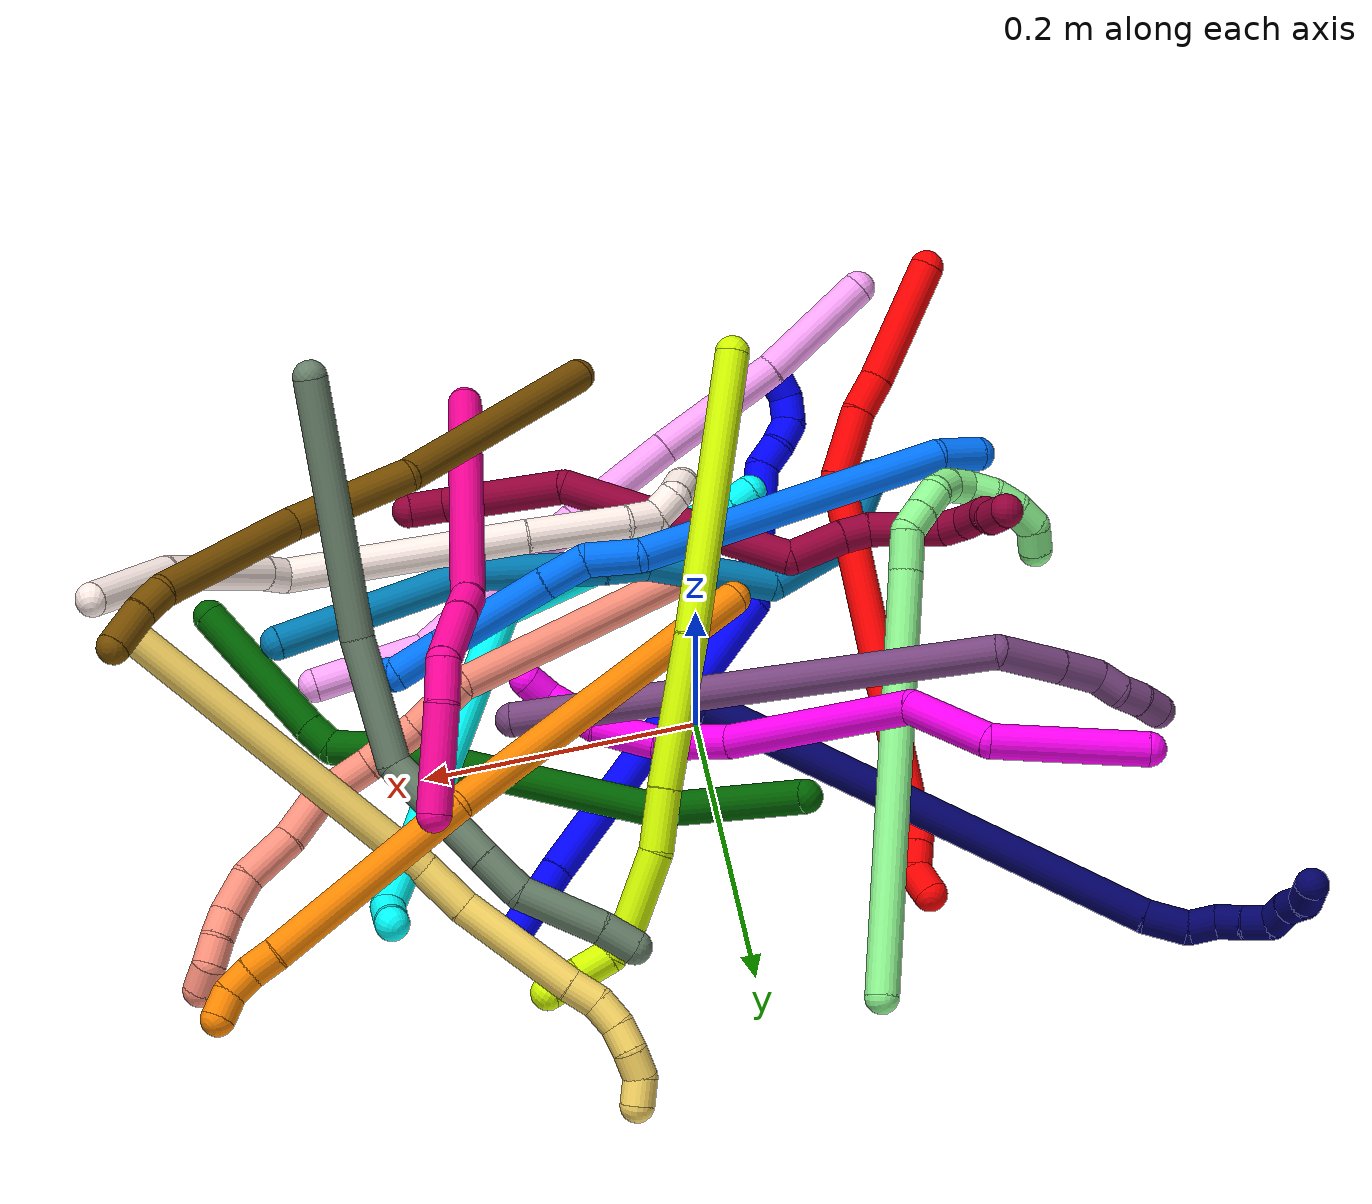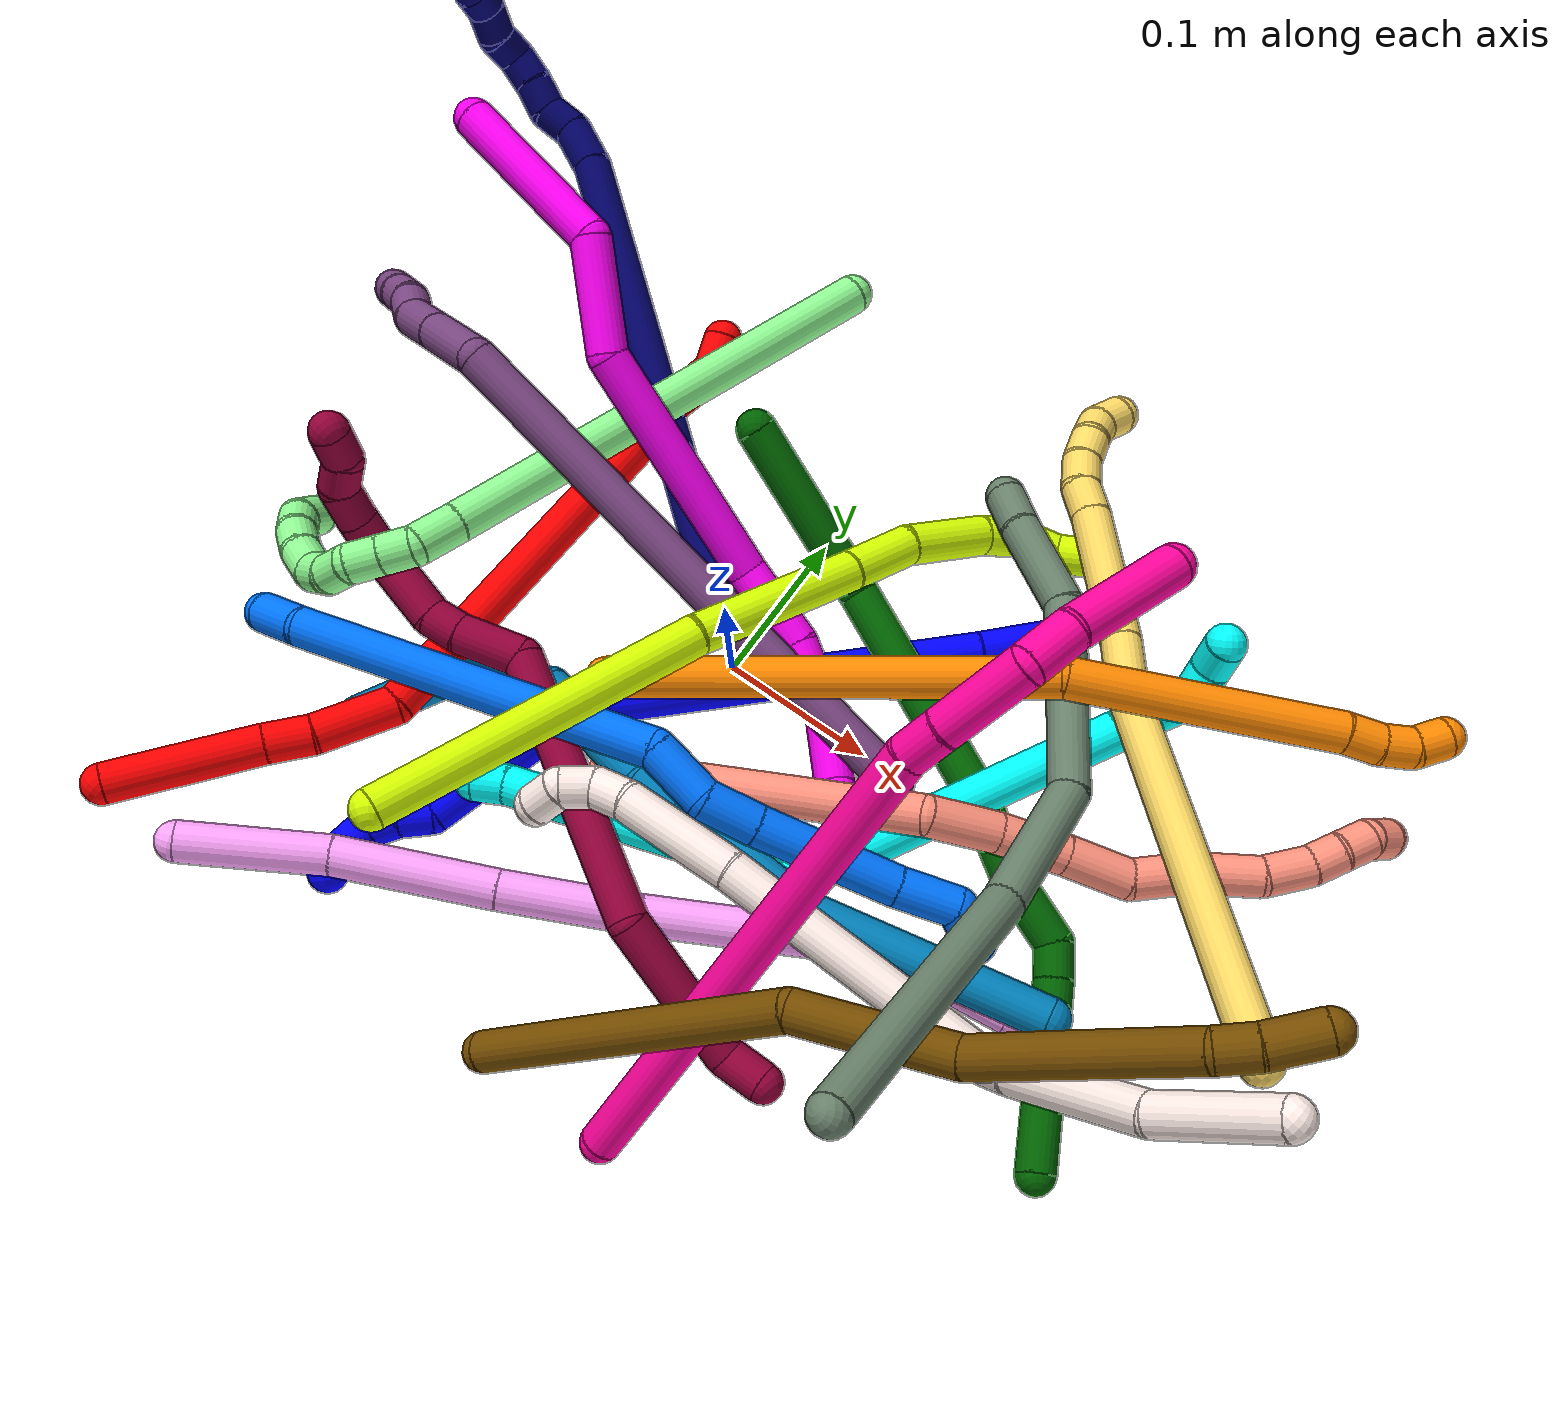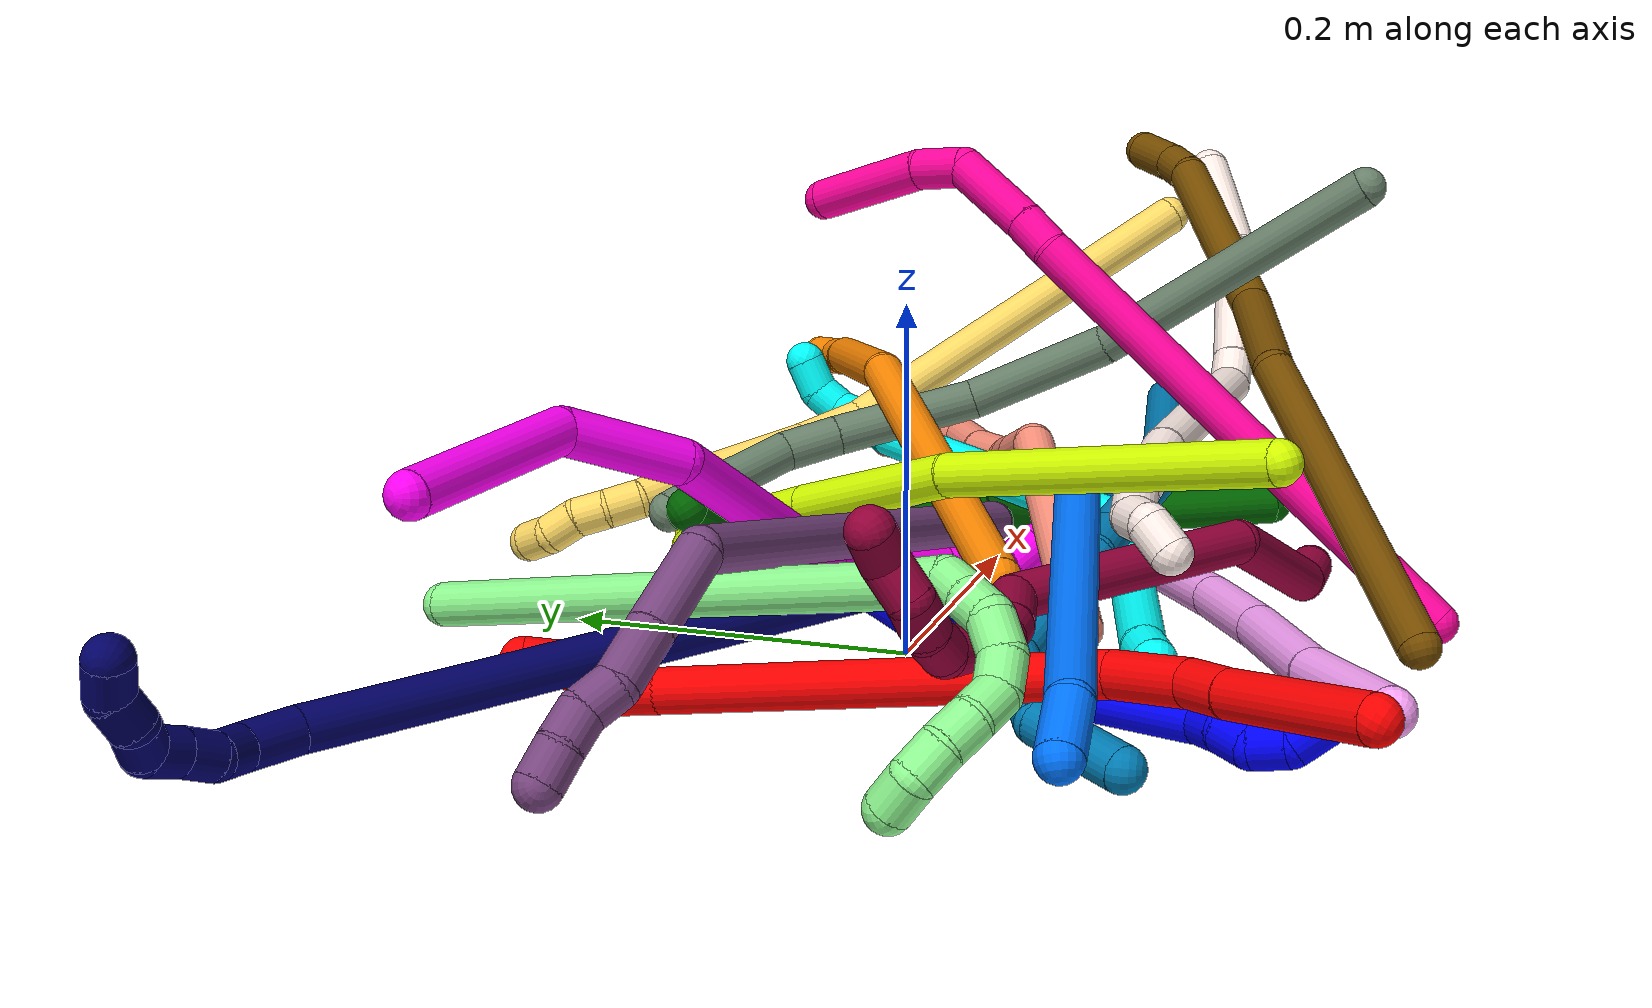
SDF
<sdf version="1.7">
 <world name="default">
  <plugin name="TubeGeneratorPlugin" filename="libtube_generator_plugin.so"/>
  <model name="photoneo_s_sensor">
   <static>1</static>
   <pose>0 0 2 1.57079 1.57079 3.14159</pose>
   <link name="link">
    <inertial><mass>0.1</mass></inertial>
    <sensor name="sensor" type="depth">
     <update_rate>30</update_rate>
     <camera>
      <horizontal_fov>1.22</horizontal_fov>
      <image><width>1920</width><height>1200</height><format>B8G8R8</format></image>
      <clip><near>0.1</near><far>4</far></clip>
      <depth_camera><output>points</output></depth_camera>
     </camera>
     <plugin name="camera_plugin" filename="libgazebo_ros_depth_camera.so">
      <baseline>0.2</baseline>
      <alwaysOn>1</alwaysOn>
      <updateRate>0.0</updateRate>
      <cameraName>camera_ir</cameraName>
      <imageTopicName>/camera/color/image_raw</imageTopicName>
      <cameraInfoTopicName>/camera/color/camera_info</cameraInfoTopicName>
      <depthImageTopicName>/camera/depth/image_raw</depthImageTopicName>
      <depthImageCameraInfoTopicName>/camera/depth/camera_info</depthImageCameraInfoTopicName>
      <pointCloudTopicName>/camera/depth/points</pointCloudTopicName>
      <frameName>fr_optical</frameName>
      <pointCloudCutoff>0.1</pointCloudCutoff>
      <pointCloudCutoffMax>2.0</pointCloudCutoffMax>
      <distortionK1>0</distortionK1>
      <distortionK2>0</distortionK2>
      <distortionK3>0</distortionK3>
      <distortionT1>0</distortionT1>
      <distortionT2>0</distortionT2>
      <CxPrime>0</CxPrime>
      <Cx>0</Cx>
      <Cy>0</Cy>
      <focalLength>0</focalLength>
      <hackBaseline>0</hackBaseline>
     </plugin>
    </sensor>
   </link>
  </model>
  <gravity>0 0 -9.8</gravity>
  <magnetic_field>6e-06 2.3e-05 -4.2e-05</magnetic_field>
  <atmosphere type="adiabatic"/>
  <physics name="default_physics" default="0" type="ode">
   <max_step_size>0.003</max_step_size>
   <real_time_factor>1</real_time_factor>
   <real_time_update_rate>1000</real_time_update_rate>
   <max_contacts>10000</max_contacts>
   <ode>
    <solver>
     <type>quick</type>
     <iters>100</iters>
     <sor>1.3</sor>
     <use_dynamic_moi_rescaling>0</use_dynamic_moi_rescaling>
    </solver>
    <constraints>
     <contact_max_correcting_vel>0</contact_max_correcting_vel>
     <contact_surface_layer>0.001</contact_surface_layer>
     <cfm>0</cfm>
     <erp>0.2</erp>
    </constraints>
   </ode>
  </physics>
  <scene><ambient>0.4 0.4 0.4 1</ambient><background>0.7 0.7 0.7 1</background><shadows>0</shadows></scene>
  <audio><device>default</device></audio>
  <spherical_coordinates>
   <surface_model>EARTH_WGS84</surface_model>
   <latitude_deg>0</latitude_deg>
   <longitude_deg>0</longitude_deg>
   <elevation>0</elevation>
   <heading_deg>0</heading_deg>
  </spherical_coordinates>
  <model name="bin">
   <static>1</static>
   <link name="bottom">
    <collision name="collision-bottom">
     <pose>0 0 -0.01 0 -0 0</pose>
     <geometry><box><size>0.8 0.6 0.02</size></box></geometry>
     <surface>
      <friction><ode><mu>100</mu><mu2>100</mu2></ode></friction>
      <contact><collide_bitmask>65535</collide_bitmask></contact>
     </surface>
    </collision>
   </link>
   <link name="west_wall">
    <collision name="collision-west_wall">
     <pose>-0.41 0 0.1 0 -0 0</pose>
     <geometry><box><size>0.02 0.6 0.2</size></box></geometry>
     <surface>
      <friction><ode><mu>100</mu><mu2>100</mu2></ode></friction>
      <contact><collide_bitmask>65535</collide_bitmask></contact>
     </surface>
    </collision>
   </link>
   <link name="east_wall">
    <collision name="collision-east_wall">
     <pose>0.41 0 0.1 0 -0 0</pose>
     <geometry><box><size>0.02 0.6 0.2</size></box></geometry>
     <surface>
      <friction><ode><mu>100</mu><mu2>100</mu2></ode></friction>
      <contact><collide_bitmask>65535</collide_bitmask></contact>
     </surface>
    </collision>
   </link>
   <link name="south_wall">
    <collision name="collision-south_wall">
     <pose>0 -0.31 0.1 0 -0 0</pose>
     <geometry><box><size>0.8 0.02 0.2</size></box></geometry>
     <surface>
      <friction><ode><mu>100</mu><mu2>100</mu2></ode></friction>
      <contact><collide_bitmask>65535</collide_bitmask></contact>
     </surface>
    </collision>
   </link>
   <link name="north_wall">
    <collision name="collision-north_wall">
     <pose>0 0.31 0.1 0 -0 0</pose>
     <geometry><box><size>0.8 0.02 0.2</size></box></geometry>
     <surface>
      <friction><ode><mu>100</mu><mu2>100</mu2></ode></friction>
      <contact><collide_bitmask>65535</collide_bitmask></contact>
     </surface>
    </collision>
   </link>
  </model>
  <model name="1">
   <static>0</static>
   <link name="1">
    <collision name="collision-cylinder-e_1_1_4">
     <pose>-0.01456 -0.024942 -0.000536 1.59228 -0.528302 -0.53923</pose>
     <geometry><cylinder><radius>0.0125</radius><length>0.057772</length></cylinder></geometry>
     <surface>
      <friction><ode><mu>1.16</mu><mu2>1.16</mu2><slip1>0</slip1><slip2>0</slip2></ode></friction>
      <contact><ode><kp>1e+06</kp><kd>1</kd><max_vel>0</max_vel><min_depth>0.001</min_depth></ode></contact>
     </surface>
    </collision>
    <visual name="visual-cylinder-e_1_1_4">
     <pose>-0.01456 -0.024942 -0.000536 1.59228 -0.528302 -0.53923</pose>
     <geometry><cylinder><radius>0.0125</radius><length>0.057772</length></cylinder></geometry>
     <material><ambient>0 0 1 1</ambient></material>
    </visual>
    <collision name="collision-cylinder-e_2_4_5">
     <pose>-0.097653 -0.155776 0.000362 1.55726 -0.574349 -0.567036</pose>
     <geometry><cylinder><radius>0.0125</radius><length>0.252285</length></cylinder></geometry>
     <surface>
      <friction><ode><mu>1.16</mu><mu2>1.16</mu2><slip1>0</slip1><slip2>0</slip2></ode></friction>
      <contact><ode><kp>1e+06</kp><kd>1</kd><max_vel>0</max_vel><min_depth>0.001</min_depth></ode></contact>
     </surface>
    </collision>
    <visual name="visual-cylinder-e_2_4_5">
     <pose>-0.097653 -0.155776 0.000362 1.55726 -0.574349 -0.567036</pose>
     <geometry><cylinder><radius>0.0125</radius><length>0.252285</length></cylinder></geometry>
     <material><ambient>0 0 1 1</ambient></material>
    </visual>
    <collision name="collision-cylinder-e_3_5_6">
     <pose>-0.183056 -0.306841 -0.023271 2.07741 -0.315677 -0.528076</pose>
     <geometry><cylinder><radius>0.0125</radius><length>0.108692</length></cylinder></geometry>
     <surface>
      <friction><ode><mu>1.16</mu><mu2>1.16</mu2><slip1>0</slip1><slip2>0</slip2></ode></friction>
      <contact><ode><kp>1e+06</kp><kd>1</kd><max_vel>0</max_vel><min_depth>0.001</min_depth></ode></contact>
     </surface>
    </collision>
    <visual name="visual-cylinder-e_3_5_6">
     <pose>-0.183056 -0.306841 -0.023271 2.07741 -0.315677 -0.528076</pose>
     <geometry><cylinder><radius>0.0125</radius><length>0.108692</length></cylinder></geometry>
     <material><ambient>0 0 1 1</ambient></material>
    </visual>
    <collision name="collision-cylinder-e_4_6_7">
     <pose>-0.204757 -0.361294 -0.047804 1.51334 -0.478987 -0.45316</pose>
     <geometry><cylinder><radius>0.0125</radius><length>0.020954</length></cylinder></geometry>
     <surface>
      <friction><ode><mu>1.16</mu><mu2>1.16</mu2><slip1>0</slip1><slip2>0</slip2></ode></friction>
      <contact><ode><kp>1e+06</kp><kd>1</kd><max_vel>0</max_vel><min_depth>0.001</min_depth></ode></contact>
     </surface>
    </collision>
    <visual name="visual-cylinder-e_4_6_7">
     <pose>-0.204757 -0.361294 -0.047804 1.51334 -0.478987 -0.45316</pose>
     <geometry><cylinder><radius>0.0125</radius><length>0.020954</length></cylinder></geometry>
     <material><ambient>0 0 1 1</ambient></material>
    </visual>
    <collision name="collision-cylinder-e_5_7_8">
     <pose>-0.215298 -0.378702 -0.049162 1.7996 -0.600357 -0.743538</pose>
     <geometry><cylinder><radius>0.0125</radius><length>0.020221</length></cylinder></geometry>
     <surface>
      <friction><ode><mu>1.16</mu><mu2>1.16</mu2><slip1>0</slip1><slip2>0</slip2></ode></friction>
      <contact><ode><kp>1e+06</kp><kd>1</kd><max_vel>0</max_vel><min_depth>0.001</min_depth></ode></contact>
     </surface>
    </collision>
    <visual name="visual-cylinder-e_5_7_8">
     <pose>-0.215298 -0.378702 -0.049162 1.7996 -0.600357 -0.743538</pose>
     <geometry><cylinder><radius>0.0125</radius><length>0.020221</length></cylinder></geometry>
     <material><ambient>0 0 1 1</ambient></material>
    </visual>
    <collision name="collision-cylinder-e_6_8_9">
     <pose>-0.221551 -0.395398 -0.056208 2.11217 -0.054146 -0.095689</pose>
     <geometry><cylinder><radius>0.0125</radius><length>0.020031</length></cylinder></geometry>
     <surface>
      <friction><ode><mu>1.16</mu><mu2>1.16</mu2><slip1>0</slip1><slip2>0</slip2></ode></friction>
      <contact><ode><kp>1e+06</kp><kd>1</kd><max_vel>0</max_vel><min_depth>0.001</min_depth></ode></contact>
     </surface>
    </collision>
    <visual name="visual-cylinder-e_6_8_9">
     <pose>-0.221551 -0.395398 -0.056208 2.11217 -0.054146 -0.095689</pose>
     <geometry><cylinder><radius>0.0125</radius><length>0.020031</length></cylinder></geometry>
     <material><ambient>0 0 1 1</ambient></material>
    </visual>
    <collision name="collision-cylinder-e_7_9_2">
     <pose>-0.217124 -0.411019 -0.066466 2.19746 0.518817 0.958709</pose>
     <geometry><cylinder><radius>0.0125</radius><length>0.020046</length></cylinder></geometry>
     <surface>
      <friction><ode><mu>1.16</mu><mu2>1.16</mu2><slip1>0</slip1><slip2>0</slip2></ode></friction>
      <contact><ode><kp>1e+06</kp><kd>1</kd><max_vel>0</max_vel><min_depth>0.001</min_depth></ode></contact>
     </surface>
    </collision>
    <visual name="visual-cylinder-e_7_9_2">
     <pose>-0.217124 -0.411019 -0.066466 2.19746 0.518817 0.958709</pose>
     <geometry><cylinder><radius>0.0125</radius><length>0.020046</length></cylinder></geometry>
     <material><ambient>0 0 1 1</ambient></material>
    </visual>
    <collision name="collision-sphere-2">
     <pose>-0.212154 -0.418069 -0.071571 0 -0 0</pose>
     <geometry><sphere><radius>0.0125</radius></sphere></geometry>
     <surface>
      <friction><ode><mu>1.16</mu><mu2>1.16</mu2><slip1>0</slip1><slip2>0</slip2></ode></friction>
      <contact><ode><kp>1e+06</kp><kd>1</kd><max_vel>0</max_vel><min_depth>0.001</min_depth></ode></contact>
     </surface>
    </collision>
    <visual name="visual-sphere-2">
     <pose>-0.212154 -0.418069 -0.071571 0 -0 0</pose>
     <geometry><sphere><radius>0.0125</radius></sphere></geometry>
     <material><ambient>0 0 1 1</ambient></material>
    </visual>
    <collision name="collision-sphere-9">
     <pose>-0.222093 -0.403969 -0.061362 0 -0 0</pose>
     <geometry><sphere><radius>0.0125</radius></sphere></geometry>
     <surface>
      <friction><ode><mu>1.16</mu><mu2>1.16</mu2><slip1>0</slip1><slip2>0</slip2></ode></friction>
      <contact><ode><kp>1e+06</kp><kd>1</kd><max_vel>0</max_vel><min_depth>0.001</min_depth></ode></contact>
     </surface>
    </collision>
    <visual name="visual-sphere-9">
     <pose>-0.222093 -0.403969 -0.061362 0 -0 0</pose>
     <geometry><sphere><radius>0.0125</radius></sphere></geometry>
     <material><ambient>0 0 1 1</ambient></material>
    </visual>
    <collision name="collision-sphere-4">
     <pose>-0.029121 -0.049884 -0.001072 0 -0 0</pose>
     <geometry><sphere><radius>0.0125</radius></sphere></geometry>
     <surface>
      <friction><ode><mu>1.16</mu><mu2>1.16</mu2><slip1>0</slip1><slip2>0</slip2></ode></friction>
      <contact><ode><kp>1e+06</kp><kd>1</kd><max_vel>0</max_vel><min_depth>0.001</min_depth></ode></contact>
     </surface>
    </collision>
    <visual name="visual-sphere-4">
     <pose>-0.029121 -0.049884 -0.001072 0 -0 0</pose>
     <geometry><sphere><radius>0.0125</radius></sphere></geometry>
     <material><ambient>0 0 1 1</ambient></material>
    </visual>
    <collision name="collision-sphere-1">
     <geometry><sphere><radius>0.0125</radius></sphere></geometry>
     <surface>
      <friction><ode><mu>1.16</mu><mu2>1.16</mu2><slip1>0</slip1><slip2>0</slip2></ode></friction>
      <contact><ode><kp>1e+06</kp><kd>1</kd><max_vel>0</max_vel><min_depth>0.001</min_depth></ode></contact>
     </surface>
    </collision>
    <visual name="visual-sphere-1">
     <geometry><sphere><radius>0.0125</radius></sphere></geometry>
     <material><ambient>0 0 1 1</ambient></material>
    </visual>
    <collision name="collision-sphere-8">
     <pose>-0.221009 -0.386827 -0.051055 0 -0 0</pose>
     <geometry><sphere><radius>0.0125</radius></sphere></geometry>
     <surface>
      <friction><ode><mu>1.16</mu><mu2>1.16</mu2><slip1>0</slip1><slip2>0</slip2></ode></friction>
      <contact><ode><kp>1e+06</kp><kd>1</kd><max_vel>0</max_vel><min_depth>0.001</min_depth></ode></contact>
     </surface>
    </collision>
    <visual name="visual-sphere-8">
     <pose>-0.221009 -0.386827 -0.051055 0 -0 0</pose>
     <geometry><sphere><radius>0.0125</radius></sphere></geometry>
     <material><ambient>0 0 1 1</ambient></material>
    </visual>
    <collision name="collision-sphere-5">
     <pose>-0.166184 -0.261669 0.001795 0 -0 0</pose>
     <geometry><sphere><radius>0.0125</radius></sphere></geometry>
     <surface>
      <friction><ode><mu>1.16</mu><mu2>1.16</mu2><slip1>0</slip1><slip2>0</slip2></ode></friction>
      <contact><ode><kp>1e+06</kp><kd>1</kd><max_vel>0</max_vel><min_depth>0.001</min_depth></ode></contact>
     </surface>
    </collision>
    <visual name="visual-sphere-5">
     <pose>-0.166184 -0.261669 0.001795 0 -0 0</pose>
     <geometry><sphere><radius>0.0125</radius></sphere></geometry>
     <material><ambient>0 0 1 1</ambient></material>
    </visual>
    <collision name="collision-sphere-6">
     <pose>-0.199929 -0.352012 -0.048338 0 -0 0</pose>
     <geometry><sphere><radius>0.0125</radius></sphere></geometry>
     <surface>
      <friction><ode><mu>1.16</mu><mu2>1.16</mu2><slip1>0</slip1><slip2>0</slip2></ode></friction>
      <contact><ode><kp>1e+06</kp><kd>1</kd><max_vel>0</max_vel><min_depth>0.001</min_depth></ode></contact>
     </surface>
    </collision>
    <visual name="visual-sphere-6">
     <pose>-0.199929 -0.352012 -0.048338 0 -0 0</pose>
     <geometry><sphere><radius>0.0125</radius></sphere></geometry>
     <material><ambient>0 0 1 1</ambient></material>
    </visual>
    <collision name="collision-sphere-7">
     <pose>-0.209586 -0.370577 -0.04727 0 -0 0</pose>
     <geometry><sphere><radius>0.0125</radius></sphere></geometry>
     <surface>
      <friction><ode><mu>1.16</mu><mu2>1.16</mu2><slip1>0</slip1><slip2>0</slip2></ode></friction>
      <contact><ode><kp>1e+06</kp><kd>1</kd><max_vel>0</max_vel><min_depth>0.001</min_depth></ode></contact>
     </surface>
    </collision>
    <visual name="visual-sphere-7">
     <pose>-0.209586 -0.370577 -0.04727 0 -0 0</pose>
     <geometry><sphere><radius>0.0125</radius></sphere></geometry>
     <material><ambient>0 0 1 1</ambient></material>
    </visual>
    <inertial>
     <pose>-0.125617 -0.210959 -0.013846 0 -0 0</pose>
     <mass>0.5</mass>
     <inertia>
      <ixx>0.000377</ixx>
      <ixy>0</ixy>
      <ixz>0</ixz>
      <iyy>-0.000321</iyy>
      <iyz>0</iyz>
      <izz>0.002016</izz>
     </inertia>
    </inertial>
   </link>
   <pose>0.162557 0.135919 0.011476 -0.957283 -0.911747 0.267832</pose>
  </model>
  <model name="2">
   <static>0</static>
   <link name="2">
    <collision name="collision-cylinder-e_1_1_4">
     <pose>-0.012761 0.027222 -0.035474 -2.48706 -0.27799 0.781788</pose>
     <geometry><cylinder><radius>0.0125</radius><length>0.093001</length></cylinder></geometry>
     <surface>
      <friction><ode><mu>1.16</mu><mu2>1.16</mu2><slip1>0</slip1><slip2>0</slip2></ode></friction>
      <contact><ode><kp>1e+06</kp><kd>1</kd><max_vel>0</max_vel><min_depth>0.001</min_depth></ode></contact>
     </surface>
    </collision>
    <visual name="visual-cylinder-e_1_1_4">
     <pose>-0.012761 0.027222 -0.035474 -2.48706 -0.27799 0.781788</pose>
     <geometry><cylinder><radius>0.0125</radius><length>0.093001</length></cylinder></geometry>
     <material><ambient>1 0 0 1</ambient></material>
    </visual>
    <collision name="collision-cylinder-e_2_4_5">
     <pose>-0.030514 0.062322 -0.081615 -2.50552 -0.36005 1.01001</pose>
     <geometry><cylinder><radius>0.0125</radius><length>0.028337</length></cylinder></geometry>
     <surface>
      <friction><ode><mu>1.16</mu><mu2>1.16</mu2><slip1>0</slip1><slip2>0</slip2></ode></friction>
      <contact><ode><kp>1e+06</kp><kd>1</kd><max_vel>0</max_vel><min_depth>0.001</min_depth></ode></contact>
     </surface>
    </collision>
    <visual name="visual-cylinder-e_2_4_5">
     <pose>-0.030514 0.062322 -0.081615 -2.50552 -0.36005 1.01001</pose>
     <geometry><cylinder><radius>0.0125</radius><length>0.028337</length></cylinder></geometry>
     <material><ambient>1 0 0 1</ambient></material>
    </visual>
    <collision name="collision-cylinder-e_3_5_6">
     <pose>-0.039711 0.084904 -0.112678 -2.51692 -0.165704 0.503428</pose>
     <geometry><cylinder><radius>0.0125</radius><length>0.050988</length></cylinder></geometry>
     <surface>
      <friction><ode><mu>1.16</mu><mu2>1.16</mu2><slip1>0</slip1><slip2>0</slip2></ode></friction>
      <contact><ode><kp>1e+06</kp><kd>1</kd><max_vel>0</max_vel><min_depth>0.001</min_depth></ode></contact>
     </surface>
    </collision>
    <visual name="visual-cylinder-e_3_5_6">
     <pose>-0.039711 0.084904 -0.112678 -2.51692 -0.165704 0.503428</pose>
     <geometry><cylinder><radius>0.0125</radius><length>0.050988</length></cylinder></geometry>
     <material><ambient>1 0 0 1</ambient></material>
    </visual>
    <collision name="collision-cylinder-e_4_6_7">
     <pose>-0.006024 0.153257 -0.236125 -2.66161 0.315276 -1.15215</pose>
     <geometry><cylinder><radius>0.0125</radius><length>0.244403</length></cylinder></geometry>
     <surface>
      <friction><ode><mu>1.16</mu><mu2>1.16</mu2><slip1>0</slip1><slip2>0</slip2></ode></friction>
      <contact><ode><kp>1e+06</kp><kd>1</kd><max_vel>0</max_vel><min_depth>0.001</min_depth></ode></contact>
     </surface>
    </collision>
    <visual name="visual-cylinder-e_4_6_7">
     <pose>-0.006024 0.153257 -0.236125 -2.66161 0.315276 -1.15215</pose>
     <geometry><cylinder><radius>0.0125</radius><length>0.244403</length></cylinder></geometry>
     <material><ambient>1 0 0 1</ambient></material>
    </visual>
    <collision name="collision-cylinder-e_5_7_8">
     <pose>0.036133 0.21085 -0.348148 -2.72737 0.410359 -1.56115</pose>
     <geometry><cylinder><radius>0.0125</radius><length>0.021379</length></cylinder></geometry>
     <surface>
      <friction><ode><mu>1.16</mu><mu2>1.16</mu2><slip1>0</slip1><slip2>0</slip2></ode></friction>
      <contact><ode><kp>1e+06</kp><kd>1</kd><max_vel>0</max_vel><min_depth>0.001</min_depth></ode></contact>
     </surface>
    </collision>
    <visual name="visual-cylinder-e_5_7_8">
     <pose>0.036133 0.21085 -0.348148 -2.72737 0.410359 -1.56115</pose>
     <geometry><cylinder><radius>0.0125</radius><length>0.021379</length></cylinder></geometry>
     <material><ambient>1 0 0 1</ambient></material>
    </visual>
    <collision name="collision-cylinder-e_6_8_9">
     <pose>0.03995 0.216817 -0.366912 -2.93795 -0.044724 0.431002</pose>
     <geometry><cylinder><radius>0.0125</radius><length>0.020014</length></cylinder></geometry>
     <surface>
      <friction><ode><mu>1.16</mu><mu2>1.16</mu2><slip1>0</slip1><slip2>0</slip2></ode></friction>
      <contact><ode><kp>1e+06</kp><kd>1</kd><max_vel>0</max_vel><min_depth>0.001</min_depth></ode></contact>
     </surface>
    </collision>
    <visual name="visual-cylinder-e_6_8_9">
     <pose>0.03995 0.216817 -0.366912 -2.93795 -0.044724 0.431002</pose>
     <geometry><cylinder><radius>0.0125</radius><length>0.020014</length></cylinder></geometry>
     <material><ambient>1 0 0 1</ambient></material>
    </visual>
    <collision name="collision-cylinder-e_7_9_10">
     <pose>0.039104 0.220993 -0.386509 -2.92538 -0.039623 0.361153</pose>
     <geometry><cylinder><radius>0.0125</radius><length>0.020097</length></cylinder></geometry>
     <surface>
      <friction><ode><mu>1.16</mu><mu2>1.16</mu2><slip1>0</slip1><slip2>0</slip2></ode></friction>
      <contact><ode><kp>1e+06</kp><kd>1</kd><max_vel>0</max_vel><min_depth>0.001</min_depth></ode></contact>
     </surface>
    </collision>
    <visual name="visual-cylinder-e_7_9_10">
     <pose>0.039104 0.220993 -0.386509 -2.92538 -0.039623 0.361153</pose>
     <geometry><cylinder><radius>0.0125</radius><length>0.020097</length></cylinder></geometry>
     <material><ambient>1 0 0 1</ambient></material>
    </visual>
    <collision name="collision-cylinder-e_8_10_2">
     <pose>0.044457 0.224028 -0.405522 -3.04619 0.556384 -2.81036</pose>
     <geometry><cylinder><radius>0.0125</radius><length>0.02178</length></cylinder></geometry>
     <surface>
      <friction><ode><mu>1.16</mu><mu2>1.16</mu2><slip1>0</slip1><slip2>0</slip2></ode></friction>
      <contact><ode><kp>1e+06</kp><kd>1</kd><max_vel>0</max_vel><min_depth>0.001</min_depth></ode></contact>
     </surface>
    </collision>
    <visual name="visual-cylinder-e_8_10_2">
     <pose>0.044457 0.224028 -0.405522 -3.04619 0.556384 -2.81036</pose>
     <geometry><cylinder><radius>0.0125</radius><length>0.02178</length></cylinder></geometry>
     <material><ambient>1 0 0 1</ambient></material>
    </visual>
    <collision name="collision-sphere-2">
     <pose>0.050209 0.224909 -0.414727 0 -0 0</pose>
     <geometry><sphere><radius>0.0125</radius></sphere></geometry>
     <surface>
      <friction><ode><mu>1.16</mu><mu2>1.16</mu2><slip1>0</slip1><slip2>0</slip2></ode></friction>
      <contact><ode><kp>1e+06</kp><kd>1</kd><max_vel>0</max_vel><min_depth>0.001</min_depth></ode></contact>
     </surface>
    </collision>
    <visual name="visual-sphere-2">
     <pose>0.050209 0.224909 -0.414727 0 -0 0</pose>
     <geometry><sphere><radius>0.0125</radius></sphere></geometry>
     <material><ambient>1 0 0 1</ambient></material>
    </visual>
    <collision name="collision-sphere-10">
     <pose>0.038706 0.223147 -0.396316 0 -0 0</pose>
     <geometry><sphere><radius>0.0125</radius></sphere></geometry>
     <surface>
      <friction><ode><mu>1.16</mu><mu2>1.16</mu2><slip1>0</slip1><slip2>0</slip2></ode></friction>
      <contact><ode><kp>1e+06</kp><kd>1</kd><max_vel>0</max_vel><min_depth>0.001</min_depth></ode></contact>
     </surface>
    </collision>
    <visual name="visual-sphere-10">
     <pose>0.038706 0.223147 -0.396316 0 -0 0</pose>
     <geometry><sphere><radius>0.0125</radius></sphere></geometry>
     <material><ambient>1 0 0 1</ambient></material>
    </visual>
    <collision name="collision-sphere-9">
     <pose>0.039502 0.218839 -0.376702 0 -0 0</pose>
     <geometry><sphere><radius>0.0125</radius></sphere></geometry>
     <surface>
      <friction><ode><mu>1.16</mu><mu2>1.16</mu2><slip1>0</slip1><slip2>0</slip2></ode></friction>
      <contact><ode><kp>1e+06</kp><kd>1</kd><max_vel>0</max_vel><min_depth>0.001</min_depth></ode></contact>
     </surface>
    </collision>
    <visual name="visual-sphere-9">
     <pose>0.039502 0.218839 -0.376702 0 -0 0</pose>
     <geometry><sphere><radius>0.0125</radius></sphere></geometry>
     <material><ambient>1 0 0 1</ambient></material>
    </visual>
    <collision name="collision-sphere-4">
     <pose>-0.025522 0.054444 -0.070948 0 -0 0</pose>
     <geometry><sphere><radius>0.0125</radius></sphere></geometry>
     <surface>
      <friction><ode><mu>1.16</mu><mu2>1.16</mu2><slip1>0</slip1><slip2>0</slip2></ode></friction>
      <contact><ode><kp>1e+06</kp><kd>1</kd><max_vel>0</max_vel><min_depth>0.001</min_depth></ode></contact>
     </surface>
    </collision>
    <visual name="visual-sphere-4">
     <pose>-0.025522 0.054444 -0.070948 0 -0 0</pose>
     <geometry><sphere><radius>0.0125</radius></sphere></geometry>
     <material><ambient>1 0 0 1</ambient></material>
    </visual>
    <collision name="collision-sphere-1">
     <geometry><sphere><radius>0.0125</radius></sphere></geometry>
     <surface>
      <friction><ode><mu>1.16</mu><mu2>1.16</mu2><slip1>0</slip1><slip2>0</slip2></ode></friction>
      <contact><ode><kp>1e+06</kp><kd>1</kd><max_vel>0</max_vel><min_depth>0.001</min_depth></ode></contact>
     </surface>
    </collision>
    <visual name="visual-sphere-1">
     <geometry><sphere><radius>0.0125</radius></sphere></geometry>
     <material><ambient>1 0 0 1</ambient></material>
    </visual>
    <collision name="collision-sphere-8">
     <pose>0.040397 0.214795 -0.357121 0 -0 0</pose>
     <geometry><sphere><radius>0.0125</radius></sphere></geometry>
     <surface>
      <friction><ode><mu>1.16</mu><mu2>1.16</mu2><slip1>0</slip1><slip2>0</slip2></ode></friction>
      <contact><ode><kp>1e+06</kp><kd>1</kd><max_vel>0</max_vel><min_depth>0.001</min_depth></ode></contact>
     </surface>
    </collision>
    <visual name="visual-sphere-8">
     <pose>0.040397 0.214795 -0.357121 0 -0 0</pose>
     <geometry><sphere><radius>0.0125</radius></sphere></geometry>
     <material><ambient>1 0 0 1</ambient></material>
    </visual>
    <collision name="collision-sphere-5">
     <pose>-0.035506 0.070199 -0.092282 0 -0 0</pose>
     <geometry><sphere><radius>0.0125</radius></sphere></geometry>
     <surface>
      <friction><ode><mu>1.16</mu><mu2>1.16</mu2><slip1>0</slip1><slip2>0</slip2></ode></friction>
      <contact><ode><kp>1e+06</kp><kd>1</kd><max_vel>0</max_vel><min_depth>0.001</min_depth></ode></contact>
     </surface>
    </collision>
    <visual name="visual-sphere-5">
     <pose>-0.035506 0.070199 -0.092282 0 -0 0</pose>
     <geometry><sphere><radius>0.0125</radius></sphere></geometry>
     <material><ambient>1 0 0 1</ambient></material>
    </visual>
    <collision name="collision-sphere-6">
     <pose>-0.043916 0.09961 -0.133075 0 -0 0</pose>
     <geometry><sphere><radius>0.0125</radius></sphere></geometry>
     <surface>
      <friction><ode><mu>1.16</mu><mu2>1.16</mu2><slip1>0</slip1><slip2>0</slip2></ode></friction>
      <contact><ode><kp>1e+06</kp><kd>1</kd><max_vel>0</max_vel><min_depth>0.001</min_depth></ode></contact>
     </surface>
    </collision>
    <visual name="visual-sphere-6">
     <pose>-0.043916 0.09961 -0.133075 0 -0 0</pose>
     <geometry><sphere><radius>0.0125</radius></sphere></geometry>
     <material><ambient>1 0 0 1</ambient></material>
    </visual>
    <collision name="collision-sphere-7">
     <pose>0.031868 0.206905 -0.339175 0 -0 0</pose>
     <geometry><sphere><radius>0.0125</radius></sphere></geometry>
     <surface>
      <friction><ode><mu>1.16</mu><mu2>1.16</mu2><slip1>0</slip1><slip2>0</slip2></ode></friction>
      <contact><ode><kp>1e+06</kp><kd>1</kd><max_vel>0</max_vel><min_depth>0.001</min_depth></ode></contact>
     </surface>
    </collision>
    <visual name="visual-sphere-7">
     <pose>0.031868 0.206905 -0.339175 0 -0 0</pose>
     <geometry><sphere><radius>0.0125</radius></sphere></geometry>
     <material><ambient>1 0 0 1</ambient></material>
    </visual>
    <inertial>
     <pose>-0.004445 0.128502 -0.200907 0 -0 0</pose>
     <mass>0.5</mass>
     <inertia>
      <ixx>-0.000469</ixx>
      <ixy>0</ixy>
      <ixz>0</ixz>
      <iyy>-0.001315</iyy>
      <iyz>0</iyz>
      <izz>-0.000982</izz>
     </inertia>
    </inertial>
   </link>
   <pose>-0.235277 -0.2874 0.076403 -1.97616 0.255977 2.84321</pose>
  </model>
  <model name="3">
   <static>0</static>
   <link name="3">
    <collision name="collision-cylinder-e_1_1_4">
     <pose>-0.000626 0.010036 -0.000285 -1.59923 -0.062261 0.064056</pose>
     <geometry><cylinder><radius>0.0125</radius><length>0.020119</length></cylinder></geometry>
     <surface>
      <friction><ode><mu>1.16</mu><mu2>1.16</mu2><slip1>0</slip1><slip2>0</slip2></ode></friction>
      <contact><ode><kp>1e+06</kp><kd>1</kd><max_vel>0</max_vel><min_depth>0.001</min_depth></ode></contact>
     </surface>
    </collision>
    <visual name="visual-cylinder-e_1_1_4">
     <pose>-0.000626 0.010036 -0.000285 -1.59923 -0.062261 0.064056</pose>
     <geometry><cylinder><radius>0.0125</radius><length>0.020119</length></cylinder></geometry>
     <material><ambient>0.003922 1 0.996078 1</ambient></material>
    </visual>
    <collision name="collision-cylinder-e_2_4_5">
     <pose>0.004504 0.111106 -0.017144 -1.75088 0.062124 -0.074445</pose>
     <geometry><cylinder><radius>0.0125</radius><length>0.185419</length></cylinder></geometry>
     <surface>
      <friction><ode><mu>1.16</mu><mu2>1.16</mu2><slip1>0</slip1><slip2>0</slip2></ode></friction>
      <contact><ode><kp>1e+06</kp><kd>1</kd><max_vel>0</max_vel><min_depth>0.001</min_depth></ode></contact>
     </surface>
    </collision>
    <visual name="visual-cylinder-e_2_4_5">
     <pose>0.004504 0.111106 -0.017144 -1.75088 0.062124 -0.074445</pose>
     <geometry><cylinder><radius>0.0125</radius><length>0.185419</length></cylinder></geometry>
     <material><ambient>0.003922 1 0.996078 1</ambient></material>
    </visual>
    <collision name="collision-cylinder-e_3_5_6">
     <pose>-0.020717 0.287971 0.012728 -1.07479 -0.307351 0.184083</pose>
     <geometry><cylinder><radius>0.0125</radius><length>0.204778</length></cylinder></geometry>
     <surface>
      <friction><ode><mu>1.16</mu><mu2>1.16</mu2><slip1>0</slip1><slip2>0</slip2></ode></friction>
      <contact><ode><kp>1e+06</kp><kd>1</kd><max_vel>0</max_vel><min_depth>0.001</min_depth></ode></contact>
     </surface>
    </collision>
    <visual name="visual-cylinder-e_3_5_6">
     <pose>-0.020717 0.287971 0.012728 -1.07479 -0.307351 0.184083</pose>
     <geometry><cylinder><radius>0.0125</radius><length>0.204778</length></cylinder></geometry>
     <material><ambient>0.003922 1 0.996078 1</ambient></material>
    </visual>
    <collision name="collision-cylinder-e_4_6_7">
     <pose>-0.052447 0.382558 0.064664 -1.01077 -0.072798 0.040293</pose>
     <geometry><cylinder><radius>0.0125</radius><length>0.020726</length></cylinder></geometry>
     <surface>
      <friction><ode><mu>1.16</mu><mu2>1.16</mu2><slip1>0</slip1><slip2>0</slip2></ode></friction>
      <contact><ode><kp>1e+06</kp><kd>1</kd><max_vel>0</max_vel><min_depth>0.001</min_depth></ode></contact>
     </surface>
    </collision>
    <visual name="visual-cylinder-e_4_6_7">
     <pose>-0.052447 0.382558 0.064664 -1.01077 -0.072798 0.040293</pose>
     <geometry><cylinder><radius>0.0125</radius><length>0.020726</length></cylinder></geometry>
     <material><ambient>0.003922 1 0.996078 1</ambient></material>
    </visual>
    <collision name="collision-cylinder-e_5_7_8">
     <pose>-0.057039 0.402943 0.07602 -1.10358 -0.286571 0.177157</pose>
     <geometry><cylinder><radius>0.0125</radius><length>0.027157</length></cylinder></geometry>
     <surface>
      <friction><ode><mu>1.16</mu><mu2>1.16</mu2><slip1>0</slip1><slip2>0</slip2></ode></friction>
      <contact><ode><kp>1e+06</kp><kd>1</kd><max_vel>0</max_vel><min_depth>0.001</min_depth></ode></contact>
     </surface>
    </collision>
    <visual name="visual-cylinder-e_5_7_8">
     <pose>-0.057039 0.402943 0.07602 -1.10358 -0.286571 0.177157</pose>
     <geometry><cylinder><radius>0.0125</radius><length>0.027157</length></cylinder></geometry>
     <material><ambient>0.003922 1 0.996078 1</ambient></material>
    </visual>
    <collision name="collision-cylinder-e_6_8_9">
     <pose>-0.059935 0.418901 0.09092 -0.446883 0.09371 -0.021309</pose>
     <geometry><cylinder><radius>0.0125</radius><length>0.020122</length></cylinder></geometry>
     <surface>
      <friction><ode><mu>1.16</mu><mu2>1.16</mu2><slip1>0</slip1><slip2>0</slip2></ode></friction>
      <contact><ode><kp>1e+06</kp><kd>1</kd><max_vel>0</max_vel><min_depth>0.001</min_depth></ode></contact>
     </surface>
    </collision>
    <visual name="visual-cylinder-e_6_8_9">
     <pose>-0.059935 0.418901 0.09092 -0.446883 0.09371 -0.021309</pose>
     <geometry><cylinder><radius>0.0125</radius><length>0.020122</length></cylinder></geometry>
     <material><ambient>0.003922 1 0.996078 1</ambient></material>
    </visual>
    <collision name="collision-cylinder-e_7_9_2">
     <pose>-0.052969 0.426727 0.108257 -0.398549 0.589344 -0.122437</pose>
     <geometry><cylinder><radius>0.0125</radius><length>0.021679</length></cylinder></geometry>
     <surface>
      <friction><ode><mu>1.16</mu><mu2>1.16</mu2><slip1>0</slip1><slip2>0</slip2></ode></friction>
      <contact><ode><kp>1e+06</kp><kd>1</kd><max_vel>0</max_vel><min_depth>0.001</min_depth></ode></contact>
     </surface>
    </collision>
    <visual name="visual-cylinder-e_7_9_2">
     <pose>-0.052969 0.426727 0.108257 -0.398549 0.589344 -0.122437</pose>
     <geometry><cylinder><radius>0.0125</radius><length>0.021679</length></cylinder></geometry>
     <material><ambient>0.003922 1 0.996078 1</ambient></material>
    </visual>
    <collision name="collision-sphere-2">
     <pose>-0.046944 0.430224 0.116562 0 -0 0</pose>
     <geometry><sphere><radius>0.0125</radius></sphere></geometry>
     <surface>
      <friction><ode><mu>1.16</mu><mu2>1.16</mu2><slip1>0</slip1><slip2>0</slip2></ode></friction>
      <contact><ode><kp>1e+06</kp><kd>1</kd><max_vel>0</max_vel><min_depth>0.001</min_depth></ode></contact>
     </surface>
    </collision>
    <visual name="visual-sphere-2">
     <pose>-0.046944 0.430224 0.116562 0 -0 0</pose>
     <geometry><sphere><radius>0.0125</radius></sphere></geometry>
     <material><ambient>0.003922 1 0.996078 1</ambient></material>
    </visual>
    <collision name="collision-sphere-9">
     <pose>-0.058994 0.42323 0.099953 0 -0 0</pose>
     <geometry><sphere><radius>0.0125</radius></sphere></geometry>
     <surface>
      <friction><ode><mu>1.16</mu><mu2>1.16</mu2><slip1>0</slip1><slip2>0</slip2></ode></friction>
      <contact><ode><kp>1e+06</kp><kd>1</kd><max_vel>0</max_vel><min_depth>0.001</min_depth></ode></contact>
     </surface>
    </collision>
    <visual name="visual-sphere-9">
     <pose>-0.058994 0.42323 0.099953 0 -0 0</pose>
     <geometry><sphere><radius>0.0125</radius></sphere></geometry>
     <material><ambient>0.003922 1 0.996078 1</ambient></material>
    </visual>
    <collision name="collision-sphere-4">
     <pose>-0.001252 0.020072 -0.000571 0 -0 0</pose>
     <geometry><sphere><radius>0.0125</radius></sphere></geometry>
     <surface>
      <friction><ode><mu>1.16</mu><mu2>1.16</mu2><slip1>0</slip1><slip2>0</slip2></ode></friction>
      <contact><ode><kp>1e+06</kp><kd>1</kd><max_vel>0</max_vel><min_depth>0.001</min_depth></ode></contact>
     </surface>
    </collision>
    <visual name="visual-sphere-4">
     <pose>-0.001252 0.020072 -0.000571 0 -0 0</pose>
     <geometry><sphere><radius>0.0125</radius></sphere></geometry>
     <material><ambient>0.003922 1 0.996078 1</ambient></material>
    </visual>
    <collision name="collision-sphere-1">
     <geometry><sphere><radius>0.0125</radius></sphere></geometry>
     <surface>
      <friction><ode><mu>1.16</mu><mu2>1.16</mu2><slip1>0</slip1><slip2>0</slip2></ode></friction>
      <contact><ode><kp>1e+06</kp><kd>1</kd><max_vel>0</max_vel><min_depth>0.001</min_depth></ode></contact>
     </surface>
    </collision>
    <visual name="visual-sphere-1">
     <geometry><sphere><radius>0.0125</radius></sphere></geometry>
     <material><ambient>0.003922 1 0.996078 1</ambient></material>
    </visual>
    <collision name="collision-sphere-8">
     <pose>-0.060877 0.414572 0.081887 0 -0 0</pose>
     <geometry><sphere><radius>0.0125</radius></sphere></geometry>
     <surface>
      <friction><ode><mu>1.16</mu><mu2>1.16</mu2><slip1>0</slip1><slip2>0</slip2></ode></friction>
      <contact><ode><kp>1e+06</kp><kd>1</kd><max_vel>0</max_vel><min_depth>0.001</min_depth></ode></contact>
     </surface>
    </collision>
    <visual name="visual-sphere-8">
     <pose>-0.060877 0.414572 0.081887 0 -0 0</pose>
     <geometry><sphere><radius>0.0125</radius></sphere></geometry>
     <material><ambient>0.003922 1 0.996078 1</ambient></material>
    </visual>
    <collision name="collision-sphere-5">
     <pose>0.01026 0.20214 -0.033717 0 -0 0</pose>
     <geometry><sphere><radius>0.0125</radius></sphere></geometry>
     <surface>
      <friction><ode><mu>1.16</mu><mu2>1.16</mu2><slip1>0</slip1><slip2>0</slip2></ode></friction>
      <contact><ode><kp>1e+06</kp><kd>1</kd><max_vel>0</max_vel><min_depth>0.001</min_depth></ode></contact>
     </surface>
    </collision>
    <visual name="visual-sphere-5">
     <pose>0.01026 0.20214 -0.033717 0 -0 0</pose>
     <geometry><sphere><radius>0.0125</radius></sphere></geometry>
     <material><ambient>0.003922 1 0.996078 1</ambient></material>
    </visual>
    <collision name="collision-sphere-6">
     <pose>-0.051693 0.373801 0.059173 0 -0 0</pose>
     <geometry><sphere><radius>0.0125</radius></sphere></geometry>
     <surface>
      <friction><ode><mu>1.16</mu><mu2>1.16</mu2><slip1>0</slip1><slip2>0</slip2></ode></friction>
      <contact><ode><kp>1e+06</kp><kd>1</kd><max_vel>0</max_vel><min_depth>0.001</min_depth></ode></contact>
     </surface>
    </collision>
    <visual name="visual-sphere-6">
     <pose>-0.051693 0.373801 0.059173 0 -0 0</pose>
     <geometry><sphere><radius>0.0125</radius></sphere></geometry>
     <material><ambient>0.003922 1 0.996078 1</ambient></material>
    </visual>
    <collision name="collision-sphere-7">
     <pose>-0.0532 0.391315 0.070154 0 -0 0</pose>
     <geometry><sphere><radius>0.0125</radius></sphere></geometry>
     <surface>
      <friction><ode><mu>1.16</mu><mu2>1.16</mu2><slip1>0</slip1><slip2>0</slip2></ode></friction>
      <contact><ode><kp>1e+06</kp><kd>1</kd><max_vel>0</max_vel><min_depth>0.001</min_depth></ode></contact>
     </surface>
    </collision>
    <visual name="visual-sphere-7">
     <pose>-0.0532 0.391315 0.070154 0 -0 0</pose>
     <geometry><sphere><radius>0.0125</radius></sphere></geometry>
     <material><ambient>0.003922 1 0.996078 1</ambient></material>
    </visual>
    <inertial>
     <pose>-0.01682 0.23265 0.014006 0 -0 0</pose>
     <mass>0.5</mass>
     <inertia>
      <ixx>0.001305</ixx>
      <ixy>0</ixy>
      <ixz>0</ixz>
      <iyy>0.000405</iyy>
      <iyz>0</iyz>
      <izz>-0.000947</izz>
     </inertia>
    </inertial>
   </link>
   <pose>-0.074204 -0.156306 0.036663 0.229746 -1.02287 -1.29982</pose>
  </model>
  <model name="4">
   <static>0</static>
   <link name="4">
    <collision name="collision-cylinder-e_1_1_4">
     <pose>0.007996 0.004889 -0.040845 -3.02245 0.19198 -2.03245</pose>
     <geometry><cylinder><radius>0.0125</radius><length>0.083813</length></cylinder></geometry>
     <surface>
      <friction><ode><mu>1.16</mu><mu2>1.16</mu2><slip1>0</slip1><slip2>0</slip2></ode></friction>
      <contact><ode><kp>1e+06</kp><kd>1</kd><max_vel>0</max_vel><min_depth>0.001</min_depth></ode></contact>
     </surface>
    </collision>
    <visual name="visual-cylinder-e_1_1_4">
     <pose>0.007996 0.004889 -0.040845 -3.02245 0.19198 -2.03245</pose>
     <geometry><cylinder><radius>0.0125</radius><length>0.083813</length></cylinder></geometry>
     <material><ambient>1 0.65098 0.996078 1</ambient></material>
    </visual>
    <collision name="collision-cylinder-e_2_4_5">
     <pose>0.002675 0.007701 -0.152722 3.11235 -0.185244 -2.82934</pose>
     <geometry><cylinder><radius>0.0125</radius><length>0.144599</length></cylinder></geometry>
     <surface>
      <friction><ode><mu>1.16</mu><mu2>1.16</mu2><slip1>0</slip1><slip2>0</slip2></ode></friction>
      <contact><ode><kp>1e+06</kp><kd>1</kd><max_vel>0</max_vel><min_depth>0.001</min_depth></ode></contact>
     </surface>
    </collision>
    <visual name="visual-cylinder-e_2_4_5">
     <pose>0.002675 0.007701 -0.152722 3.11235 -0.185244 -2.82934</pose>
     <geometry><cylinder><radius>0.0125</radius><length>0.144599</length></cylinder></geometry>
     <material><ambient>1 0.65098 0.996078 1</ambient></material>
    </visual>
    <collision name="collision-cylinder-e_3_5_6">
     <pose>-0.016622 0.005123 -0.265676 3.12965 -0.141684 -2.97371</pose>
     <geometry><cylinder><radius>0.0125</radius><length>0.084699</length></cylinder></geometry>
     <surface>
      <friction><ode><mu>1.16</mu><mu2>1.16</mu2><slip1>0</slip1><slip2>0</slip2></ode></friction>
      <contact><ode><kp>1e+06</kp><kd>1</kd><max_vel>0</max_vel><min_depth>0.001</min_depth></ode></contact>
     </surface>
    </collision>
    <visual name="visual-cylinder-e_3_5_6">
     <pose>-0.016622 0.005123 -0.265676 3.12965 -0.141684 -2.97371</pose>
     <geometry><cylinder><radius>0.0125</radius><length>0.084699</length></cylinder></geometry>
     <material><ambient>1 0.65098 0.996078 1</ambient></material>
    </visual>
    <collision name="collision-cylinder-e_4_6_7">
     <pose>-0.027709 0.004419 -0.356409 3.13743 -0.104261 -3.06182</pose>
     <geometry><cylinder><radius>0.0125</radius><length>0.098155</length></cylinder></geometry>
     <surface>
      <friction><ode><mu>1.16</mu><mu2>1.16</mu2><slip1>0</slip1><slip2>0</slip2></ode></friction>
      <contact><ode><kp>1e+06</kp><kd>1</kd><max_vel>0</max_vel><min_depth>0.001</min_depth></ode></contact>
     </surface>
    </collision>
    <visual name="visual-cylinder-e_4_6_7">
     <pose>-0.027709 0.004419 -0.356409 3.13743 -0.104261 -3.06182</pose>
     <geometry><cylinder><radius>0.0125</radius><length>0.098155</length></cylinder></geometry>
     <material><ambient>1 0.65098 0.996078 1</ambient></material>
    </visual>
    <collision name="collision-cylinder-e_5_7_2">
     <pose>-0.042373 0.001679 -0.448471 3.083 -0.217084 -2.61617</pose>
     <geometry><cylinder><radius>0.0125</radius><length>0.088735</length></cylinder></geometry>
     <surface>
      <friction><ode><mu>1.16</mu><mu2>1.16</mu2><slip1>0</slip1><slip2>0</slip2></ode></friction>
      <contact><ode><kp>1e+06</kp><kd>1</kd><max_vel>0</max_vel><min_depth>0.001</min_depth></ode></contact>
     </surface>
    </collision>
    <visual name="visual-cylinder-e_5_7_2">
     <pose>-0.042373 0.001679 -0.448471 3.083 -0.217084 -2.61617</pose>
     <geometry><cylinder><radius>0.0125</radius><length>0.088735</length></cylinder></geometry>
     <material><ambient>1 0.65098 0.996078 1</ambient></material>
    </visual>
    <collision name="collision-sphere-2">
     <pose>-0.051929 -0.000858 -0.491722 0 -0 0</pose>
     <geometry><sphere><radius>0.0125</radius></sphere></geometry>
     <surface>
      <friction><ode><mu>1.16</mu><mu2>1.16</mu2><slip1>0</slip1><slip2>0</slip2></ode></friction>
      <contact><ode><kp>1e+06</kp><kd>1</kd><max_vel>0</max_vel><min_depth>0.001</min_depth></ode></contact>
     </surface>
    </collision>
    <visual name="visual-sphere-2">
     <pose>-0.051929 -0.000858 -0.491722 0 -0 0</pose>
     <geometry><sphere><radius>0.0125</radius></sphere></geometry>
     <material><ambient>1 0.65098 0.996078 1</ambient></material>
    </visual>
    <collision name="collision-sphere-7">
     <pose>-0.032817 0.004216 -0.405219 0 -0 0</pose>
     <geometry><sphere><radius>0.0125</radius></sphere></geometry>
     <surface>
      <friction><ode><mu>1.16</mu><mu2>1.16</mu2><slip1>0</slip1><slip2>0</slip2></ode></friction>
      <contact><ode><kp>1e+06</kp><kd>1</kd><max_vel>0</max_vel><min_depth>0.001</min_depth></ode></contact>
     </surface>
    </collision>
    <visual name="visual-sphere-7">
     <pose>-0.032817 0.004216 -0.405219 0 -0 0</pose>
     <geometry><sphere><radius>0.0125</radius></sphere></geometry>
     <material><ambient>1 0.65098 0.996078 1</ambient></material>
    </visual>
    <collision name="collision-sphere-6">
     <pose>-0.022602 0.004622 -0.307598 0 -0 0</pose>
     <geometry><sphere><radius>0.0125</radius></sphere></geometry>
     <surface>
      <friction><ode><mu>1.16</mu><mu2>1.16</mu2><slip1>0</slip1><slip2>0</slip2></ode></friction>
      <contact><ode><kp>1e+06</kp><kd>1</kd><max_vel>0</max_vel><min_depth>0.001</min_depth></ode></contact>
     </surface>
    </collision>
    <visual name="visual-sphere-6">
     <pose>-0.022602 0.004622 -0.307598 0 -0 0</pose>
     <geometry><sphere><radius>0.0125</radius></sphere></geometry>
     <material><ambient>1 0.65098 0.996078 1</ambient></material>
    </visual>
    <collision name="collision-sphere-5">
     <pose>-0.010641 0.005624 -0.223754 0 -0 0</pose>
     <geometry><sphere><radius>0.0125</radius></sphere></geometry>
     <surface>
      <friction><ode><mu>1.16</mu><mu2>1.16</mu2><slip1>0</slip1><slip2>0</slip2></ode></friction>
      <contact><ode><kp>1e+06</kp><kd>1</kd><max_vel>0</max_vel><min_depth>0.001</min_depth></ode></contact>
     </surface>
    </collision>
    <visual name="visual-sphere-5">
     <pose>-0.010641 0.005624 -0.223754 0 -0 0</pose>
     <geometry><sphere><radius>0.0125</radius></sphere></geometry>
     <material><ambient>1 0.65098 0.996078 1</ambient></material>
    </visual>
    <collision name="collision-sphere-1">
     <geometry><sphere><radius>0.0125</radius></sphere></geometry>
     <surface>
      <friction><ode><mu>1.16</mu><mu2>1.16</mu2><slip1>0</slip1><slip2>0</slip2></ode></friction>
      <contact><ode><kp>1e+06</kp><kd>1</kd><max_vel>0</max_vel><min_depth>0.001</min_depth></ode></contact>
     </surface>
    </collision>
    <visual name="visual-sphere-1">
     <geometry><sphere><radius>0.0125</radius></sphere></geometry>
     <material><ambient>1 0.65098 0.996078 1</ambient></material>
    </visual>
    <collision name="collision-sphere-4">
     <pose>0.015992 0.009779 -0.08169 0 -0 0</pose>
     <geometry><sphere><radius>0.0125</radius></sphere></geometry>
     <surface>
      <friction><ode><mu>1.16</mu><mu2>1.16</mu2><slip1>0</slip1><slip2>0</slip2></ode></friction>
      <contact><ode><kp>1e+06</kp><kd>1</kd><max_vel>0</max_vel><min_depth>0.001</min_depth></ode></contact>
     </surface>
    </collision>
    <visual name="visual-sphere-4">
     <pose>0.015992 0.009779 -0.08169 0 -0 0</pose>
     <geometry><sphere><radius>0.0125</radius></sphere></geometry>
     <material><ambient>1 0.65098 0.996078 1</ambient></material>
    </visual>
    <inertial>
     <pose>-0.013661 0.00508 -0.245575 0 -0 0</pose>
     <mass>0.5</mass>
     <inertia>
      <ixx>-0.000624</ixx>
      <ixy>0</ixy>
      <ixz>0</ixz>
      <iyy>0.000289</iyy>
      <iyz>0</iyz>
      <izz>3.4e-05</izz>
     </inertia>
    </inertial>
   </link>
   <pose>0.263365 -0.084213 0.012534 1.62122 0.624529 1.94171</pose>
  </model>
  <model name="5">
   <static>0</static>
   <link name="5">
    <collision name="collision-cylinder-e_1_1_4">
     <pose>-0.061371 0.0459 0.106477 -0.407008 -0.486807 0.1024</pose>
     <geometry><cylinder><radius>0.0125</radius><length>0.262379</length></cylinder></geometry>
     <surface>
      <friction><ode><mu>1.16</mu><mu2>1.16</mu2><slip1>0</slip1><slip2>0</slip2></ode></friction>
      <contact><ode><kp>1e+06</kp><kd>1</kd><max_vel>0</max_vel><min_depth>0.001</min_depth></ode></contact>
     </surface>
    </collision>
    <visual name="visual-cylinder-e_1_1_4">
     <pose>-0.061371 0.0459 0.106477 -0.407008 -0.486807 0.1024</pose>
     <geometry><cylinder><radius>0.0125</radius><length>0.262379</length></cylinder></geometry>
     <material><ambient>1 0.858824 0.4 1</ambient></material>
    </visual>
    <collision name="collision-cylinder-e_2_4_5">
     <pose>-0.130003 0.102115 0.228318 -0.591255 -0.373895 0.115088</pose>
     <geometry><cylinder><radius>0.0125</radius><length>0.039755</length></cylinder></geometry>
     <surface>
      <friction><ode><mu>1.16</mu><mu2>1.16</mu2><slip1>0</slip1><slip2>0</slip2></ode></friction>
      <contact><ode><kp>1e+06</kp><kd>1</kd><max_vel>0</max_vel><min_depth>0.001</min_depth></ode></contact>
     </surface>
    </collision>
    <visual name="visual-cylinder-e_2_4_5">
     <pose>-0.130003 0.102115 0.228318 -0.591255 -0.373895 0.115088</pose>
     <geometry><cylinder><radius>0.0125</radius><length>0.039755</length></cylinder></geometry>
     <material><ambient>1 0.858824 0.4 1</ambient></material>
    </visual>
    <collision name="collision-cylinder-e_3_5_6">
     <pose>-0.14886 0.134104 0.28298 -0.504024 -0.252874 0.065437</pose>
     <geometry><cylinder><radius>0.0125</radius><length>0.09271</length></cylinder></geometry>
     <surface>
      <friction><ode><mu>1.16</mu><mu2>1.16</mu2><slip1>0</slip1><slip2>0</slip2></ode></friction>
      <contact><ode><kp>1e+06</kp><kd>1</kd><max_vel>0</max_vel><min_depth>0.001</min_depth></ode></contact>
     </surface>
    </collision>
    <visual name="visual-cylinder-e_3_5_6">
     <pose>-0.14886 0.134104 0.28298 -0.504024 -0.252874 0.065437</pose>
     <geometry><cylinder><radius>0.0125</radius><length>0.09271</length></cylinder></geometry>
     <material><ambient>1 0.858824 0.4 1</ambient></material>
    </visual>
    <collision name="collision-cylinder-e_4_6_7">
     <pose>-0.163235 0.160231 0.332441 -0.412904 -0.245311 0.051625</pose>
     <geometry><cylinder><radius>0.0125</radius><length>0.022873</length></cylinder></geometry>
     <surface>
      <friction><ode><mu>1.16</mu><mu2>1.16</mu2><slip1>0</slip1><slip2>0</slip2></ode></friction>
      <contact><ode><kp>1e+06</kp><kd>1</kd><max_vel>0</max_vel><min_depth>0.001</min_depth></ode></contact>
     </surface>
    </collision>
    <visual name="visual-cylinder-e_4_6_7">
     <pose>-0.163235 0.160231 0.332441 -0.412904 -0.245311 0.051625</pose>
     <geometry><cylinder><radius>0.0125</radius><length>0.022873</length></cylinder></geometry>
     <material><ambient>1 0.858824 0.4 1</ambient></material>
    </visual>
    <collision name="collision-cylinder-e_5_7_8">
     <pose>-0.169645 0.171414 0.35017 -0.727059 -0.344405 0.132143</pose>
     <geometry><cylinder><radius>0.0125</radius><length>0.021518</length></cylinder></geometry>
     <surface>
      <friction><ode><mu>1.16</mu><mu2>1.16</mu2><slip1>0</slip1><slip2>0</slip2></ode></friction>
      <contact><ode><kp>1e+06</kp><kd>1</kd><max_vel>0</max_vel><min_depth>0.001</min_depth></ode></contact>
     </surface>
    </collision>
    <visual name="visual-cylinder-e_5_7_8">
     <pose>-0.169645 0.171414 0.35017 -0.727059 -0.344405 0.132143</pose>
     <geometry><cylinder><radius>0.0125</radius><length>0.021518</length></cylinder></geometry>
     <material><ambient>1 0.858824 0.4 1</ambient></material>
    </visual>
    <collision name="collision-cylinder-e_6_8_9">
     <pose>-0.177495 0.185659 0.362849 -0.973313 -0.434503 0.232529</pose>
     <geometry><cylinder><radius>0.0125</radius><length>0.020037</length></cylinder></geometry>
     <surface>
      <friction><ode><mu>1.16</mu><mu2>1.16</mu2><slip1>0</slip1><slip2>0</slip2></ode></friction>
      <contact><ode><kp>1e+06</kp><kd>1</kd><max_vel>0</max_vel><min_depth>0.001</min_depth></ode></contact>
     </surface>
    </collision>
    <visual name="visual-cylinder-e_6_8_9">
     <pose>-0.177495 0.185659 0.362849 -0.973313 -0.434503 0.232529</pose>
     <geometry><cylinder><radius>0.0125</radius><length>0.020037</length></cylinder></geometry>
     <material><ambient>1 0.858824 0.4 1</ambient></material>
    </visual>
    <collision name="collision-cylinder-e_7_9_10">
     <pose>-0.188515 0.199475 0.372459 -0.951008 -0.720787 0.383326</pose>
     <geometry><cylinder><radius>0.0125</radius><length>0.020613</length></cylinder></geometry>
     <surface>
      <friction><ode><mu>1.16</mu><mu2>1.16</mu2><slip1>0</slip1><slip2>0</slip2></ode></friction>
      <contact><ode><kp>1e+06</kp><kd>1</kd><max_vel>0</max_vel><min_depth>0.001</min_depth></ode></contact>
     </surface>
    </collision>
    <visual name="visual-cylinder-e_7_9_10">
     <pose>-0.188515 0.199475 0.372459 -0.951008 -0.720787 0.383326</pose>
     <geometry><cylinder><radius>0.0125</radius><length>0.020613</length></cylinder></geometry>
     <material><ambient>1 0.858824 0.4 1</ambient></material>
    </visual>
    <collision name="collision-cylinder-e_8_10_2">
     <pose>-0.201165 0.213954 0.376631 -1.61053 -0.620521 0.644008</pose>
     <geometry><cylinder><radius>0.0125</radius><length>0.020115</length></cylinder></geometry>
     <surface>
      <friction><ode><mu>1.16</mu><mu2>1.16</mu2><slip1>0</slip1><slip2>0</slip2></ode></friction>
      <contact><ode><kp>1e+06</kp><kd>1</kd><max_vel>0</max_vel><min_depth>0.001</min_depth></ode></contact>
     </surface>
    </collision>
    <visual name="visual-cylinder-e_8_10_2">
     <pose>-0.201165 0.213954 0.376631 -1.61053 -0.620521 0.644008</pose>
     <geometry><cylinder><radius>0.0125</radius><length>0.020115</length></cylinder></geometry>
     <material><ambient>1 0.858824 0.4 1</ambient></material>
    </visual>
    <collision name="collision-sphere-2">
     <pose>-0.207013 0.22213 0.376306 0 -0 0</pose>
     <geometry><sphere><radius>0.0125</radius></sphere></geometry>
     <surface>
      <friction><ode><mu>1.16</mu><mu2>1.16</mu2><slip1>0</slip1><slip2>0</slip2></ode></friction>
      <contact><ode><kp>1e+06</kp><kd>1</kd><max_vel>0</max_vel><min_depth>0.001</min_depth></ode></contact>
     </surface>
    </collision>
    <visual name="visual-sphere-2">
     <pose>-0.207013 0.22213 0.376306 0 -0 0</pose>
     <geometry><sphere><radius>0.0125</radius></sphere></geometry>
     <material><ambient>1 0.858824 0.4 1</ambient></material>
    </visual>
    <collision name="collision-sphere-10">
     <pose>-0.195317 0.205778 0.376957 0 -0 0</pose>
     <geometry><sphere><radius>0.0125</radius></sphere></geometry>
     <surface>
      <friction><ode><mu>1.16</mu><mu2>1.16</mu2><slip1>0</slip1><slip2>0</slip2></ode></friction>
      <contact><ode><kp>1e+06</kp><kd>1</kd><max_vel>0</max_vel><min_depth>0.001</min_depth></ode></contact>
     </surface>
    </collision>
    <visual name="visual-sphere-10">
     <pose>-0.195317 0.205778 0.376957 0 -0 0</pose>
     <geometry><sphere><radius>0.0125</radius></sphere></geometry>
     <material><ambient>1 0.858824 0.4 1</ambient></material>
    </visual>
    <collision name="collision-sphere-9">
     <pose>-0.181713 0.193172 0.367961 0 -0 0</pose>
     <geometry><sphere><radius>0.0125</radius></sphere></geometry>
     <surface>
      <friction><ode><mu>1.16</mu><mu2>1.16</mu2><slip1>0</slip1><slip2>0</slip2></ode></friction>
      <contact><ode><kp>1e+06</kp><kd>1</kd><max_vel>0</max_vel><min_depth>0.001</min_depth></ode></contact>
     </surface>
    </collision>
    <visual name="visual-sphere-9">
     <pose>-0.181713 0.193172 0.367961 0 -0 0</pose>
     <geometry><sphere><radius>0.0125</radius></sphere></geometry>
     <material><ambient>1 0.858824 0.4 1</ambient></material>
    </visual>
    <collision name="collision-sphere-4">
     <pose>-0.122743 0.0918 0.212955 0 -0 0</pose>
     <geometry><sphere><radius>0.0125</radius></sphere></geometry>
     <surface>
      <friction><ode><mu>1.16</mu><mu2>1.16</mu2><slip1>0</slip1><slip2>0</slip2></ode></friction>
      <contact><ode><kp>1e+06</kp><kd>1</kd><max_vel>0</max_vel><min_depth>0.001</min_depth></ode></contact>
     </surface>
    </collision>
    <visual name="visual-sphere-4">
     <pose>-0.122743 0.0918 0.212955 0 -0 0</pose>
     <geometry><sphere><radius>0.0125</radius></sphere></geometry>
     <material><ambient>1 0.858824 0.4 1</ambient></material>
    </visual>
    <collision name="collision-sphere-1">
     <geometry><sphere><radius>0.0125</radius></sphere></geometry>
     <surface>
      <friction><ode><mu>1.16</mu><mu2>1.16</mu2><slip1>0</slip1><slip2>0</slip2></ode></friction>
      <contact><ode><kp>1e+06</kp><kd>1</kd><max_vel>0</max_vel><min_depth>0.001</min_depth></ode></contact>
     </surface>
    </collision>
    <visual name="visual-sphere-1">
     <geometry><sphere><radius>0.0125</radius></sphere></geometry>
     <material><ambient>1 0.858824 0.4 1</ambient></material>
    </visual>
    <collision name="collision-sphere-8">
     <pose>-0.173278 0.178146 0.357736 0 -0 0</pose>
     <geometry><sphere><radius>0.0125</radius></sphere></geometry>
     <surface>
      <friction><ode><mu>1.16</mu><mu2>1.16</mu2><slip1>0</slip1><slip2>0</slip2></ode></friction>
      <contact><ode><kp>1e+06</kp><kd>1</kd><max_vel>0</max_vel><min_depth>0.001</min_depth></ode></contact>
     </surface>
    </collision>
    <visual name="visual-sphere-8">
     <pose>-0.173278 0.178146 0.357736 0 -0 0</pose>
     <geometry><sphere><radius>0.0125</radius></sphere></geometry>
     <material><ambient>1 0.858824 0.4 1</ambient></material>
    </visual>
    <collision name="collision-sphere-5">
     <pose>-0.137263 0.112429 0.24368 0 -0 0</pose>
     <geometry><sphere><radius>0.0125</radius></sphere></geometry>
     <surface>
      <friction><ode><mu>1.16</mu><mu2>1.16</mu2><slip1>0</slip1><slip2>0</slip2></ode></friction>
      <contact><ode><kp>1e+06</kp><kd>1</kd><max_vel>0</max_vel><min_depth>0.001</min_depth></ode></contact>
     </surface>
    </collision>
    <visual name="visual-sphere-5">
     <pose>-0.137263 0.112429 0.24368 0 -0 0</pose>
     <geometry><sphere><radius>0.0125</radius></sphere></geometry>
     <material><ambient>1 0.858824 0.4 1</ambient></material>
    </visual>
    <collision name="collision-sphere-6">
     <pose>-0.160458 0.155779 0.32228 0 -0 0</pose>
     <geometry><sphere><radius>0.0125</radius></sphere></geometry>
     <surface>
      <friction><ode><mu>1.16</mu><mu2>1.16</mu2><slip1>0</slip1><slip2>0</slip2></ode></friction>
      <contact><ode><kp>1e+06</kp><kd>1</kd><max_vel>0</max_vel><min_depth>0.001</min_depth></ode></contact>
     </surface>
    </collision>
    <visual name="visual-sphere-6">
     <pose>-0.160458 0.155779 0.32228 0 -0 0</pose>
     <geometry><sphere><radius>0.0125</radius></sphere></geometry>
     <material><ambient>1 0.858824 0.4 1</ambient></material>
    </visual>
    <collision name="collision-sphere-7">
     <pose>-0.166013 0.164683 0.342603 0 -0 0</pose>
     <geometry><sphere><radius>0.0125</radius></sphere></geometry>
     <surface>
      <friction><ode><mu>1.16</mu><mu2>1.16</mu2><slip1>0</slip1><slip2>0</slip2></ode></friction>
      <contact><ode><kp>1e+06</kp><kd>1</kd><max_vel>0</max_vel><min_depth>0.001</min_depth></ode></contact>
     </surface>
    </collision>
    <visual name="visual-sphere-7">
     <pose>-0.166013 0.164683 0.342603 0 -0 0</pose>
     <geometry><sphere><radius>0.0125</radius></sphere></geometry>
     <material><ambient>1 0.858824 0.4 1</ambient></material>
    </visual>
    <inertial>
     <pose>-0.107889 0.096049 0.201824 0 -0 0</pose>
     <mass>0.5</mass>
     <inertia>
      <ixx>0.001541</ixx>
      <ixy>0</ixy>
      <ixz>0</ixz>
      <iyy>0.001647</iyy>
      <iyz>0</iyz>
      <izz>0.00019</izz>
     </inertia>
    </inertial>
   </link>
   <pose>0.385302 -0.067605 0.193651 1.89167 -1.35364 -2.1563</pose>
  </model>
  <model name="6">
   <static>0</static>
   <link name="6">
    <collision name="collision-cylinder-e_1_1_4">
     <pose>0.042302 -0.031732 0.026113 0.882244 0.799871 0.393996</pose>
     <geometry><cylinder><radius>0.0125</radius><length>0.117955</length></cylinder></geometry>
     <surface>
      <friction><ode><mu>1.16</mu><mu2>1.16</mu2><slip1>0</slip1><slip2>0</slip2></ode></friction>
      <contact><ode><kp>1e+06</kp><kd>1</kd><max_vel>0</max_vel><min_depth>0.001</min_depth></ode></contact>
     </surface>
    </collision>
    <visual name="visual-cylinder-e_1_1_4">
     <pose>0.042302 -0.031732 0.026113 0.882244 0.799871 0.393996</pose>
     <geometry><cylinder><radius>0.0125</radius><length>0.117955</length></cylinder></geometry>
     <material><ambient>0 0.392157 0.003922 1</ambient></material>
    </visual>
    <collision name="collision-cylinder-e_2_4_5">
     <pose>0.126405 -0.082142 0.11052 0.310066 0.599132 0.096467</pose>
     <geometry><cylinder><radius>0.0125</radius><length>0.148247</length></cylinder></geometry>
     <surface>
      <friction><ode><mu>1.16</mu><mu2>1.16</mu2><slip1>0</slip1><slip2>0</slip2></ode></friction>
      <contact><ode><kp>1e+06</kp><kd>1</kd><max_vel>0</max_vel><min_depth>0.001</min_depth></ode></contact>
     </surface>
    </collision>
    <visual name="visual-cylinder-e_2_4_5">
     <pose>0.126405 -0.082142 0.11052 0.310066 0.599132 0.096467</pose>
     <geometry><cylinder><radius>0.0125</radius><length>0.148247</length></cylinder></geometry>
     <material><ambient>0 0.392157 0.003922 1</ambient></material>
    </visual>
    <collision name="collision-cylinder-e_3_5_6">
     <pose>0.182518 -0.114071 0.18699 0.629924 0.566687 0.18917</pose>
     <geometry><cylinder><radius>0.0125</radius><length>0.053323</length></cylinder></geometry>
     <surface>
      <friction><ode><mu>1.16</mu><mu2>1.16</mu2><slip1>0</slip1><slip2>0</slip2></ode></friction>
      <contact><ode><kp>1e+06</kp><kd>1</kd><max_vel>0</max_vel><min_depth>0.001</min_depth></ode></contact>
     </surface>
    </collision>
    <visual name="visual-cylinder-e_3_5_6">
     <pose>0.182518 -0.114071 0.18699 0.629924 0.566687 0.18917</pose>
     <geometry><cylinder><radius>0.0125</radius><length>0.053323</length></cylinder></geometry>
     <material><ambient>0 0.392157 0.003922 1</ambient></material>
    </visual>
    <collision name="collision-cylinder-e_4_6_7">
     <pose>0.211823 -0.135432 0.218982 0.530873 0.752261 0.213906</pose>
     <geometry><cylinder><radius>0.0125</radius><length>0.043882</length></cylinder></geometry>
     <surface>
      <friction><ode><mu>1.16</mu><mu2>1.16</mu2><slip1>0</slip1><slip2>0</slip2></ode></friction>
      <contact><ode><kp>1e+06</kp><kd>1</kd><max_vel>0</max_vel><min_depth>0.001</min_depth></ode></contact>
     </surface>
    </collision>
    <visual name="visual-cylinder-e_4_6_7">
     <pose>0.211823 -0.135432 0.218982 0.530873 0.752261 0.213906</pose>
     <geometry><cylinder><radius>0.0125</radius><length>0.043882</length></cylinder></geometry>
     <material><ambient>0 0.392157 0.003922 1</ambient></material>
    </visual>
    <collision name="collision-cylinder-e_5_7_8">
     <pose>0.227947 -0.149121 0.242446 0.524182 0.101247 0.027182</pose>
     <geometry><cylinder><radius>0.0125</radius><length>0.022406</length></cylinder></geometry>
     <surface>
      <friction><ode><mu>1.16</mu><mu2>1.16</mu2><slip1>0</slip1><slip2>0</slip2></ode></friction>
      <contact><ode><kp>1e+06</kp><kd>1</kd><max_vel>0</max_vel><min_depth>0.001</min_depth></ode></contact>
     </surface>
    </collision>
    <visual name="visual-cylinder-e_5_7_8">
     <pose>0.227947 -0.149121 0.242446 0.524182 0.101247 0.027182</pose>
     <geometry><cylinder><radius>0.0125</radius><length>0.022406</length></cylinder></geometry>
     <material><ambient>0 0.392157 0.003922 1</ambient></material>
    </visual>
    <collision name="collision-cylinder-e_6_8_2">
     <pose>0.229034 -0.181594 0.302458 0.490491 -0.000801 -0.0002</pose>
     <geometry><cylinder><radius>0.0125</radius><length>0.114188</length></cylinder></geometry>
     <surface>
      <friction><ode><mu>1.16</mu><mu2>1.16</mu2><slip1>0</slip1><slip2>0</slip2></ode></friction>
      <contact><ode><kp>1e+06</kp><kd>1</kd><max_vel>0</max_vel><min_depth>0.001</min_depth></ode></contact>
     </surface>
    </collision>
    <visual name="visual-cylinder-e_6_8_2">
     <pose>0.229034 -0.181594 0.302458 0.490491 -0.000801 -0.0002</pose>
     <geometry><cylinder><radius>0.0125</radius><length>0.114188</length></cylinder></geometry>
     <material><ambient>0 0.392157 0.003922 1</ambient></material>
    </visual>
    <collision name="collision-sphere-2">
     <pose>0.228988 -0.208489 0.352821 0 -0 0</pose>
     <geometry><sphere><radius>0.0125</radius></sphere></geometry>
     <surface>
      <friction><ode><mu>1.16</mu><mu2>1.16</mu2><slip1>0</slip1><slip2>0</slip2></ode></friction>
      <contact><ode><kp>1e+06</kp><kd>1</kd><max_vel>0</max_vel><min_depth>0.001</min_depth></ode></contact>
     </surface>
    </collision>
    <visual name="visual-sphere-2">
     <pose>0.228988 -0.208489 0.352821 0 -0 0</pose>
     <geometry><sphere><radius>0.0125</radius></sphere></geometry>
     <material><ambient>0 0.392157 0.003922 1</ambient></material>
    </visual>
    <collision name="collision-sphere-4">
     <pose>0.084605 -0.063465 0.052226 0 -0 0</pose>
     <geometry><sphere><radius>0.0125</radius></sphere></geometry>
     <surface>
      <friction><ode><mu>1.16</mu><mu2>1.16</mu2><slip1>0</slip1><slip2>0</slip2></ode></friction>
      <contact><ode><kp>1e+06</kp><kd>1</kd><max_vel>0</max_vel><min_depth>0.001</min_depth></ode></contact>
     </surface>
    </collision>
    <visual name="visual-sphere-4">
     <pose>0.084605 -0.063465 0.052226 0 -0 0</pose>
     <geometry><sphere><radius>0.0125</radius></sphere></geometry>
     <material><ambient>0 0.392157 0.003922 1</ambient></material>
    </visual>
    <collision name="collision-sphere-1">
     <geometry><sphere><radius>0.0125</radius></sphere></geometry>
     <surface>
      <friction><ode><mu>1.16</mu><mu2>1.16</mu2><slip1>0</slip1><slip2>0</slip2></ode></friction>
      <contact><ode><kp>1e+06</kp><kd>1</kd><max_vel>0</max_vel><min_depth>0.001</min_depth></ode></contact>
     </surface>
    </collision>
    <visual name="visual-sphere-1">
     <geometry><sphere><radius>0.0125</radius></sphere></geometry>
     <material><ambient>0 0.392157 0.003922 1</ambient></material>
    </visual>
    <collision name="collision-sphere-8">
     <pose>0.22908 -0.1547 0.252095 0 -0 0</pose>
     <geometry><sphere><radius>0.0125</radius></sphere></geometry>
     <surface>
      <friction><ode><mu>1.16</mu><mu2>1.16</mu2><slip1>0</slip1><slip2>0</slip2></ode></friction>
      <contact><ode><kp>1e+06</kp><kd>1</kd><max_vel>0</max_vel><min_depth>0.001</min_depth></ode></contact>
     </surface>
    </collision>
    <visual name="visual-sphere-8">
     <pose>0.22908 -0.1547 0.252095 0 -0 0</pose>
     <geometry><sphere><radius>0.0125</radius></sphere></geometry>
     <material><ambient>0 0.392157 0.003922 1</ambient></material>
    </visual>
    <collision name="collision-sphere-5">
     <pose>0.168205 -0.10082 0.168814 0 -0 0</pose>
     <geometry><sphere><radius>0.0125</radius></sphere></geometry>
     <surface>
      <friction><ode><mu>1.16</mu><mu2>1.16</mu2><slip1>0</slip1><slip2>0</slip2></ode></friction>
      <contact><ode><kp>1e+06</kp><kd>1</kd><max_vel>0</max_vel><min_depth>0.001</min_depth></ode></contact>
     </surface>
    </collision>
    <visual name="visual-sphere-5">
     <pose>0.168205 -0.10082 0.168814 0 -0 0</pose>
     <geometry><sphere><radius>0.0125</radius></sphere></geometry>
     <material><ambient>0 0.392157 0.003922 1</ambient></material>
    </visual>
    <collision name="collision-sphere-6">
     <pose>0.196831 -0.127321 0.205167 0 -0 0</pose>
     <geometry><sphere><radius>0.0125</radius></sphere></geometry>
     <surface>
      <friction><ode><mu>1.16</mu><mu2>1.16</mu2><slip1>0</slip1><slip2>0</slip2></ode></friction>
      <contact><ode><kp>1e+06</kp><kd>1</kd><max_vel>0</max_vel><min_depth>0.001</min_depth></ode></contact>
     </surface>
    </collision>
    <visual name="visual-sphere-6">
     <pose>0.196831 -0.127321 0.205167 0 -0 0</pose>
     <geometry><sphere><radius>0.0125</radius></sphere></geometry>
     <material><ambient>0 0.392157 0.003922 1</ambient></material>
    </visual>
    <collision name="collision-sphere-7">
     <pose>0.226815 -0.143543 0.232797 0 -0 0</pose>
     <geometry><sphere><radius>0.0125</radius></sphere></geometry>
     <surface>
      <friction><ode><mu>1.16</mu><mu2>1.16</mu2><slip1>0</slip1><slip2>0</slip2></ode></friction>
      <contact><ode><kp>1e+06</kp><kd>1</kd><max_vel>0</max_vel><min_depth>0.001</min_depth></ode></contact>
     </surface>
    </collision>
    <visual name="visual-sphere-7">
     <pose>0.226815 -0.143543 0.232797 0 -0 0</pose>
     <geometry><sphere><radius>0.0125</radius></sphere></geometry>
     <material><ambient>0 0.392157 0.003922 1</ambient></material>
    </visual>
    <inertial>
     <pose>0.148034 -0.104046 0.158028 0 -0 0</pose>
     <mass>0.5</mass>
     <inertia>
      <ixx>0.000549</ixx>
      <ixy>0</ixy>
      <ixz>0</ixz>
      <iyy>0.000563</iyy>
      <iyz>0</iyz>
      <izz>-2.6e-05</izz>
     </inertia>
    </inertial>
   </link>
   <pose>-0.055847 0.107338 0.090018 1.06512 0.288699 0.488603</pose>
  </model>
  <model name="7">
   <static>0</static>
   <link name="7">
    <collision name="collision-cylinder-e_1_1_4">
     <pose>-0.020964 0.137019 0.103674 -0.923059 -0.121411 0.06044</pose>
     <geometry><cylinder><radius>0.0125</radius><length>0.346192</length></cylinder></geometry>
     <surface>
      <friction><ode><mu>1.16</mu><mu2>1.16</mu2><slip1>0</slip1><slip2>0</slip2></ode></friction>
      <contact><ode><kp>1e+06</kp><kd>1</kd><max_vel>0</max_vel><min_depth>0.001</min_depth></ode></contact>
     </surface>
    </collision>
    <visual name="visual-cylinder-e_1_1_4">
     <pose>-0.020964 0.137019 0.103674 -0.923059 -0.121411 0.06044</pose>
     <geometry><cylinder><radius>0.0125</radius><length>0.346192</length></cylinder></geometry>
     <material><ambient>0.003922 0 0.403922 1</ambient></material>
    </visual>
    <collision name="collision-cylinder-e_2_4_5">
     <pose>-0.042593 0.284827 0.218926 -0.750169 -0.042003 0.01654</pose>
     <geometry><cylinder><radius>0.0125</radius><length>0.031677</length></cylinder></geometry>
     <surface>
      <friction><ode><mu>1.16</mu><mu2>1.16</mu2><slip1>0</slip1><slip2>0</slip2></ode></friction>
      <contact><ode><kp>1e+06</kp><kd>1</kd><max_vel>0</max_vel><min_depth>0.001</min_depth></ode></contact>
     </surface>
    </collision>
    <visual name="visual-cylinder-e_2_4_5">
     <pose>-0.042593 0.284827 0.218926 -0.750169 -0.042003 0.01654</pose>
     <geometry><cylinder><radius>0.0125</radius><length>0.031677</length></cylinder></geometry>
     <material><ambient>0.003922 0 0.403922 1</ambient></material>
    </visual>
    <collision name="collision-cylinder-e_3_5_6">
     <pose>-0.040296 0.299489 0.240055 -0.385201 0.27983 -0.054917</pose>
     <geometry><cylinder><radius>0.0125</radius><length>0.021449</length></cylinder></geometry>
     <surface>
      <friction><ode><mu>1.16</mu><mu2>1.16</mu2><slip1>0</slip1><slip2>0</slip2></ode></friction>
      <contact><ode><kp>1e+06</kp><kd>1</kd><max_vel>0</max_vel><min_depth>0.001</min_depth></ode></contact>
     </surface>
    </collision>
    <visual name="visual-cylinder-e_3_5_6">
     <pose>-0.040296 0.299489 0.240055 -0.385201 0.27983 -0.054917</pose>
     <geometry><cylinder><radius>0.0125</radius><length>0.021449</length></cylinder></geometry>
     <material><ambient>0.003922 0 0.403922 1</ambient></material>
    </visual>
    <collision name="collision-cylinder-e_4_6_7">
     <pose>-0.033664 0.310493 0.255785 -0.856873 0.370999 -0.170999</pose>
     <geometry><cylinder><radius>0.0125</radius><length>0.020248</length></cylinder></geometry>
     <surface>
      <friction><ode><mu>1.16</mu><mu2>1.16</mu2><slip1>0</slip1><slip2>0</slip2></ode></friction>
      <contact><ode><kp>1e+06</kp><kd>1</kd><max_vel>0</max_vel><min_depth>0.001</min_depth></ode></contact>
     </surface>
    </collision>
    <visual name="visual-cylinder-e_4_6_7">
     <pose>-0.033664 0.310493 0.255785 -0.856873 0.370999 -0.170999</pose>
     <geometry><cylinder><radius>0.0125</radius><length>0.020248</length></cylinder></geometry>
     <material><ambient>0.003922 0 0.403922 1</ambient></material>
    </visual>
    <collision name="collision-cylinder-e_5_7_8">
     <pose>-0.02665 0.323917 0.269189 -0.716556 0.335771 -0.12675</pose>
     <geometry><cylinder><radius>0.0125</radius><length>0.020297</length></cylinder></geometry>
     <surface>
      <friction><ode><mu>1.16</mu><mu2>1.16</mu2><slip1>0</slip1><slip2>0</slip2></ode></friction>
      <contact><ode><kp>1e+06</kp><kd>1</kd><max_vel>0</max_vel><min_depth>0.001</min_depth></ode></contact>
     </surface>
    </collision>
    <visual name="visual-cylinder-e_5_7_8">
     <pose>-0.02665 0.323917 0.269189 -0.716556 0.335771 -0.12675</pose>
     <geometry><cylinder><radius>0.0125</radius><length>0.020297</length></cylinder></geometry>
     <material><ambient>0.003922 0 0.403922 1</ambient></material>
    </visual>
    <collision name="collision-cylinder-e_6_8_9">
     <pose>-0.014325 0.332605 0.280108 -0.575146 1.11503 -0.364725</pose>
     <geometry><cylinder><radius>0.0125</radius><length>0.020002</length></cylinder></geometry>
     <surface>
      <friction><ode><mu>1.16</mu><mu2>1.16</mu2><slip1>0</slip1><slip2>0</slip2></ode></friction>
      <contact><ode><kp>1e+06</kp><kd>1</kd><max_vel>0</max_vel><min_depth>0.001</min_depth></ode></contact>
     </surface>
    </collision>
    <visual name="visual-cylinder-e_6_8_9">
     <pose>-0.014325 0.332605 0.280108 -0.575146 1.11503 -0.364725</pose>
     <geometry><cylinder><radius>0.0125</radius><length>0.020002</length></cylinder></geometry>
     <material><ambient>0.003922 0 0.403922 1</ambient></material>
    </visual>
    <collision name="collision-cylinder-e_7_9_10">
     <pose>0.002565 0.340838 0.285858 -1.23219 0.906838 -0.664444</pose>
     <geometry><cylinder><radius>0.0125</radius><length>0.020089</length></cylinder></geometry>
     <surface>
      <friction><ode><mu>1.16</mu><mu2>1.16</mu2><slip1>0</slip1><slip2>0</slip2></ode></friction>
      <contact><ode><kp>1e+06</kp><kd>1</kd><max_vel>0</max_vel><min_depth>0.001</min_depth></ode></contact>
     </surface>
    </collision>
    <visual name="visual-cylinder-e_7_9_10">
     <pose>0.002565 0.340838 0.285858 -1.23219 0.906838 -0.664444</pose>
     <geometry><cylinder><radius>0.0125</radius><length>0.020089</length></cylinder></geometry>
     <material><ambient>0.003922 0 0.403922 1</ambient></material>
    </visual>
    <collision name="collision-cylinder-e_8_10_2">
     <pose>0.020404 0.347973 0.288381 -1.22534 1.43279 -1.09842</pose>
     <geometry><cylinder><radius>0.0125</radius><length>0.020046</length></cylinder></geometry>
     <surface>
      <friction><ode><mu>1.16</mu><mu2>1.16</mu2><slip1>0</slip1><slip2>0</slip2></ode></friction>
      <contact><ode><kp>1e+06</kp><kd>1</kd><max_vel>0</max_vel><min_depth>0.001</min_depth></ode></contact>
     </surface>
    </collision>
    <visual name="visual-cylinder-e_8_10_2">
     <pose>0.020404 0.347973 0.288381 -1.22534 1.43279 -1.09842</pose>
     <geometry><cylinder><radius>0.0125</radius><length>0.020046</length></cylinder></geometry>
     <material><ambient>0.003922 0 0.403922 1</ambient></material>
    </visual>
    <collision name="collision-sphere-2">
     <pose>0.030331 0.349271 0.288847 0 -0 0</pose>
     <geometry><sphere><radius>0.0125</radius></sphere></geometry>
     <surface>
      <friction><ode><mu>1.16</mu><mu2>1.16</mu2><slip1>0</slip1><slip2>0</slip2></ode></friction>
      <contact><ode><kp>1e+06</kp><kd>1</kd><max_vel>0</max_vel><min_depth>0.001</min_depth></ode></contact>
     </surface>
    </collision>
    <visual name="visual-sphere-2">
     <pose>0.030331 0.349271 0.288847 0 -0 0</pose>
     <geometry><sphere><radius>0.0125</radius></sphere></geometry>
     <material><ambient>0.003922 0 0.403922 1</ambient></material>
    </visual>
    <collision name="collision-sphere-10">
     <pose>0.010476 0.346676 0.287914 0 -0 0</pose>
     <geometry><sphere><radius>0.0125</radius></sphere></geometry>
     <surface>
      <friction><ode><mu>1.16</mu><mu2>1.16</mu2><slip1>0</slip1><slip2>0</slip2></ode></friction>
      <contact><ode><kp>1e+06</kp><kd>1</kd><max_vel>0</max_vel><min_depth>0.001</min_depth></ode></contact>
     </surface>
    </collision>
    <visual name="visual-sphere-10">
     <pose>0.010476 0.346676 0.287914 0 -0 0</pose>
     <geometry><sphere><radius>0.0125</radius></sphere></geometry>
     <material><ambient>0.003922 0 0.403922 1</ambient></material>
    </visual>
    <collision name="collision-sphere-9">
     <pose>-0.005345 0.334999 0.283802 0 -0 0</pose>
     <geometry><sphere><radius>0.0125</radius></sphere></geometry>
     <surface>
      <friction><ode><mu>1.16</mu><mu2>1.16</mu2><slip1>0</slip1><slip2>0</slip2></ode></friction>
      <contact><ode><kp>1e+06</kp><kd>1</kd><max_vel>0</max_vel><min_depth>0.001</min_depth></ode></contact>
     </surface>
    </collision>
    <visual name="visual-sphere-9">
     <pose>-0.005345 0.334999 0.283802 0 -0 0</pose>
     <geometry><sphere><radius>0.0125</radius></sphere></geometry>
     <material><ambient>0.003922 0 0.403922 1</ambient></material>
    </visual>
    <collision name="collision-sphere-4">
     <pose>-0.041928 0.274039 0.207349 0 -0 0</pose>
     <geometry><sphere><radius>0.0125</radius></sphere></geometry>
     <surface>
      <friction><ode><mu>1.16</mu><mu2>1.16</mu2><slip1>0</slip1><slip2>0</slip2></ode></friction>
      <contact><ode><kp>1e+06</kp><kd>1</kd><max_vel>0</max_vel><min_depth>0.001</min_depth></ode></contact>
     </surface>
    </collision>
    <visual name="visual-sphere-4">
     <pose>-0.041928 0.274039 0.207349 0 -0 0</pose>
     <geometry><sphere><radius>0.0125</radius></sphere></geometry>
     <material><ambient>0.003922 0 0.403922 1</ambient></material>
    </visual>
    <collision name="collision-sphere-1">
     <geometry><sphere><radius>0.0125</radius></sphere></geometry>
     <surface>
      <friction><ode><mu>1.16</mu><mu2>1.16</mu2><slip1>0</slip1><slip2>0</slip2></ode></friction>
      <contact><ode><kp>1e+06</kp><kd>1</kd><max_vel>0</max_vel><min_depth>0.001</min_depth></ode></contact>
     </surface>
    </collision>
    <visual name="visual-sphere-1">
     <geometry><sphere><radius>0.0125</radius></sphere></geometry>
     <material><ambient>0.003922 0 0.403922 1</ambient></material>
    </visual>
    <collision name="collision-sphere-8">
     <pose>-0.023306 0.330211 0.276414 0 -0 0</pose>
     <geometry><sphere><radius>0.0125</radius></sphere></geometry>
     <surface>
      <friction><ode><mu>1.16</mu><mu2>1.16</mu2><slip1>0</slip1><slip2>0</slip2></ode></friction>
      <contact><ode><kp>1e+06</kp><kd>1</kd><max_vel>0</max_vel><min_depth>0.001</min_depth></ode></contact>
     </surface>
    </collision>
    <visual name="visual-sphere-8">
     <pose>-0.023306 0.330211 0.276414 0 -0 0</pose>
     <geometry><sphere><radius>0.0125</radius></sphere></geometry>
     <material><ambient>0.003922 0 0.403922 1</ambient></material>
    </visual>
    <collision name="collision-sphere-5">
     <pose>-0.043258 0.295616 0.230503 0 -0 0</pose>
     <geometry><sphere><radius>0.0125</radius></sphere></geometry>
     <surface>
      <friction><ode><mu>1.16</mu><mu2>1.16</mu2><slip1>0</slip1><slip2>0</slip2></ode></friction>
      <contact><ode><kp>1e+06</kp><kd>1</kd><max_vel>0</max_vel><min_depth>0.001</min_depth></ode></contact>
     </surface>
    </collision>
    <visual name="visual-sphere-5">
     <pose>-0.043258 0.295616 0.230503 0 -0 0</pose>
     <geometry><sphere><radius>0.0125</radius></sphere></geometry>
     <material><ambient>0.003922 0 0.403922 1</ambient></material>
    </visual>
    <collision name="collision-sphere-6">
     <pose>-0.037334 0.303362 0.249607 0 -0 0</pose>
     <geometry><sphere><radius>0.0125</radius></sphere></geometry>
     <surface>
      <friction><ode><mu>1.16</mu><mu2>1.16</mu2><slip1>0</slip1><slip2>0</slip2></ode></friction>
      <contact><ode><kp>1e+06</kp><kd>1</kd><max_vel>0</max_vel><min_depth>0.001</min_depth></ode></contact>
     </surface>
    </collision>
    <visual name="visual-sphere-6">
     <pose>-0.037334 0.303362 0.249607 0 -0 0</pose>
     <geometry><sphere><radius>0.0125</radius></sphere></geometry>
     <material><ambient>0.003922 0 0.403922 1</ambient></material>
    </visual>
    <collision name="collision-sphere-7">
     <pose>-0.029993 0.317624 0.261963 0 -0 0</pose>
     <geometry><sphere><radius>0.0125</radius></sphere></geometry>
     <surface>
      <friction><ode><mu>1.16</mu><mu2>1.16</mu2><slip1>0</slip1><slip2>0</slip2></ode></friction>
      <contact><ode><kp>1e+06</kp><kd>1</kd><max_vel>0</max_vel><min_depth>0.001</min_depth></ode></contact>
     </surface>
    </collision>
    <visual name="visual-sphere-7">
     <pose>-0.029993 0.317624 0.261963 0 -0 0</pose>
     <geometry><sphere><radius>0.0125</radius></sphere></geometry>
     <material><ambient>0.003922 0 0.403922 1</ambient></material>
    </visual>
    <inertial>
     <pose>-0.021039 0.192436 0.151488 0 -0 0</pose>
     <mass>0.5</mass>
     <inertia>
      <ixx>0.003658</ixx>
      <ixy>0</ixy>
      <ixz>0</ixz>
      <iyy>0.002355</iyy>
      <iyz>0</iyz>
      <izz>-0.002316</izz>
     </inertia>
    </inertial>
   </link>
   <pose>-0.008242 0.007431 0.043554 2.29172 -1.22161 -2.01678</pose>
  </model>
  <model name="8">
   <static>0</static>
   <link name="8">
    <collision name="collision-cylinder-e_1_1_4">
     <pose>-0.002606 -0.002024 -0.013104 2.98833 -0.194032 -1.80567</pose>
     <geometry><cylinder><radius>0.0125</radius><length>0.027026</length></cylinder></geometry>
     <surface>
      <friction><ode><mu>1.16</mu><mu2>1.16</mu2><slip1>0</slip1><slip2>0</slip2></ode></friction>
      <contact><ode><kp>1e+06</kp><kd>1</kd><max_vel>0</max_vel><min_depth>0.001</min_depth></ode></contact>
     </surface>
    </collision>
    <visual name="visual-cylinder-e_1_1_4">
     <pose>-0.002606 -0.002024 -0.013104 2.98833 -0.194032 -1.80567</pose>
     <geometry><cylinder><radius>0.0125</radius><length>0.027026</length></cylinder></geometry>
     <material><ambient>0.584314 0 0.227451 1</ambient></material>
    </visual>
    <collision name="collision-cylinder-e_2_4_5">
     <pose>-0.01887 0.016145 -0.069137 -2.70192 -0.280329 1.12641</pose>
     <geometry><cylinder><radius>0.0125</radius><length>0.098736</length></cylinder></geometry>
     <surface>
      <friction><ode><mu>1.16</mu><mu2>1.16</mu2><slip1>0</slip1><slip2>0</slip2></ode></friction>
      <contact><ode><kp>1e+06</kp><kd>1</kd><max_vel>0</max_vel><min_depth>0.001</min_depth></ode></contact>
     </surface>
    </collision>
    <visual name="visual-cylinder-e_2_4_5">
     <pose>-0.01887 0.016145 -0.069137 -2.70192 -0.280329 1.12641</pose>
     <geometry><cylinder><radius>0.0125</radius><length>0.098736</length></cylinder></geometry>
     <material><ambient>0.584314 0 0.227451 1</ambient></material>
    </visual>
    <collision name="collision-cylinder-e_3_5_6">
     <pose>-0.015266 0.055372 -0.194659 -2.91509 0.200917 -1.45032</pose>
     <geometry><cylinder><radius>0.0125</radius><length>0.172996</length></cylinder></geometry>
     <surface>
      <friction><ode><mu>1.16</mu><mu2>1.16</mu2><slip1>0</slip1><slip2>0</slip2></ode></friction>
      <contact><ode><kp>1e+06</kp><kd>1</kd><max_vel>0</max_vel><min_depth>0.001</min_depth></ode></contact>
     </surface>
    </collision>
    <visual name="visual-cylinder-e_3_5_6">
     <pose>-0.015266 0.055372 -0.194659 -2.91509 0.200917 -1.45032</pose>
     <geometry><cylinder><radius>0.0125</radius><length>0.172996</length></cylinder></geometry>
     <material><ambient>0.584314 0 0.227451 1</ambient></material>
    </visual>
    <collision name="collision-cylinder-e_4_6_7">
     <pose>-0.005836 0.068712 -0.295508 2.83929 -0.388707 -1.82449</pose>
     <geometry><cylinder><radius>0.0125</radius><length>0.041329</length></cylinder></geometry>
     <surface>
      <friction><ode><mu>1.16</mu><mu2>1.16</mu2><slip1>0</slip1><slip2>0</slip2></ode></friction>
      <contact><ode><kp>1e+06</kp><kd>1</kd><max_vel>0</max_vel><min_depth>0.001</min_depth></ode></contact>
     </surface>
    </collision>
    <visual name="visual-cylinder-e_4_6_7">
     <pose>-0.005836 0.068712 -0.295508 2.83929 -0.388707 -1.82449</pose>
     <geometry><cylinder><radius>0.0125</radius><length>0.041329</length></cylinder></geometry>
     <material><ambient>0.584314 0 0.227451 1</ambient></material>
    </visual>
    <collision name="collision-cylinder-e_5_7_8">
     <pose>-0.016621 0.061529 -0.323551 2.99046 -0.289879 -2.18461</pose>
     <geometry><cylinder><radius>0.0125</radius><length>0.020662</length></cylinder></geometry>
     <surface>
      <friction><ode><mu>1.16</mu><mu2>1.16</mu2><slip1>0</slip1><slip2>0</slip2></ode></friction>
      <contact><ode><kp>1e+06</kp><kd>1</kd><max_vel>0</max_vel><min_depth>0.001</min_depth></ode></contact>
     </surface>
    </collision>
    <visual name="visual-cylinder-e_5_7_8">
     <pose>-0.016621 0.061529 -0.323551 2.99046 -0.289879 -2.18461</pose>
     <geometry><cylinder><radius>0.0125</radius><length>0.020662</length></cylinder></geometry>
     <material><ambient>0.584314 0 0.227451 1</ambient></material>
    </visual>
    <collision name="collision-cylinder-e_6_8_9">
     <pose>-0.022302 0.06396 -0.360054 -2.99584 -0.100725 1.20854</pose>
     <geometry><cylinder><radius>0.0125</radius><length>0.054279</length></cylinder></geometry>
     <surface>
      <friction><ode><mu>1.16</mu><mu2>1.16</mu2><slip1>0</slip1><slip2>0</slip2></ode></friction>
      <contact><ode><kp>1e+06</kp><kd>1</kd><max_vel>0</max_vel><min_depth>0.001</min_depth></ode></contact>
     </surface>
    </collision>
    <visual name="visual-cylinder-e_6_8_9">
     <pose>-0.022302 0.06396 -0.360054 -2.99584 -0.100725 1.20854</pose>
     <geometry><cylinder><radius>0.0125</radius><length>0.054279</length></cylinder></geometry>
     <material><ambient>0.584314 0 0.227451 1</ambient></material>
    </visual>
    <collision name="collision-cylinder-e_7_9_10">
     <pose>-0.029163 0.073879 -0.393966 -2.44689 -0.415332 1.05416</pose>
     <geometry><cylinder><radius>0.0125</radius><length>0.020479</length></cylinder></geometry>
     <surface>
      <friction><ode><mu>1.16</mu><mu2>1.16</mu2><slip1>0</slip1><slip2>0</slip2></ode></friction>
      <contact><ode><kp>1e+06</kp><kd>1</kd><max_vel>0</max_vel><min_depth>0.001</min_depth></ode></contact>
     </surface>
    </collision>
    <visual name="visual-cylinder-e_7_9_10">
     <pose>-0.029163 0.073879 -0.393966 -2.44689 -0.415332 1.05416</pose>
     <geometry><cylinder><radius>0.0125</radius><length>0.020479</length></cylinder></geometry>
     <material><ambient>0.584314 0 0.227451 1</ambient></material>
    </visual>
    <collision name="collision-cylinder-e_8_10_11">
     <pose>-0.038824 0.088526 -0.407378 -2.19377 -0.478851 0.888427</pose>
     <geometry><cylinder><radius>0.0125</radius><length>0.024</length></cylinder></geometry>
     <surface>
      <friction><ode><mu>1.16</mu><mu2>1.16</mu2><slip1>0</slip1><slip2>0</slip2></ode></friction>
      <contact><ode><kp>1e+06</kp><kd>1</kd><max_vel>0</max_vel><min_depth>0.001</min_depth></ode></contact>
     </surface>
    </collision>
    <visual name="visual-cylinder-e_8_10_11">
     <pose>-0.038824 0.088526 -0.407378 -2.19377 -0.478851 0.888427</pose>
     <geometry><cylinder><radius>0.0125</radius><length>0.024</length></cylinder></geometry>
     <material><ambient>0.584314 0 0.227451 1</ambient></material>
    </visual>
    <collision name="collision-cylinder-e_9_11_12">
     <pose>-0.044987 0.107203 -0.415182 -1.72803 -0.062421 0.073088</pose>
     <geometry><cylinder><radius>0.0125</radius><length>0.020343</length></cylinder></geometry>
     <surface>
      <friction><ode><mu>1.16</mu><mu2>1.16</mu2><slip1>0</slip1><slip2>0</slip2></ode></friction>
      <contact><ode><kp>1e+06</kp><kd>1</kd><max_vel>0</max_vel><min_depth>0.001</min_depth></ode></contact>
     </surface>
    </collision>
    <visual name="visual-cylinder-e_9_11_12">
     <pose>-0.044987 0.107203 -0.415182 -1.72803 -0.062421 0.073088</pose>
     <geometry><cylinder><radius>0.0125</radius><length>0.020343</length></cylinder></geometry>
     <material><ambient>0.584314 0 0.227451 1</ambient></material>
    </visual>
    <collision name="collision-cylinder-e_10_12_2">
     <pose>-0.050067 0.125021 -0.421358 -2.10286 -0.45695 0.772585</pose>
     <geometry><cylinder><radius>0.0125</radius><length>0.02015</length></cylinder></geometry>
     <surface>
      <friction><ode><mu>1.16</mu><mu2>1.16</mu2><slip1>0</slip1><slip2>0</slip2></ode></friction>
      <contact><ode><kp>1e+06</kp><kd>1</kd><max_vel>0</max_vel><min_depth>0.001</min_depth></ode></contact>
     </surface>
    </collision>
    <visual name="visual-cylinder-e_10_12_2">
     <pose>-0.050067 0.125021 -0.421358 -2.10286 -0.45695 0.772585</pose>
     <geometry><cylinder><radius>0.0125</radius><length>0.02015</length></cylinder></geometry>
     <material><ambient>0.584314 0 0.227451 1</ambient></material>
    </visual>
    <collision name="collision-sphere-2">
     <pose>-0.054512 0.132812 -0.425945 0 -0 0</pose>
     <geometry><sphere><radius>0.0125</radius></sphere></geometry>
     <surface>
      <friction><ode><mu>1.16</mu><mu2>1.16</mu2><slip1>0</slip1><slip2>0</slip2></ode></friction>
      <contact><ode><kp>1e+06</kp><kd>1</kd><max_vel>0</max_vel><min_depth>0.001</min_depth></ode></contact>
     </surface>
    </collision>
    <visual name="visual-sphere-2">
     <pose>-0.054512 0.132812 -0.425945 0 -0 0</pose>
     <geometry><sphere><radius>0.0125</radius></sphere></geometry>
     <material><ambient>0.584314 0 0.227451 1</ambient></material>
    </visual>
    <collision name="collision-sphere-12">
     <pose>-0.045622 0.117229 -0.416771 0 -0 0</pose>
     <geometry><sphere><radius>0.0125</radius></sphere></geometry>
     <surface>
      <friction><ode><mu>1.16</mu><mu2>1.16</mu2><slip1>0</slip1><slip2>0</slip2></ode></friction>
      <contact><ode><kp>1e+06</kp><kd>1</kd><max_vel>0</max_vel><min_depth>0.001</min_depth></ode></contact>
     </surface>
    </collision>
    <visual name="visual-sphere-12">
     <pose>-0.045622 0.117229 -0.416771 0 -0 0</pose>
     <geometry><sphere><radius>0.0125</radius></sphere></geometry>
     <material><ambient>0.584314 0 0.227451 1</ambient></material>
    </visual>
    <collision name="collision-sphere-11">
     <pose>-0.044353 0.097176 -0.413592 0 -0 0</pose>
     <geometry><sphere><radius>0.0125</radius></sphere></geometry>
     <surface>
      <friction><ode><mu>1.16</mu><mu2>1.16</mu2><slip1>0</slip1><slip2>0</slip2></ode></friction>
      <contact><ode><kp>1e+06</kp><kd>1</kd><max_vel>0</max_vel><min_depth>0.001</min_depth></ode></contact>
     </surface>
    </collision>
    <visual name="visual-sphere-11">
     <pose>-0.044353 0.097176 -0.413592 0 -0 0</pose>
     <geometry><sphere><radius>0.0125</radius></sphere></geometry>
     <material><ambient>0.584314 0 0.227451 1</ambient></material>
    </visual>
    <collision name="collision-sphere-10">
     <pose>-0.033294 0.079876 -0.401164 0 -0 0</pose>
     <geometry><sphere><radius>0.0125</radius></sphere></geometry>
     <surface>
      <friction><ode><mu>1.16</mu><mu2>1.16</mu2><slip1>0</slip1><slip2>0</slip2></ode></friction>
      <contact><ode><kp>1e+06</kp><kd>1</kd><max_vel>0</max_vel><min_depth>0.001</min_depth></ode></contact>
     </surface>
    </collision>
    <visual name="visual-sphere-10">
     <pose>-0.033294 0.079876 -0.401164 0 -0 0</pose>
     <geometry><sphere><radius>0.0125</radius></sphere></geometry>
     <material><ambient>0.584314 0 0.227451 1</ambient></material>
    </visual>
    <collision name="collision-sphere-9">
     <pose>-0.025031 0.067881 -0.386769 0 -0 0</pose>
     <geometry><sphere><radius>0.0125</radius></sphere></geometry>
     <surface>
      <friction><ode><mu>1.16</mu><mu2>1.16</mu2><slip1>0</slip1><slip2>0</slip2></ode></friction>
      <contact><ode><kp>1e+06</kp><kd>1</kd><max_vel>0</max_vel><min_depth>0.001</min_depth></ode></contact>
     </surface>
    </collision>
    <visual name="visual-sphere-9">
     <pose>-0.025031 0.067881 -0.386769 0 -0 0</pose>
     <geometry><sphere><radius>0.0125</radius></sphere></geometry>
     <material><ambient>0.584314 0 0.227451 1</ambient></material>
    </visual>
    <collision name="collision-sphere-4">
     <pose>-0.005211 -0.004048 -0.026208 0 -0 0</pose>
     <geometry><sphere><radius>0.0125</radius></sphere></geometry>
     <surface>
      <friction><ode><mu>1.16</mu><mu2>1.16</mu2><slip1>0</slip1><slip2>0</slip2></ode></friction>
      <contact><ode><kp>1e+06</kp><kd>1</kd><max_vel>0</max_vel><min_depth>0.001</min_depth></ode></contact>
     </surface>
    </collision>
    <visual name="visual-sphere-4">
     <pose>-0.005211 -0.004048 -0.026208 0 -0 0</pose>
     <geometry><sphere><radius>0.0125</radius></sphere></geometry>
     <material><ambient>0.584314 0 0.227451 1</ambient></material>
    </visual>
    <collision name="collision-sphere-1">
     <geometry><sphere><radius>0.0125</radius></sphere></geometry>
     <surface>
      <friction><ode><mu>1.16</mu><mu2>1.16</mu2><slip1>0</slip1><slip2>0</slip2></ode></friction>
      <contact><ode><kp>1e+06</kp><kd>1</kd><max_vel>0</max_vel><min_depth>0.001</min_depth></ode></contact>
     </surface>
    </collision>
    <visual name="visual-sphere-1">
     <geometry><sphere><radius>0.0125</radius></sphere></geometry>
     <material><ambient>0.584314 0 0.227451 1</ambient></material>
    </visual>
    <collision name="collision-sphere-8">
     <pose>-0.019573 0.060038 -0.333338 0 -0 0</pose>
     <geometry><sphere><radius>0.0125</radius></sphere></geometry>
     <surface>
      <friction><ode><mu>1.16</mu><mu2>1.16</mu2><slip1>0</slip1><slip2>0</slip2></ode></friction>
      <contact><ode><kp>1e+06</kp><kd>1</kd><max_vel>0</max_vel><min_depth>0.001</min_depth></ode></contact>
     </surface>
    </collision>
    <visual name="visual-sphere-8">
     <pose>-0.019573 0.060038 -0.333338 0 -0 0</pose>
     <geometry><sphere><radius>0.0125</radius></sphere></geometry>
     <material><ambient>0.584314 0 0.227451 1</ambient></material>
    </visual>
    <collision name="collision-sphere-5">
     <pose>-0.032529 0.036338 -0.112066 0 -0 0</pose>
     <geometry><sphere><radius>0.0125</radius></sphere></geometry>
     <surface>
      <friction><ode><mu>1.16</mu><mu2>1.16</mu2><slip1>0</slip1><slip2>0</slip2></ode></friction>
      <contact><ode><kp>1e+06</kp><kd>1</kd><max_vel>0</max_vel><min_depth>0.001</min_depth></ode></contact>
     </surface>
    </collision>
    <visual name="visual-sphere-5">
     <pose>-0.032529 0.036338 -0.112066 0 -0 0</pose>
     <geometry><sphere><radius>0.0125</radius></sphere></geometry>
     <material><ambient>0.584314 0 0.227451 1</ambient></material>
    </visual>
    <collision name="collision-sphere-6">
     <pose>0.001996 0.074406 -0.277252 0 -0 0</pose>
     <geometry><sphere><radius>0.0125</radius></sphere></geometry>
     <surface>
      <friction><ode><mu>1.16</mu><mu2>1.16</mu2><slip1>0</slip1><slip2>0</slip2></ode></friction>
      <contact><ode><kp>1e+06</kp><kd>1</kd><max_vel>0</max_vel><min_depth>0.001</min_depth></ode></contact>
     </surface>
    </collision>
    <visual name="visual-sphere-6">
     <pose>0.001996 0.074406 -0.277252 0 -0 0</pose>
     <geometry><sphere><radius>0.0125</radius></sphere></geometry>
     <material><ambient>0.584314 0 0.227451 1</ambient></material>
    </visual>
    <collision name="collision-sphere-7">
     <pose>-0.013668 0.063019 -0.313764 0 -0 0</pose>
     <geometry><sphere><radius>0.0125</radius></sphere></geometry>
     <surface>
      <friction><ode><mu>1.16</mu><mu2>1.16</mu2><slip1>0</slip1><slip2>0</slip2></ode></friction>
      <contact><ode><kp>1e+06</kp><kd>1</kd><max_vel>0</max_vel><min_depth>0.001</min_depth></ode></contact>
     </surface>
    </collision>
    <visual name="visual-sphere-7">
     <pose>-0.013668 0.063019 -0.313764 0 -0 0</pose>
     <geometry><sphere><radius>0.0125</radius></sphere></geometry>
     <material><ambient>0.584314 0 0.227451 1</ambient></material>
    </visual>
    <inertial>
     <pose>-0.019645 0.054078 -0.228157 0 -0 0</pose>
     <mass>0.5</mass>
     <inertia>
      <ixx>-0.000257</ixx>
      <ixy>0</ixy>
      <ixz>0</ixz>
      <iyy>-0.000393</iyy>
      <iyz>0</iyz>
      <izz>-0.000225</izz>
     </inertia>
    </inertial>
   </link>
   <pose>0.169976 -0.20142 0.021488 1.5175 0.639215 1.27727</pose>
  </model>
  <model name="9">
   <static>0</static>
   <link name="9">
    <collision name="collision-cylinder-e_1_1_4">
     <pose>0.034766 -0.066396 -0.003242 1.61959 0.481877 0.504991</pose>
     <geometry><cylinder><radius>0.0125</radius><length>0.150035</length></cylinder></geometry>
     <surface>
      <friction><ode><mu>1.16</mu><mu2>1.16</mu2><slip1>0</slip1><slip2>0</slip2></ode></friction>
      <contact><ode><kp>1e+06</kp><kd>1</kd><max_vel>0</max_vel><min_depth>0.001</min_depth></ode></contact>
     </surface>
    </collision>
    <visual name="visual-cylinder-e_1_1_4">
     <pose>0.034766 -0.066396 -0.003242 1.61959 0.481877 0.504991</pose>
     <geometry><cylinder><radius>0.0125</radius><length>0.150035</length></cylinder></geometry>
     <material><ambient>0 0.490196 0.709804 1</ambient></material>
    </visual>
    <collision name="collision-cylinder-e_2_4_5">
     <pose>0.088034 -0.175674 0.004947 1.3103 0.39499 0.305113</pose>
     <geometry><cylinder><radius>0.0125</radius><length>0.096164</length></cylinder></geometry>
     <surface>
      <friction><ode><mu>1.16</mu><mu2>1.16</mu2><slip1>0</slip1><slip2>0</slip2></ode></friction>
      <contact><ode><kp>1e+06</kp><kd>1</kd><max_vel>0</max_vel><min_depth>0.001</min_depth></ode></contact>
     </surface>
    </collision>
    <visual name="visual-cylinder-e_2_4_5">
     <pose>0.088034 -0.175674 0.004947 1.3103 0.39499 0.305113</pose>
     <geometry><cylinder><radius>0.0125</radius><length>0.096164</length></cylinder></geometry>
     <material><ambient>0 0.490196 0.709804 1</ambient></material>
    </visual>
    <collision name="collision-cylinder-e_3_5_6">
     <pose>0.11275 -0.232468 0.019108 1.37695 0.413048 0.341404</pose>
     <geometry><cylinder><radius>0.0125</radius><length>0.030959</length></cylinder></geometry>
     <surface>
      <friction><ode><mu>1.16</mu><mu2>1.16</mu2><slip1>0</slip1><slip2>0</slip2></ode></friction>
      <contact><ode><kp>1e+06</kp><kd>1</kd><max_vel>0</max_vel><min_depth>0.001</min_depth></ode></contact>
     </surface>
    </collision>
    <visual name="visual-cylinder-e_3_5_6">
     <pose>0.11275 -0.232468 0.019108 1.37695 0.413048 0.341404</pose>
     <geometry><cylinder><radius>0.0125</radius><length>0.030959</length></cylinder></geometry>
     <material><ambient>0 0.490196 0.709804 1</ambient></material>
    </visual>
    <collision name="collision-cylinder-e_4_6_7">
     <pose>0.127059 -0.290352 0.038441 1.2098 0.170573 0.118076</pose>
     <geometry><cylinder><radius>0.0125</radius><length>0.095387</length></cylinder></geometry>
     <surface>
      <friction><ode><mu>1.16</mu><mu2>1.16</mu2><slip1>0</slip1><slip2>0</slip2></ode></friction>
      <contact><ode><kp>1e+06</kp><kd>1</kd><max_vel>0</max_vel><min_depth>0.001</min_depth></ode></contact>
     </surface>
    </collision>
    <visual name="visual-cylinder-e_4_6_7">
     <pose>0.127059 -0.290352 0.038441 1.2098 0.170573 0.118076</pose>
     <geometry><cylinder><radius>0.0125</radius><length>0.095387</length></cylinder></geometry>
     <material><ambient>0 0.490196 0.709804 1</ambient></material>
    </visual>
    <collision name="collision-cylinder-e_5_7_8">
     <pose>0.145569 -0.364845 0.045378 1.87744 0.314491 0.426449</pose>
     <geometry><cylinder><radius>0.0125</radius><length>0.067332</length></cylinder></geometry>
     <surface>
      <friction><ode><mu>1.16</mu><mu2>1.16</mu2><slip1>0</slip1><slip2>0</slip2></ode></friction>
      <contact><ode><kp>1e+06</kp><kd>1</kd><max_vel>0</max_vel><min_depth>0.001</min_depth></ode></contact>
     </surface>
    </collision>
    <visual name="visual-cylinder-e_5_7_8">
     <pose>0.145569 -0.364845 0.045378 1.87744 0.314491 0.426449</pose>
     <geometry><cylinder><radius>0.0125</radius><length>0.067332</length></cylinder></geometry>
     <material><ambient>0 0.490196 0.709804 1</ambient></material>
    </visual>
    <collision name="collision-cylinder-e_6_8_2">
     <pose>0.163351 -0.413499 0.012896 2.47011 0.24764 0.685184</pose>
     <geometry><cylinder><radius>0.0125</radius><length>0.060124</length></cylinder></geometry>
     <surface>
      <friction><ode><mu>1.16</mu><mu2>1.16</mu2><slip1>0</slip1><slip2>0</slip2></ode></friction>
      <contact><ode><kp>1e+06</kp><kd>1</kd><max_vel>0</max_vel><min_depth>0.001</min_depth></ode></contact>
     </surface>
    </collision>
    <visual name="visual-cylinder-e_6_8_2">
     <pose>0.163351 -0.413499 0.012896 2.47011 0.24764 0.685184</pose>
     <geometry><cylinder><radius>0.0125</radius><length>0.060124</length></cylinder></geometry>
     <material><ambient>0 0.490196 0.709804 1</ambient></material>
    </visual>
    <collision name="collision-sphere-2">
     <pose>0.17072 -0.431632 -0.009921 0 -0 0</pose>
     <geometry><sphere><radius>0.0125</radius></sphere></geometry>
     <surface>
      <friction><ode><mu>1.16</mu><mu2>1.16</mu2><slip1>0</slip1><slip2>0</slip2></ode></friction>
      <contact><ode><kp>1e+06</kp><kd>1</kd><max_vel>0</max_vel><min_depth>0.001</min_depth></ode></contact>
     </surface>
    </collision>
    <visual name="visual-sphere-2">
     <pose>0.17072 -0.431632 -0.009921 0 -0 0</pose>
     <geometry><sphere><radius>0.0125</radius></sphere></geometry>
     <material><ambient>0 0.490196 0.709804 1</ambient></material>
    </visual>
    <collision name="collision-sphere-4">
     <pose>0.069533 -0.132792 -0.006484 0 -0 0</pose>
     <geometry><sphere><radius>0.0125</radius></sphere></geometry>
     <surface>
      <friction><ode><mu>1.16</mu><mu2>1.16</mu2><slip1>0</slip1><slip2>0</slip2></ode></friction>
      <contact><ode><kp>1e+06</kp><kd>1</kd><max_vel>0</max_vel><min_depth>0.001</min_depth></ode></contact>
     </surface>
    </collision>
    <visual name="visual-sphere-4">
     <pose>0.069533 -0.132792 -0.006484 0 -0 0</pose>
     <geometry><sphere><radius>0.0125</radius></sphere></geometry>
     <material><ambient>0 0.490196 0.709804 1</ambient></material>
    </visual>
    <collision name="collision-sphere-1">
     <geometry><sphere><radius>0.0125</radius></sphere></geometry>
     <surface>
      <friction><ode><mu>1.16</mu><mu2>1.16</mu2><slip1>0</slip1><slip2>0</slip2></ode></friction>
      <contact><ode><kp>1e+06</kp><kd>1</kd><max_vel>0</max_vel><min_depth>0.001</min_depth></ode></contact>
     </surface>
    </collision>
    <visual name="visual-sphere-1">
     <geometry><sphere><radius>0.0125</radius></sphere></geometry>
     <material><ambient>0 0.490196 0.709804 1</ambient></material>
    </visual>
    <collision name="collision-sphere-8">
     <pose>0.155983 -0.395367 0.035714 0 -0 0</pose>
     <geometry><sphere><radius>0.0125</radius></sphere></geometry>
     <surface>
      <friction><ode><mu>1.16</mu><mu2>1.16</mu2><slip1>0</slip1><slip2>0</slip2></ode></friction>
      <contact><ode><kp>1e+06</kp><kd>1</kd><max_vel>0</max_vel><min_depth>0.001</min_depth></ode></contact>
     </surface>
    </collision>
    <visual name="visual-sphere-8">
     <pose>0.155983 -0.395367 0.035714 0 -0 0</pose>
     <geometry><sphere><radius>0.0125</radius></sphere></geometry>
     <material><ambient>0 0.490196 0.709804 1</ambient></material>
    </visual>
    <collision name="collision-sphere-5">
     <pose>0.106536 -0.218556 0.016377 0 -0 0</pose>
     <geometry><sphere><radius>0.0125</radius></sphere></geometry>
     <surface>
      <friction><ode><mu>1.16</mu><mu2>1.16</mu2><slip1>0</slip1><slip2>0</slip2></ode></friction>
      <contact><ode><kp>1e+06</kp><kd>1</kd><max_vel>0</max_vel><min_depth>0.001</min_depth></ode></contact>
     </surface>
    </collision>
    <visual name="visual-sphere-5">
     <pose>0.106536 -0.218556 0.016377 0 -0 0</pose>
     <geometry><sphere><radius>0.0125</radius></sphere></geometry>
     <material><ambient>0 0.490196 0.709804 1</ambient></material>
    </visual>
    <collision name="collision-sphere-6">
     <pose>0.118963 -0.24638 0.02184 0 -0 0</pose>
     <geometry><sphere><radius>0.0125</radius></sphere></geometry>
     <surface>
      <friction><ode><mu>1.16</mu><mu2>1.16</mu2><slip1>0</slip1><slip2>0</slip2></ode></friction>
      <contact><ode><kp>1e+06</kp><kd>1</kd><max_vel>0</max_vel><min_depth>0.001</min_depth></ode></contact>
     </surface>
    </collision>
    <visual name="visual-sphere-6">
     <pose>0.118963 -0.24638 0.02184 0 -0 0</pose>
     <geometry><sphere><radius>0.0125</radius></sphere></geometry>
     <material><ambient>0 0.490196 0.709804 1</ambient></material>
    </visual>
    <collision name="collision-sphere-7">
     <pose>0.135155 -0.334324 0.055042 0 -0 0</pose>
     <geometry><sphere><radius>0.0125</radius></sphere></geometry>
     <surface>
      <friction><ode><mu>1.16</mu><mu2>1.16</mu2><slip1>0</slip1><slip2>0</slip2></ode></friction>
      <contact><ode><kp>1e+06</kp><kd>1</kd><max_vel>0</max_vel><min_depth>0.001</min_depth></ode></contact>
     </surface>
    </collision>
    <visual name="visual-sphere-7">
     <pose>0.135155 -0.334324 0.055042 0 -0 0</pose>
     <geometry><sphere><radius>0.0125</radius></sphere></geometry>
     <material><ambient>0 0.490196 0.709804 1</ambient></material>
    </visual>
    <inertial>
     <pose>0.09783 -0.22235 0.016157 0 -0 0</pose>
     <mass>0.5</mass>
     <inertia><ixx>0.0006</ixx><ixy>0</ixy><ixz>0</ixz><iyy>0.000239</iyy><iyz>0</iyz><izz>0.000243</izz></inertia>
    </inertial>
   </link>
   <pose>0.285894 -0.08865 0.090029 1.53023 -1.02572 -2.96741</pose>
  </model>
  <model name="10">
   <static>0</static>
   <link name="10">
    <collision name="collision-cylinder-e_1_1_4">
     <pose>-0.002998 0.012902 -0.054437 -2.90889 -0.053529 0.45032</pose>
     <geometry><cylinder><radius>0.0125</radius><length>0.11205</length></cylinder></geometry>
     <surface>
      <friction><ode><mu>1.16</mu><mu2>1.16</mu2><slip1>0</slip1><slip2>0</slip2></ode></friction>
      <contact><ode><kp>1e+06</kp><kd>1</kd><max_vel>0</max_vel><min_depth>0.001</min_depth></ode></contact>
     </surface>
    </collision>
    <visual name="visual-cylinder-e_1_1_4">
     <pose>-0.002998 0.012902 -0.054437 -2.90889 -0.053529 0.45032</pose>
     <geometry><cylinder><radius>0.0125</radius><length>0.11205</length></cylinder></geometry>
     <material><ambient>1 0 0.964706 1</ambient></material>
    </visual>
    <collision name="collision-cylinder-e_2_4_5">
     <pose>-0.002579 0.011115 -0.139826 2.69852 0.099382 0.434632</pose>
     <geometry><cylinder><radius>0.0125</radius><length>0.068859</length></cylinder></geometry>
     <surface>
      <friction><ode><mu>1.16</mu><mu2>1.16</mu2><slip1>0</slip1><slip2>0</slip2></ode></friction>
      <contact><ode><kp>1e+06</kp><kd>1</kd><max_vel>0</max_vel><min_depth>0.001</min_depth></ode></contact>
     </surface>
    </collision>
    <visual name="visual-cylinder-e_2_4_5">
     <pose>-0.002579 0.011115 -0.139826 2.69852 0.099382 0.434632</pose>
     <geometry><cylinder><radius>0.0125</radius><length>0.068859</length></cylinder></geometry>
     <material><ambient>1 0 0.964706 1</ambient></material>
    </visual>
    <collision name="collision-cylinder-e_3_5_6">
     <pose>-0.029436 -0.026408 -0.237065 2.80982 -0.407611 -1.77988</pose>
     <geometry><cylinder><radius>0.0125</radius><length>0.152735</length></cylinder></geometry>
     <surface>
      <friction><ode><mu>1.16</mu><mu2>1.16</mu2><slip1>0</slip1><slip2>0</slip2></ode></friction>
      <contact><ode><kp>1e+06</kp><kd>1</kd><max_vel>0</max_vel><min_depth>0.001</min_depth></ode></contact>
     </surface>
    </collision>
    <visual name="visual-cylinder-e_3_5_6">
     <pose>-0.029436 -0.026408 -0.237065 2.80982 -0.407611 -1.77988</pose>
     <geometry><cylinder><radius>0.0125</radius><length>0.152735</length></cylinder></geometry>
     <material><ambient>1 0 0.964706 1</ambient></material>
    </visual>
    <collision name="collision-cylinder-e_4_6_7">
     <pose>-0.065121 -0.050949 -0.329663 3.07691 -0.20243 -2.52486</pose>
     <geometry><cylinder><radius>0.0125</radius><length>0.053831</length></cylinder></geometry>
     <surface>
      <friction><ode><mu>1.16</mu><mu2>1.16</mu2><slip1>0</slip1><slip2>0</slip2></ode></friction>
      <contact><ode><kp>1e+06</kp><kd>1</kd><max_vel>0</max_vel><min_depth>0.001</min_depth></ode></contact>
     </surface>
    </collision>
    <visual name="visual-cylinder-e_4_6_7">
     <pose>-0.065121 -0.050949 -0.329663 3.07691 -0.20243 -2.52486</pose>
     <geometry><cylinder><radius>0.0125</radius><length>0.053831</length></cylinder></geometry>
     <material><ambient>1 0 0.964706 1</ambient></material>
    </visual>
    <collision name="collision-cylinder-e_5_7_8">
     <pose>-0.069864 -0.057386 -0.379016 2.93902 0.028383 0.27749</pose>
     <geometry><cylinder><radius>0.0125</radius><length>0.047067</length></cylinder></geometry>
     <surface>
      <friction><ode><mu>1.16</mu><mu2>1.16</mu2><slip1>0</slip1><slip2>0</slip2></ode></friction>
      <contact><ode><kp>1e+06</kp><kd>1</kd><max_vel>0</max_vel><min_depth>0.001</min_depth></ode></contact>
     </surface>
    </collision>
    <visual name="visual-cylinder-e_5_7_8">
     <pose>-0.069864 -0.057386 -0.379016 2.93902 0.028383 0.27749</pose>
     <geometry><cylinder><radius>0.0125</radius><length>0.047067</length></cylinder></geometry>
     <material><ambient>1 0 0.964706 1</ambient></material>
    </visual>
    <collision name="collision-cylinder-e_6_8_9">
     <pose>-0.063234 -0.067988 -0.422625 2.86359 0.271894 1.54828</pose>
     <geometry><cylinder><radius>0.0125</radius><length>0.044405</length></cylinder></geometry>
     <surface>
      <friction><ode><mu>1.16</mu><mu2>1.16</mu2><slip1>0</slip1><slip2>0</slip2></ode></friction>
      <contact><ode><kp>1e+06</kp><kd>1</kd><max_vel>0</max_vel><min_depth>0.001</min_depth></ode></contact>
     </surface>
    </collision>
    <visual name="visual-cylinder-e_6_8_9">
     <pose>-0.063234 -0.067988 -0.422625 2.86359 0.271894 1.54828</pose>
     <geometry><cylinder><radius>0.0125</radius><length>0.044405</length></cylinder></geometry>
     <material><ambient>1 0 0.964706 1</ambient></material>
    </visual>
    <collision name="collision-cylinder-e_7_9_2">
     <pose>-0.051136 -0.071053 -0.451271 -2.80753 0.622248 -2.17577</pose>
     <geometry><cylinder><radius>0.0125</radius><length>0.021053</length></cylinder></geometry>
     <surface>
      <friction><ode><mu>1.16</mu><mu2>1.16</mu2><slip1>0</slip1><slip2>0</slip2></ode></friction>
      <contact><ode><kp>1e+06</kp><kd>1</kd><max_vel>0</max_vel><min_depth>0.001</min_depth></ode></contact>
     </surface>
    </collision>
    <visual name="visual-cylinder-e_7_9_2">
     <pose>-0.051136 -0.071053 -0.451271 -2.80753 0.622248 -2.17577</pose>
     <geometry><cylinder><radius>0.0125</radius><length>0.021053</length></cylinder></geometry>
     <material><ambient>1 0 0.964706 1</ambient></material>
    </visual>
    <collision name="collision-sphere-2">
     <pose>-0.045001 -0.068248 -0.459352 0 -0 0</pose>
     <geometry><sphere><radius>0.0125</radius></sphere></geometry>
     <surface>
      <friction><ode><mu>1.16</mu><mu2>1.16</mu2><slip1>0</slip1><slip2>0</slip2></ode></friction>
      <contact><ode><kp>1e+06</kp><kd>1</kd><max_vel>0</max_vel><min_depth>0.001</min_depth></ode></contact>
     </surface>
    </collision>
    <visual name="visual-sphere-2">
     <pose>-0.045001 -0.068248 -0.459352 0 -0 0</pose>
     <geometry><sphere><radius>0.0125</radius></sphere></geometry>
     <material><ambient>1 0 0.964706 1</ambient></material>
    </visual>
    <collision name="collision-sphere-9">
     <pose>-0.057271 -0.073857 -0.443191 0 -0 0</pose>
     <geometry><sphere><radius>0.0125</radius></sphere></geometry>
     <surface>
      <friction><ode><mu>1.16</mu><mu2>1.16</mu2><slip1>0</slip1><slip2>0</slip2></ode></friction>
      <contact><ode><kp>1e+06</kp><kd>1</kd><max_vel>0</max_vel><min_depth>0.001</min_depth></ode></contact>
     </surface>
    </collision>
    <visual name="visual-sphere-9">
     <pose>-0.057271 -0.073857 -0.443191 0 -0 0</pose>
     <geometry><sphere><radius>0.0125</radius></sphere></geometry>
     <material><ambient>1 0 0.964706 1</ambient></material>
    </visual>
    <collision name="collision-sphere-4">
     <pose>-0.005995 0.025803 -0.108874 0 -0 0</pose>
     <geometry><sphere><radius>0.0125</radius></sphere></geometry>
     <surface>
      <friction><ode><mu>1.16</mu><mu2>1.16</mu2><slip1>0</slip1><slip2>0</slip2></ode></friction>
      <contact><ode><kp>1e+06</kp><kd>1</kd><max_vel>0</max_vel><min_depth>0.001</min_depth></ode></contact>
     </surface>
    </collision>
    <visual name="visual-sphere-4">
     <pose>-0.005995 0.025803 -0.108874 0 -0 0</pose>
     <geometry><sphere><radius>0.0125</radius></sphere></geometry>
     <material><ambient>1 0 0.964706 1</ambient></material>
    </visual>
    <collision name="collision-sphere-1">
     <geometry><sphere><radius>0.0125</radius></sphere></geometry>
     <surface>
      <friction><ode><mu>1.16</mu><mu2>1.16</mu2><slip1>0</slip1><slip2>0</slip2></ode></friction>
      <contact><ode><kp>1e+06</kp><kd>1</kd><max_vel>0</max_vel><min_depth>0.001</min_depth></ode></contact>
     </surface>
    </collision>
    <visual name="visual-sphere-1">
     <geometry><sphere><radius>0.0125</radius></sphere></geometry>
     <material><ambient>1 0 0.964706 1</ambient></material>
    </visual>
    <collision name="collision-sphere-8">
     <pose>-0.069197 -0.062118 -0.402059 0 -0 0</pose>
     <geometry><sphere><radius>0.0125</radius></sphere></geometry>
     <surface>
      <friction><ode><mu>1.16</mu><mu2>1.16</mu2><slip1>0</slip1><slip2>0</slip2></ode></friction>
      <contact><ode><kp>1e+06</kp><kd>1</kd><max_vel>0</max_vel><min_depth>0.001</min_depth></ode></contact>
     </surface>
    </collision>
    <visual name="visual-sphere-8">
     <pose>-0.069197 -0.062118 -0.402059 0 -0 0</pose>
     <geometry><sphere><radius>0.0125</radius></sphere></geometry>
     <material><ambient>1 0 0.964706 1</ambient></material>
    </visual>
    <collision name="collision-sphere-5">
     <pose>0.000837 -0.003572 -0.170777 0 -0 0</pose>
     <geometry><sphere><radius>0.0125</radius></sphere></geometry>
     <surface>
      <friction><ode><mu>1.16</mu><mu2>1.16</mu2><slip1>0</slip1><slip2>0</slip2></ode></friction>
      <contact><ode><kp>1e+06</kp><kd>1</kd><max_vel>0</max_vel><min_depth>0.001</min_depth></ode></contact>
     </surface>
    </collision>
    <visual name="visual-sphere-5">
     <pose>0.000837 -0.003572 -0.170777 0 -0 0</pose>
     <geometry><sphere><radius>0.0125</radius></sphere></geometry>
     <material><ambient>1 0 0.964706 1</ambient></material>
    </visual>
    <collision name="collision-sphere-6">
     <pose>-0.05971 -0.049245 -0.303352 0 -0 0</pose>
     <geometry><sphere><radius>0.0125</radius></sphere></geometry>
     <surface>
      <friction><ode><mu>1.16</mu><mu2>1.16</mu2><slip1>0</slip1><slip2>0</slip2></ode></friction>
      <contact><ode><kp>1e+06</kp><kd>1</kd><max_vel>0</max_vel><min_depth>0.001</min_depth></ode></contact>
     </surface>
    </collision>
    <visual name="visual-sphere-6">
     <pose>-0.05971 -0.049245 -0.303352 0 -0 0</pose>
     <geometry><sphere><radius>0.0125</radius></sphere></geometry>
     <material><ambient>1 0 0.964706 1</ambient></material>
    </visual>
    <collision name="collision-sphere-7">
     <pose>-0.070532 -0.052653 -0.355973 0 -0 0</pose>
     <geometry><sphere><radius>0.0125</radius></sphere></geometry>
     <surface>
      <friction><ode><mu>1.16</mu><mu2>1.16</mu2><slip1>0</slip1><slip2>0</slip2></ode></friction>
      <contact><ode><kp>1e+06</kp><kd>1</kd><max_vel>0</max_vel><min_depth>0.001</min_depth></ode></contact>
     </surface>
    </collision>
    <visual name="visual-sphere-7">
     <pose>-0.070532 -0.052653 -0.355973 0 -0 0</pose>
     <geometry><sphere><radius>0.0125</radius></sphere></geometry>
     <material><ambient>1 0 0.964706 1</ambient></material>
    </visual>
    <inertial>
     <pose>-0.031375 -0.023562 -0.231577 0 -0 0</pose>
     <mass>0.5</mass>
     <inertia>
      <ixx>-0.000132</ixx>
      <ixy>0</ixy>
      <ixz>0</ixz>
      <iyy>-0.000238</iyy>
      <iyz>0</iyz>
      <izz>0.000167</izz>
     </inertia>
    </inertial>
   </link>
   <pose>-0.291333 0.150379 0.156286 1.46189 -0.677534 -1.93403</pose>
  </model>
  <model name="11">
   <static>0</static>
   <link name="11">
    <collision name="collision-cylinder-e_1_1_4">
     <pose>-0.02709 0.008846 -0.025107 -2.80285 -0.794155 2.36718</pose>
     <geometry><cylinder><radius>0.0125</radius><length>0.075959</length></cylinder></geometry>
     <surface>
      <friction><ode><mu>1.16</mu><mu2>1.16</mu2><slip1>0</slip1><slip2>0</slip2></ode></friction>
      <contact><ode><kp>1e+06</kp><kd>1</kd><max_vel>0</max_vel><min_depth>0.001</min_depth></ode></contact>
     </surface>
    </collision>
    <visual name="visual-cylinder-e_1_1_4">
     <pose>-0.02709 0.008846 -0.025107 -2.80285 -0.794155 2.36718</pose>
     <geometry><cylinder><radius>0.0125</radius><length>0.075959</length></cylinder></geometry>
     <material><ambient>1 0.933333 0.909804 1</ambient></material>
    </visual>
    <collision name="collision-cylinder-e_2_4_5">
     <pose>-0.091235 0.034413 -0.071412 -2.47372 -0.941106 1.94445</pose>
     <geometry><cylinder><radius>0.0125</radius><length>0.091698</length></cylinder></geometry>
     <surface>
      <friction><ode><mu>1.16</mu><mu2>1.16</mu2><slip1>0</slip1><slip2>0</slip2></ode></friction>
      <contact><ode><kp>1e+06</kp><kd>1</kd><max_vel>0</max_vel><min_depth>0.001</min_depth></ode></contact>
     </surface>
    </collision>
    <visual name="visual-cylinder-e_2_4_5">
     <pose>-0.091235 0.034413 -0.071412 -2.47372 -0.941106 1.94445</pose>
     <geometry><cylinder><radius>0.0125</radius><length>0.091698</length></cylinder></geometry>
     <material><ambient>1 0.933333 0.909804 1</ambient></material>
    </visual>
    <collision name="collision-cylinder-e_3_5_6">
     <pose>-0.136678 0.055434 -0.096614 -2.32048 -0.959831 1.74863</pose>
     <geometry><cylinder><radius>0.0125</radius><length>0.02048</length></cylinder></geometry>
     <surface>
      <friction><ode><mu>1.16</mu><mu2>1.16</mu2><slip1>0</slip1><slip2>0</slip2></ode></friction>
      <contact><ode><kp>1e+06</kp><kd>1</kd><max_vel>0</max_vel><min_depth>0.001</min_depth></ode></contact>
     </surface>
    </collision>
    <visual name="visual-cylinder-e_3_5_6">
     <pose>-0.136678 0.055434 -0.096614 -2.32048 -0.959831 1.74863</pose>
     <geometry><cylinder><radius>0.0125</radius><length>0.02048</length></cylinder></geometry>
     <material><ambient>1 0.933333 0.909804 1</ambient></material>
    </visual>
    <collision name="collision-cylinder-e_4_6_7">
     <pose>-0.229016 0.037483 -0.111055 2.00943 -1.28599 -1.73475</pose>
     <geometry><cylinder><radius>0.0125</radius><length>0.174948</length></cylinder></geometry>
     <surface>
      <friction><ode><mu>1.16</mu><mu2>1.16</mu2><slip1>0</slip1><slip2>0</slip2></ode></friction>
      <contact><ode><kp>1e+06</kp><kd>1</kd><max_vel>0</max_vel><min_depth>0.001</min_depth></ode></contact>
     </surface>
    </collision>
    <visual name="visual-cylinder-e_4_6_7">
     <pose>-0.229016 0.037483 -0.111055 2.00943 -1.28599 -1.73475</pose>
     <geometry><cylinder><radius>0.0125</radius><length>0.174948</length></cylinder></geometry>
     <material><ambient>1 0.933333 0.909804 1</ambient></material>
    </visual>
    <collision name="collision-cylinder-e_5_7_8">
     <pose>-0.348613 0.009558 -0.128437 2.4565 -1.32436 -2.28358</pose>
     <geometry><cylinder><radius>0.0125</radius><length>0.073514</length></cylinder></geometry>
     <surface>
      <friction><ode><mu>1.16</mu><mu2>1.16</mu2><slip1>0</slip1><slip2>0</slip2></ode></friction>
      <contact><ode><kp>1e+06</kp><kd>1</kd><max_vel>0</max_vel><min_depth>0.001</min_depth></ode></contact>
     </surface>
    </collision>
    <visual name="visual-cylinder-e_5_7_8">
     <pose>-0.348613 0.009558 -0.128437 2.4565 -1.32436 -2.28358</pose>
     <geometry><cylinder><radius>0.0125</radius><length>0.073514</length></cylinder></geometry>
     <material><ambient>1 0.933333 0.909804 1</ambient></material>
    </visual>
    <collision name="collision-cylinder-e_6_8_9">
     <pose>-0.394894 0.003731 -0.139465 3.10392 -1.20382 -3.08676</pose>
     <geometry><cylinder><radius>0.0125</radius><length>0.022785</length></cylinder></geometry>
     <surface>
      <friction><ode><mu>1.16</mu><mu2>1.16</mu2><slip1>0</slip1><slip2>0</slip2></ode></friction>
      <contact><ode><kp>1e+06</kp><kd>1</kd><max_vel>0</max_vel><min_depth>0.001</min_depth></ode></contact>
     </surface>
    </collision>
    <visual name="visual-cylinder-e_6_8_9">
     <pose>-0.394894 0.003731 -0.139465 3.10392 -1.20382 -3.08676</pose>
     <geometry><cylinder><radius>0.0125</radius><length>0.022785</length></cylinder></geometry>
     <material><ambient>1 0.933333 0.909804 1</ambient></material>
    </visual>
    <collision name="collision-cylinder-e_7_9_10">
     <pose>-0.41173 -0.000879 -0.150345 2.56118 -0.651965 -1.69442</pose>
     <geometry><cylinder><radius>0.0125</radius><length>0.020446</length></cylinder></geometry>
     <surface>
      <friction><ode><mu>1.16</mu><mu2>1.16</mu2><slip1>0</slip1><slip2>0</slip2></ode></friction>
      <contact><ode><kp>1e+06</kp><kd>1</kd><max_vel>0</max_vel><min_depth>0.001</min_depth></ode></contact>
     </surface>
    </collision>
    <visual name="visual-cylinder-e_7_9_10">
     <pose>-0.41173 -0.000879 -0.150345 2.56118 -0.651965 -1.69442</pose>
     <geometry><cylinder><radius>0.0125</radius><length>0.020446</length></cylinder></geometry>
     <material><ambient>1 0.933333 0.909804 1</ambient></material>
    </visual>
    <collision name="collision-cylinder-e_8_10_2">
     <pose>-0.421498 -0.002857 -0.166242 -2.87575 -0.361362 1.87788</pose>
     <geometry><cylinder><radius>0.0125</radius><length>0.02017</length></cylinder></geometry>
     <surface>
      <friction><ode><mu>1.16</mu><mu2>1.16</mu2><slip1>0</slip1><slip2>0</slip2></ode></friction>
      <contact><ode><kp>1e+06</kp><kd>1</kd><max_vel>0</max_vel><min_depth>0.001</min_depth></ode></contact>
     </surface>
    </collision>
    <visual name="visual-cylinder-e_8_10_2">
     <pose>-0.421498 -0.002857 -0.166242 -2.87575 -0.361362 1.87788</pose>
     <geometry><cylinder><radius>0.0125</radius><length>0.02017</length></cylinder></geometry>
     <material><ambient>1 0.933333 0.909804 1</ambient></material>
    </visual>
    <collision name="collision-sphere-2">
     <pose>-0.425064 -0.000378 -0.175345 0 -0 0</pose>
     <geometry><sphere><radius>0.0125</radius></sphere></geometry>
     <surface>
      <friction><ode><mu>1.16</mu><mu2>1.16</mu2><slip1>0</slip1><slip2>0</slip2></ode></friction>
      <contact><ode><kp>1e+06</kp><kd>1</kd><max_vel>0</max_vel><min_depth>0.001</min_depth></ode></contact>
     </surface>
    </collision>
    <visual name="visual-sphere-2">
     <pose>-0.425064 -0.000378 -0.175345 0 -0 0</pose>
     <geometry><sphere><radius>0.0125</radius></sphere></geometry>
     <material><ambient>1 0.933333 0.909804 1</ambient></material>
    </visual>
    <collision name="collision-sphere-10">
     <pose>-0.417933 -0.005335 -0.15714 0 -0 0</pose>
     <geometry><sphere><radius>0.0125</radius></sphere></geometry>
     <surface>
      <friction><ode><mu>1.16</mu><mu2>1.16</mu2><slip1>0</slip1><slip2>0</slip2></ode></friction>
      <contact><ode><kp>1e+06</kp><kd>1</kd><max_vel>0</max_vel><min_depth>0.001</min_depth></ode></contact>
     </surface>
    </collision>
    <visual name="visual-sphere-10">
     <pose>-0.417933 -0.005335 -0.15714 0 -0 0</pose>
     <geometry><sphere><radius>0.0125</radius></sphere></geometry>
     <material><ambient>1 0.933333 0.909804 1</ambient></material>
    </visual>
    <collision name="collision-sphere-9">
     <pose>-0.405528 0.003577 -0.14355 0 -0 0</pose>
     <geometry><sphere><radius>0.0125</radius></sphere></geometry>
     <surface>
      <friction><ode><mu>1.16</mu><mu2>1.16</mu2><slip1>0</slip1><slip2>0</slip2></ode></friction>
      <contact><ode><kp>1e+06</kp><kd>1</kd><max_vel>0</max_vel><min_depth>0.001</min_depth></ode></contact>
     </surface>
    </collision>
    <visual name="visual-sphere-9">
     <pose>-0.405528 0.003577 -0.14355 0 -0 0</pose>
     <geometry><sphere><radius>0.0125</radius></sphere></geometry>
     <material><ambient>1 0.933333 0.909804 1</ambient></material>
    </visual>
    <collision name="collision-sphere-4">
     <pose>-0.054179 0.017691 -0.050213 0 -0 0</pose>
     <geometry><sphere><radius>0.0125</radius></sphere></geometry>
     <surface>
      <friction><ode><mu>1.16</mu><mu2>1.16</mu2><slip1>0</slip1><slip2>0</slip2></ode></friction>
      <contact><ode><kp>1e+06</kp><kd>1</kd><max_vel>0</max_vel><min_depth>0.001</min_depth></ode></contact>
     </surface>
    </collision>
    <visual name="visual-sphere-4">
     <pose>-0.054179 0.017691 -0.050213 0 -0 0</pose>
     <geometry><sphere><radius>0.0125</radius></sphere></geometry>
     <material><ambient>1 0.933333 0.909804 1</ambient></material>
    </visual>
    <collision name="collision-sphere-1">
     <geometry><sphere><radius>0.0125</radius></sphere></geometry>
     <surface>
      <friction><ode><mu>1.16</mu><mu2>1.16</mu2><slip1>0</slip1><slip2>0</slip2></ode></friction>
      <contact><ode><kp>1e+06</kp><kd>1</kd><max_vel>0</max_vel><min_depth>0.001</min_depth></ode></contact>
     </surface>
    </collision>
    <visual name="visual-sphere-1">
     <geometry><sphere><radius>0.0125</radius></sphere></geometry>
     <material><ambient>1 0.933333 0.909804 1</ambient></material>
    </visual>
    <collision name="collision-sphere-8">
     <pose>-0.38426 0.003885 -0.13538 0 -0 0</pose>
     <geometry><sphere><radius>0.0125</radius></sphere></geometry>
     <surface>
      <friction><ode><mu>1.16</mu><mu2>1.16</mu2><slip1>0</slip1><slip2>0</slip2></ode></friction>
      <contact><ode><kp>1e+06</kp><kd>1</kd><max_vel>0</max_vel><min_depth>0.001</min_depth></ode></contact>
     </surface>
    </collision>
    <visual name="visual-sphere-8">
     <pose>-0.38426 0.003885 -0.13538 0 -0 0</pose>
     <geometry><sphere><radius>0.0125</radius></sphere></geometry>
     <material><ambient>1 0.933333 0.909804 1</ambient></material>
    </visual>
    <collision name="collision-sphere-5">
     <pose>-0.12829 0.051134 -0.092611 0 -0 0</pose>
     <geometry><sphere><radius>0.0125</radius></sphere></geometry>
     <surface>
      <friction><ode><mu>1.16</mu><mu2>1.16</mu2><slip1>0</slip1><slip2>0</slip2></ode></friction>
      <contact><ode><kp>1e+06</kp><kd>1</kd><max_vel>0</max_vel><min_depth>0.001</min_depth></ode></contact>
     </surface>
    </collision>
    <visual name="visual-sphere-5">
     <pose>-0.12829 0.051134 -0.092611 0 -0 0</pose>
     <geometry><sphere><radius>0.0125</radius></sphere></geometry>
     <material><ambient>1 0.933333 0.909804 1</ambient></material>
    </visual>
    <collision name="collision-sphere-6">
     <pose>-0.145066 0.059733 -0.100617 0 -0 0</pose>
     <geometry><sphere><radius>0.0125</radius></sphere></geometry>
     <surface>
      <friction><ode><mu>1.16</mu><mu2>1.16</mu2><slip1>0</slip1><slip2>0</slip2></ode></friction>
      <contact><ode><kp>1e+06</kp><kd>1</kd><max_vel>0</max_vel><min_depth>0.001</min_depth></ode></contact>
     </surface>
    </collision>
    <visual name="visual-sphere-6">
     <pose>-0.145066 0.059733 -0.100617 0 -0 0</pose>
     <geometry><sphere><radius>0.0125</radius></sphere></geometry>
     <material><ambient>1 0.933333 0.909804 1</ambient></material>
    </visual>
    <collision name="collision-sphere-7">
     <pose>-0.312967 0.015232 -0.121493 0 -0 0</pose>
     <geometry><sphere><radius>0.0125</radius></sphere></geometry>
     <surface>
      <friction><ode><mu>1.16</mu><mu2>1.16</mu2><slip1>0</slip1><slip2>0</slip2></ode></friction>
      <contact><ode><kp>1e+06</kp><kd>1</kd><max_vel>0</max_vel><min_depth>0.001</min_depth></ode></contact>
     </surface>
    </collision>
    <visual name="visual-sphere-7">
     <pose>-0.312967 0.015232 -0.121493 0 -0 0</pose>
     <geometry><sphere><radius>0.0125</radius></sphere></geometry>
     <material><ambient>1 0.933333 0.909804 1</ambient></material>
    </visual>
    <inertial>
     <pose>-0.209669 0.024465 -0.097819 0 -0 0</pose>
     <mass>0.5</mass>
     <inertia>
      <ixx>-0.00017</ixx>
      <ixy>0</ixy>
      <ixz>0</ixz>
      <iyy>0.000468</iyy>
      <iyz>0</iyz>
      <izz>0.00063</izz>
     </inertia>
    </inertial>
   </link>
   <pose>0.409135 -0.089399 0.22362 -1.21928 -0.20136 -0.2396</pose>
  </model>
  <model name="12">
   <static>0</static>
   <link name="12">
    <collision name="collision-cylinder-e_1_1_4">
     <pose>0.038695 0.017756 0.097858 -0.179489 0.371046 -0.033774</pose>
     <geometry><cylinder><radius>0.0125</radius><length>0.213436</length></cylinder></geometry>
     <surface>
      <friction><ode><mu>1.16</mu><mu2>1.16</mu2><slip1>0</slip1><slip2>0</slip2></ode></friction>
      <contact><ode><kp>1e+06</kp><kd>1</kd><max_vel>0</max_vel><min_depth>0.001</min_depth></ode></contact>
     </surface>
    </collision>
    <visual name="visual-cylinder-e_1_1_4">
     <pose>0.038695 0.017756 0.097858 -0.179489 0.371046 -0.033774</pose>
     <geometry><cylinder><radius>0.0125</radius><length>0.213436</length></cylinder></geometry>
     <material><ambient>0.466667 0.301961 0 1</ambient></material>
    </visual>
    <collision name="collision-cylinder-e_2_4_5">
     <pose>0.112971 0.037971 0.227942 -0.076193 0.833393 -0.033737</pose>
     <geometry><cylinder><radius>0.0125</radius><length>0.096138</length></cylinder></geometry>
     <surface>
      <friction><ode><mu>1.16</mu><mu2>1.16</mu2><slip1>0</slip1><slip2>0</slip2></ode></friction>
      <contact><ode><kp>1e+06</kp><kd>1</kd><max_vel>0</max_vel><min_depth>0.001</min_depth></ode></contact>
     </surface>
    </collision>
    <visual name="visual-cylinder-e_2_4_5">
     <pose>0.112971 0.037971 0.227942 -0.076193 0.833393 -0.033737</pose>
     <geometry><cylinder><radius>0.0125</radius><length>0.096138</length></cylinder></geometry>
     <material><ambient>0.466667 0.301961 0 1</ambient></material>
    </visual>
    <collision name="collision-cylinder-e_3_5_6">
     <pose>0.177824 0.04938 0.319451 -0.149819 0.454186 -0.034681</pose>
     <geometry><cylinder><radius>0.0125</radius><length>0.133435</length></cylinder></geometry>
     <surface>
      <friction><ode><mu>1.16</mu><mu2>1.16</mu2><slip1>0</slip1><slip2>0</slip2></ode></friction>
      <contact><ode><kp>1e+06</kp><kd>1</kd><max_vel>0</max_vel><min_depth>0.001</min_depth></ode></contact>
     </surface>
    </collision>
    <visual name="visual-cylinder-e_3_5_6">
     <pose>0.177824 0.04938 0.319451 -0.149819 0.454186 -0.034681</pose>
     <geometry><cylinder><radius>0.0125</radius><length>0.133435</length></cylinder></geometry>
     <material><ambient>0.466667 0.301961 0 1</ambient></material>
    </visual>
    <collision name="collision-cylinder-e_4_6_7">
     <pose>0.2141 0.062653 0.386993 -0.482317 0.64436 -0.163831</pose>
     <geometry><cylinder><radius>0.0125</radius><length>0.023324</length></cylinder></geometry>
     <surface>
      <friction><ode><mu>1.16</mu><mu2>1.16</mu2><slip1>0</slip1><slip2>0</slip2></ode></friction>
      <contact><ode><kp>1e+06</kp><kd>1</kd><max_vel>0</max_vel><min_depth>0.001</min_depth></ode></contact>
     </surface>
    </collision>
    <visual name="visual-cylinder-e_4_6_7">
     <pose>0.2141 0.062653 0.386993 -0.482317 0.64436 -0.163831</pose>
     <geometry><cylinder><radius>0.0125</radius><length>0.023324</length></cylinder></geometry>
     <material><ambient>0.466667 0.301961 0 1</ambient></material>
    </visual>
    <collision name="collision-cylinder-e_5_7_2">
     <pose>0.230356 0.075552 0.4064 -0.655669 0.581855 -0.202972</pose>
     <geometry><cylinder><radius>0.0125</radius><length>0.033667</length></cylinder></geometry>
     <surface>
      <friction><ode><mu>1.16</mu><mu2>1.16</mu2><slip1>0</slip1><slip2>0</slip2></ode></friction>
      <contact><ode><kp>1e+06</kp><kd>1</kd><max_vel>0</max_vel><min_depth>0.001</min_depth></ode></contact>
     </surface>
    </collision>
    <visual name="visual-cylinder-e_5_7_2">
     <pose>0.230356 0.075552 0.4064 -0.655669 0.581855 -0.202972</pose>
     <geometry><cylinder><radius>0.0125</radius><length>0.033667</length></cylinder></geometry>
     <material><ambient>0.466667 0.301961 0 1</ambient></material>
    </visual>
    <collision name="collision-sphere-2">
     <pose>0.239608 0.084126 0.417547 0 -0 0</pose>
     <geometry><sphere><radius>0.0125</radius></sphere></geometry>
     <surface>
      <friction><ode><mu>1.16</mu><mu2>1.16</mu2><slip1>0</slip1><slip2>0</slip2></ode></friction>
      <contact><ode><kp>1e+06</kp><kd>1</kd><max_vel>0</max_vel><min_depth>0.001</min_depth></ode></contact>
     </surface>
    </collision>
    <visual name="visual-sphere-2">
     <pose>0.239608 0.084126 0.417547 0 -0 0</pose>
     <geometry><sphere><radius>0.0125</radius></sphere></geometry>
     <material><ambient>0.466667 0.301961 0 1</ambient></material>
    </visual>
    <collision name="collision-sphere-7">
     <pose>0.221105 0.066978 0.395253 0 -0 0</pose>
     <geometry><sphere><radius>0.0125</radius></sphere></geometry>
     <surface>
      <friction><ode><mu>1.16</mu><mu2>1.16</mu2><slip1>0</slip1><slip2>0</slip2></ode></friction>
      <contact><ode><kp>1e+06</kp><kd>1</kd><max_vel>0</max_vel><min_depth>0.001</min_depth></ode></contact>
     </surface>
    </collision>
    <visual name="visual-sphere-7">
     <pose>0.221105 0.066978 0.395253 0 -0 0</pose>
     <geometry><sphere><radius>0.0125</radius></sphere></geometry>
     <material><ambient>0.466667 0.301961 0 1</ambient></material>
    </visual>
    <collision name="collision-sphere-6">
     <pose>0.207095 0.058329 0.378733 0 -0 0</pose>
     <geometry><sphere><radius>0.0125</radius></sphere></geometry>
     <surface>
      <friction><ode><mu>1.16</mu><mu2>1.16</mu2><slip1>0</slip1><slip2>0</slip2></ode></friction>
      <contact><ode><kp>1e+06</kp><kd>1</kd><max_vel>0</max_vel><min_depth>0.001</min_depth></ode></contact>
     </surface>
    </collision>
    <visual name="visual-sphere-6">
     <pose>0.207095 0.058329 0.378733 0 -0 0</pose>
     <geometry><sphere><radius>0.0125</radius></sphere></geometry>
     <material><ambient>0.466667 0.301961 0 1</ambient></material>
    </visual>
    <collision name="collision-sphere-5">
     <pose>0.148553 0.040431 0.260169 0 -0 0</pose>
     <geometry><sphere><radius>0.0125</radius></sphere></geometry>
     <surface>
      <friction><ode><mu>1.16</mu><mu2>1.16</mu2><slip1>0</slip1><slip2>0</slip2></ode></friction>
      <contact><ode><kp>1e+06</kp><kd>1</kd><max_vel>0</max_vel><min_depth>0.001</min_depth></ode></contact>
     </surface>
    </collision>
    <visual name="visual-sphere-5">
     <pose>0.148553 0.040431 0.260169 0 -0 0</pose>
     <geometry><sphere><radius>0.0125</radius></sphere></geometry>
     <material><ambient>0.466667 0.301961 0 1</ambient></material>
    </visual>
    <collision name="collision-sphere-1">
     <geometry><sphere><radius>0.0125</radius></sphere></geometry>
     <surface>
      <friction><ode><mu>1.16</mu><mu2>1.16</mu2><slip1>0</slip1><slip2>0</slip2></ode></friction>
      <contact><ode><kp>1e+06</kp><kd>1</kd><max_vel>0</max_vel><min_depth>0.001</min_depth></ode></contact>
     </surface>
    </collision>
    <visual name="visual-sphere-1">
     <geometry><sphere><radius>0.0125</radius></sphere></geometry>
     <material><ambient>0.466667 0.301961 0 1</ambient></material>
    </visual>
    <collision name="collision-sphere-4">
     <pose>0.07739 0.035511 0.195716 0 -0 0</pose>
     <geometry><sphere><radius>0.0125</radius></sphere></geometry>
     <surface>
      <friction><ode><mu>1.16</mu><mu2>1.16</mu2><slip1>0</slip1><slip2>0</slip2></ode></friction>
      <contact><ode><kp>1e+06</kp><kd>1</kd><max_vel>0</max_vel><min_depth>0.001</min_depth></ode></contact>
     </surface>
    </collision>
    <visual name="visual-sphere-4">
     <pose>0.07739 0.035511 0.195716 0 -0 0</pose>
     <geometry><sphere><radius>0.0125</radius></sphere></geometry>
     <material><ambient>0.466667 0.301961 0 1</ambient></material>
    </visual>
    <inertial>
     <pose>0.111193 0.036068 0.216269 0 -0 0</pose>
     <mass>0.5</mass>
     <inertia>
      <ixx>0.000986</ixx>
      <ixy>0</ixy>
      <ixz>0</ixz>
      <iyy>0.001063</iyy>
      <iyz>0</iyz>
      <izz>-0.000585</izz>
     </inertia>
    </inertial>
   </link>
   <pose>0.02778 -0.280386 0.024452 -0.379111 0.468659 0.004987</pose>
  </model>
  <model name="13">
   <static>0</static>
   <link name="13">
    <collision name="collision-cylinder-e_1_1_4">
     <pose>-0.008809 -0.151946 -0.024267 1.72917 -0.057189 -0.06704</pose>
     <geometry><cylinder><radius>0.0125</radius><length>0.308247</length></cylinder></geometry>
     <surface>
      <friction><ode><mu>1.16</mu><mu2>1.16</mu2><slip1>0</slip1><slip2>0</slip2></ode></friction>
      <contact><ode><kp>1e+06</kp><kd>1</kd><max_vel>0</max_vel><min_depth>0.001</min_depth></ode></contact>
     </surface>
    </collision>
    <visual name="visual-cylinder-e_1_1_4">
     <pose>-0.008809 -0.151946 -0.024267 1.72917 -0.057189 -0.06704</pose>
     <geometry><cylinder><radius>0.0125</radius><length>0.308247</length></cylinder></geometry>
     <material><ambient>0.564706 0.984314 0.572549 1</ambient></material>
    </visual>
    <collision name="collision-cylinder-e_2_4_5">
     <pose>-0.0177 -0.318422 -0.050397 1.6983 -0.005561 -0.00632</pose>
     <geometry><cylinder><radius>0.0125</radius><length>0.0293</length></cylinder></geometry>
     <surface>
      <friction><ode><mu>1.16</mu><mu2>1.16</mu2><slip1>0</slip1><slip2>0</slip2></ode></friction>
      <contact><ode><kp>1e+06</kp><kd>1</kd><max_vel>0</max_vel><min_depth>0.001</min_depth></ode></contact>
     </surface>
    </collision>
    <visual name="visual-cylinder-e_2_4_5">
     <pose>-0.0177 -0.318422 -0.050397 1.6983 -0.005561 -0.00632</pose>
     <geometry><cylinder><radius>0.0125</radius><length>0.0293</length></cylinder></geometry>
     <material><ambient>0.564706 0.984314 0.572549 1</ambient></material>
    </visual>
    <collision name="collision-cylinder-e_3_5_6">
     <pose>-0.024058 -0.340981 -0.052715 1.62739 -0.66275 -0.698371</pose>
     <geometry><cylinder><radius>0.0125</radius><length>0.020401</length></cylinder></geometry>
     <surface>
      <friction><ode><mu>1.16</mu><mu2>1.16</mu2><slip1>0</slip1><slip2>0</slip2></ode></friction>
      <contact><ode><kp>1e+06</kp><kd>1</kd><max_vel>0</max_vel><min_depth>0.001</min_depth></ode></contact>
     </surface>
    </collision>
    <visual name="visual-cylinder-e_3_5_6">
     <pose>-0.024058 -0.340981 -0.052715 1.62739 -0.66275 -0.698371</pose>
     <geometry><cylinder><radius>0.0125</radius><length>0.020401</length></cylinder></geometry>
     <material><ambient>0.564706 0.984314 0.572549 1</ambient></material>
    </visual>
    <collision name="collision-cylinder-e_4_6_7">
     <pose>-0.036811 -0.357214 -0.053611 1.62451 -0.667603 -0.70158</pose>
     <geometry><cylinder><radius>0.0125</radius><length>0.020925</length></cylinder></geometry>
     <surface>
      <friction><ode><mu>1.16</mu><mu2>1.16</mu2><slip1>0</slip1><slip2>0</slip2></ode></friction>
      <contact><ode><kp>1e+06</kp><kd>1</kd><max_vel>0</max_vel><min_depth>0.001</min_depth></ode></contact>
     </surface>
    </collision>
    <visual name="visual-cylinder-e_4_6_7">
     <pose>-0.036811 -0.357214 -0.053611 1.62451 -0.667603 -0.70158</pose>
     <geometry><cylinder><radius>0.0125</radius><length>0.020925</length></cylinder></geometry>
     <material><ambient>0.564706 0.984314 0.572549 1</ambient></material>
    </visual>
    <collision name="collision-cylinder-e_5_7_8">
     <pose>-0.052455 -0.369114 -0.056923 2.2312 -1.09871 -1.79269</pose>
     <geometry><cylinder><radius>0.0125</radius><length>0.020584</length></cylinder></geometry>
     <surface>
      <friction><ode><mu>1.16</mu><mu2>1.16</mu2><slip1>0</slip1><slip2>0</slip2></ode></friction>
      <contact><ode><kp>1e+06</kp><kd>1</kd><max_vel>0</max_vel><min_depth>0.001</min_depth></ode></contact>
     </surface>
    </collision>
    <visual name="visual-cylinder-e_5_7_8">
     <pose>-0.052455 -0.369114 -0.056923 2.2312 -1.09871 -1.79269</pose>
     <geometry><cylinder><radius>0.0125</radius><length>0.020584</length></cylinder></geometry>
     <material><ambient>0.564706 0.984314 0.572549 1</ambient></material>
    </visual>
    <collision name="collision-cylinder-e_6_8_9">
     <pose>-0.071625 -0.373448 -0.059706 1.43389 -1.50659 -1.37056</pose>
     <geometry><cylinder><radius>0.0125</radius><length>0.020048</length></cylinder></geometry>
     <surface>
      <friction><ode><mu>1.16</mu><mu2>1.16</mu2><slip1>0</slip1><slip2>0</slip2></ode></friction>
      <contact><ode><kp>1e+06</kp><kd>1</kd><max_vel>0</max_vel><min_depth>0.001</min_depth></ode></contact>
     </surface>
    </collision>
    <visual name="visual-cylinder-e_6_8_9">
     <pose>-0.071625 -0.373448 -0.059706 1.43389 -1.50659 -1.37056</pose>
     <geometry><cylinder><radius>0.0125</radius><length>0.020048</length></cylinder></geometry>
     <material><ambient>0.564706 0.984314 0.572549 1</ambient></material>
    </visual>
    <collision name="collision-cylinder-e_7_9_10">
     <pose>-0.090306 -0.372819 -0.054362 -0.236352 -1.01362 0.131641</pose>
     <geometry><cylinder><radius>0.0125</radius><length>0.02045</length></cylinder></geometry>
     <surface>
      <friction><ode><mu>1.16</mu><mu2>1.16</mu2><slip1>0</slip1><slip2>0</slip2></ode></friction>
      <contact><ode><kp>1e+06</kp><kd>1</kd><max_vel>0</max_vel><min_depth>0.001</min_depth></ode></contact>
     </surface>
    </collision>
    <visual name="visual-cylinder-e_7_9_10">
     <pose>-0.090306 -0.372819 -0.054362 -0.236352 -1.01362 0.131641</pose>
     <geometry><cylinder><radius>0.0125</radius><length>0.02045</length></cylinder></geometry>
     <material><ambient>0.564706 0.984314 0.572549 1</ambient></material>
    </visual>
    <collision name="collision-cylinder-e_8_10_11">
     <pose>-0.107433 -0.368027 -0.045032 -0.713515 -1.00312 0.403179</pose>
     <geometry><cylinder><radius>0.0125</radius><length>0.02004</length></cylinder></geometry>
     <surface>
      <friction><ode><mu>1.16</mu><mu2>1.16</mu2><slip1>0</slip1><slip2>0</slip2></ode></friction>
      <contact><ode><kp>1e+06</kp><kd>1</kd><max_vel>0</max_vel><min_depth>0.001</min_depth></ode></contact>
     </surface>
    </collision>
    <visual name="visual-cylinder-e_8_10_11">
     <pose>-0.107433 -0.368027 -0.045032 -0.713515 -1.00312 0.403179</pose>
     <geometry><cylinder><radius>0.0125</radius><length>0.02004</length></cylinder></geometry>
     <material><ambient>0.564706 0.984314 0.572549 1</ambient></material>
    </visual>
    <collision name="collision-cylinder-e_9_11_12">
     <pose>-0.124244 -0.359401 -0.03893 -1.1923 -0.989992 0.702192</pose>
     <geometry><cylinder><radius>0.0125</radius><length>0.020005</length></cylinder></geometry>
     <surface>
      <friction><ode><mu>1.16</mu><mu2>1.16</mu2><slip1>0</slip1><slip2>0</slip2></ode></friction>
      <contact><ode><kp>1e+06</kp><kd>1</kd><max_vel>0</max_vel><min_depth>0.001</min_depth></ode></contact>
     </surface>
    </collision>
    <visual name="visual-cylinder-e_9_11_12">
     <pose>-0.124244 -0.359401 -0.03893 -1.1923 -0.989992 0.702192</pose>
     <geometry><cylinder><radius>0.0125</radius><length>0.020005</length></cylinder></geometry>
     <material><ambient>0.564706 0.984314 0.572549 1</ambient></material>
    </visual>
    <collision name="collision-cylinder-e_10_12_2">
     <pose>-0.138071 -0.346261 -0.039247 -1.85454 -0.578159 0.755013</pose>
     <geometry><cylinder><radius>0.0125</radius><length>0.020001</length></cylinder></geometry>
     <surface>
      <friction><ode><mu>1.16</mu><mu2>1.16</mu2><slip1>0</slip1><slip2>0</slip2></ode></friction>
      <contact><ode><kp>1e+06</kp><kd>1</kd><max_vel>0</max_vel><min_depth>0.001</min_depth></ode></contact>
     </surface>
    </collision>
    <visual name="visual-cylinder-e_10_12_2">
     <pose>-0.138071 -0.346261 -0.039247 -1.85454 -0.578159 0.755013</pose>
     <geometry><cylinder><radius>0.0125</radius><length>0.020001</length></cylinder></geometry>
     <material><ambient>0.564706 0.984314 0.572549 1</ambient></material>
    </visual>
    <collision name="collision-sphere-2">
     <pose>-0.143536 -0.338221 -0.041591 0 -0 0</pose>
     <geometry><sphere><radius>0.0125</radius></sphere></geometry>
     <surface>
      <friction><ode><mu>1.16</mu><mu2>1.16</mu2><slip1>0</slip1><slip2>0</slip2></ode></friction>
      <contact><ode><kp>1e+06</kp><kd>1</kd><max_vel>0</max_vel><min_depth>0.001</min_depth></ode></contact>
     </surface>
    </collision>
    <visual name="visual-sphere-2">
     <pose>-0.143536 -0.338221 -0.041591 0 -0 0</pose>
     <geometry><sphere><radius>0.0125</radius></sphere></geometry>
     <material><ambient>0.564706 0.984314 0.572549 1</ambient></material>
    </visual>
    <collision name="collision-sphere-12">
     <pose>-0.132606 -0.354301 -0.036902 0 -0 0</pose>
     <geometry><sphere><radius>0.0125</radius></sphere></geometry>
     <surface>
      <friction><ode><mu>1.16</mu><mu2>1.16</mu2><slip1>0</slip1><slip2>0</slip2></ode></friction>
      <contact><ode><kp>1e+06</kp><kd>1</kd><max_vel>0</max_vel><min_depth>0.001</min_depth></ode></contact>
     </surface>
    </collision>
    <visual name="visual-sphere-12">
     <pose>-0.132606 -0.354301 -0.036902 0 -0 0</pose>
     <geometry><sphere><radius>0.0125</radius></sphere></geometry>
     <material><ambient>0.564706 0.984314 0.572549 1</ambient></material>
    </visual>
    <collision name="collision-sphere-11">
     <pose>-0.115882 -0.364501 -0.040958 0 -0 0</pose>
     <geometry><sphere><radius>0.0125</radius></sphere></geometry>
     <surface>
      <friction><ode><mu>1.16</mu><mu2>1.16</mu2><slip1>0</slip1><slip2>0</slip2></ode></friction>
      <contact><ode><kp>1e+06</kp><kd>1</kd><max_vel>0</max_vel><min_depth>0.001</min_depth></ode></contact>
     </surface>
    </collision>
    <visual name="visual-sphere-11">
     <pose>-0.115882 -0.364501 -0.040958 0 -0 0</pose>
     <geometry><sphere><radius>0.0125</radius></sphere></geometry>
     <material><ambient>0.564706 0.984314 0.572549 1</ambient></material>
    </visual>
    <collision name="collision-sphere-10">
     <pose>-0.098985 -0.371553 -0.049105 0 -0 0</pose>
     <geometry><sphere><radius>0.0125</radius></sphere></geometry>
     <surface>
      <friction><ode><mu>1.16</mu><mu2>1.16</mu2><slip1>0</slip1><slip2>0</slip2></ode></friction>
      <contact><ode><kp>1e+06</kp><kd>1</kd><max_vel>0</max_vel><min_depth>0.001</min_depth></ode></contact>
     </surface>
    </collision>
    <visual name="visual-sphere-10">
     <pose>-0.098985 -0.371553 -0.049105 0 -0 0</pose>
     <geometry><sphere><radius>0.0125</radius></sphere></geometry>
     <material><ambient>0.564706 0.984314 0.572549 1</ambient></material>
    </visual>
    <collision name="collision-sphere-9">
     <pose>-0.081628 -0.374085 -0.059618 0 -0 0</pose>
     <geometry><sphere><radius>0.0125</radius></sphere></geometry>
     <surface>
      <friction><ode><mu>1.16</mu><mu2>1.16</mu2><slip1>0</slip1><slip2>0</slip2></ode></friction>
      <contact><ode><kp>1e+06</kp><kd>1</kd><max_vel>0</max_vel><min_depth>0.001</min_depth></ode></contact>
     </surface>
    </collision>
    <visual name="visual-sphere-9">
     <pose>-0.081628 -0.374085 -0.059618 0 -0 0</pose>
     <geometry><sphere><radius>0.0125</radius></sphere></geometry>
     <material><ambient>0.564706 0.984314 0.572549 1</ambient></material>
    </visual>
    <collision name="collision-sphere-4">
     <pose>-0.017619 -0.303891 -0.048534 0 -0 0</pose>
     <geometry><sphere><radius>0.0125</radius></sphere></geometry>
     <surface>
      <friction><ode><mu>1.16</mu><mu2>1.16</mu2><slip1>0</slip1><slip2>0</slip2></ode></friction>
      <contact><ode><kp>1e+06</kp><kd>1</kd><max_vel>0</max_vel><min_depth>0.001</min_depth></ode></contact>
     </surface>
    </collision>
    <visual name="visual-sphere-4">
     <pose>-0.017619 -0.303891 -0.048534 0 -0 0</pose>
     <geometry><sphere><radius>0.0125</radius></sphere></geometry>
     <material><ambient>0.564706 0.984314 0.572549 1</ambient></material>
    </visual>
    <collision name="collision-sphere-1">
     <geometry><sphere><radius>0.0125</radius></sphere></geometry>
     <surface>
      <friction><ode><mu>1.16</mu><mu2>1.16</mu2><slip1>0</slip1><slip2>0</slip2></ode></friction>
      <contact><ode><kp>1e+06</kp><kd>1</kd><max_vel>0</max_vel><min_depth>0.001</min_depth></ode></contact>
     </surface>
    </collision>
    <visual name="visual-sphere-1">
     <geometry><sphere><radius>0.0125</radius></sphere></geometry>
     <material><ambient>0.564706 0.984314 0.572549 1</ambient></material>
    </visual>
    <collision name="collision-sphere-8">
     <pose>-0.061621 -0.372811 -0.059794 0 -0 0</pose>
     <geometry><sphere><radius>0.0125</radius></sphere></geometry>
     <surface>
      <friction><ode><mu>1.16</mu><mu2>1.16</mu2><slip1>0</slip1><slip2>0</slip2></ode></friction>
      <contact><ode><kp>1e+06</kp><kd>1</kd><max_vel>0</max_vel><min_depth>0.001</min_depth></ode></contact>
     </surface>
    </collision>
    <visual name="visual-sphere-8">
     <pose>-0.061621 -0.372811 -0.059794 0 -0 0</pose>
     <geometry><sphere><radius>0.0125</radius></sphere></geometry>
     <material><ambient>0.564706 0.984314 0.572549 1</ambient></material>
    </visual>
    <collision name="collision-sphere-5">
     <pose>-0.017782 -0.332953 -0.05226 0 -0 0</pose>
     <geometry><sphere><radius>0.0125</radius></sphere></geometry>
     <surface>
      <friction><ode><mu>1.16</mu><mu2>1.16</mu2><slip1>0</slip1><slip2>0</slip2></ode></friction>
      <contact><ode><kp>1e+06</kp><kd>1</kd><max_vel>0</max_vel><min_depth>0.001</min_depth></ode></contact>
     </surface>
    </collision>
    <visual name="visual-sphere-5">
     <pose>-0.017782 -0.332953 -0.05226 0 -0 0</pose>
     <geometry><sphere><radius>0.0125</radius></sphere></geometry>
     <material><ambient>0.564706 0.984314 0.572549 1</ambient></material>
    </visual>
    <collision name="collision-sphere-6">
     <pose>-0.030334 -0.349009 -0.05317 0 -0 0</pose>
     <geometry><sphere><radius>0.0125</radius></sphere></geometry>
     <surface>
      <friction><ode><mu>1.16</mu><mu2>1.16</mu2><slip1>0</slip1><slip2>0</slip2></ode></friction>
      <contact><ode><kp>1e+06</kp><kd>1</kd><max_vel>0</max_vel><min_depth>0.001</min_depth></ode></contact>
     </surface>
    </collision>
    <visual name="visual-sphere-6">
     <pose>-0.030334 -0.349009 -0.05317 0 -0 0</pose>
     <geometry><sphere><radius>0.0125</radius></sphere></geometry>
     <material><ambient>0.564706 0.984314 0.572549 1</ambient></material>
    </visual>
    <collision name="collision-sphere-7">
     <pose>-0.043289 -0.365418 -0.054052 0 -0 0</pose>
     <geometry><sphere><radius>0.0125</radius></sphere></geometry>
     <surface>
      <friction><ode><mu>1.16</mu><mu2>1.16</mu2><slip1>0</slip1><slip2>0</slip2></ode></friction>
      <contact><ode><kp>1e+06</kp><kd>1</kd><max_vel>0</max_vel><min_depth>0.001</min_depth></ode></contact>
     </surface>
    </collision>
    <visual name="visual-sphere-7">
     <pose>-0.043289 -0.365418 -0.054052 0 -0 0</pose>
     <geometry><sphere><radius>0.0125</radius></sphere></geometry>
     <material><ambient>0.564706 0.984314 0.572549 1</ambient></material>
    </visual>
    <inertial>
     <pose>-0.032515 -0.229594 -0.034201 0 -0 0</pose>
     <mass>0.5</mass>
     <inertia>
      <ixx>0.002275</ixx>
      <ixy>0</ixy>
      <ixz>0</ixz>
      <iyy>-0.00056</iyy>
      <iyz>0</iyz>
      <izz>0.002568</izz>
     </inertia>
    </inertial>
   </link>
   <pose>-0.081213 0.244565 0.029795 -0.513692 -0.781548 0.018951</pose>
  </model>
  <model name="14">
   <static>0</static>
   <link name="14">
    <collision name="collision-cylinder-e_1_1_4">
     <pose>0.008261 -0.004357 -0.014912 2.85732 0.48873 2.09958</pose>
     <geometry><cylinder><radius>0.0125</radius><length>0.03519</length></cylinder></geometry>
     <surface>
      <friction><ode><mu>1.16</mu><mu2>1.16</mu2><slip1>0</slip1><slip2>0</slip2></ode></friction>
      <contact><ode><kp>1e+06</kp><kd>1</kd><max_vel>0</max_vel><min_depth>0.001</min_depth></ode></contact>
     </surface>
    </collision>
    <visual name="visual-cylinder-e_1_1_4">
     <pose>0.008261 -0.004357 -0.014912 2.85732 0.48873 2.09958</pose>
     <geometry><cylinder><radius>0.0125</radius><length>0.03519</length></cylinder></geometry>
     <material><ambient>0 0.462745 1 1</ambient></material>
    </visual>
    <collision name="collision-cylinder-e_2_4_5">
     <pose>0.077698 -0.071481 -0.112704 2.49342 0.531865 1.36263</pose>
     <geometry><cylinder><radius>0.0125</radius><length>0.24126</length></cylinder></geometry>
     <surface>
      <friction><ode><mu>1.16</mu><mu2>1.16</mu2><slip1>0</slip1><slip2>0</slip2></ode></friction>
      <contact><ode><kp>1e+06</kp><kd>1</kd><max_vel>0</max_vel><min_depth>0.001</min_depth></ode></contact>
     </surface>
    </collision>
    <visual name="visual-cylinder-e_2_4_5">
     <pose>0.077698 -0.071481 -0.112704 2.49342 0.531865 1.36263</pose>
     <geometry><cylinder><radius>0.0125</radius><length>0.24126</length></cylinder></geometry>
     <material><ambient>0 0.462745 1 1</ambient></material>
    </visual>
    <collision name="collision-cylinder-e_3_5_6">
     <pose>0.155579 -0.142056 -0.202171 2.27161 1.02199 1.7575</pose>
     <geometry><cylinder><radius>0.0125</radius><length>0.039159</length></cylinder></geometry>
     <surface>
      <friction><ode><mu>1.16</mu><mu2>1.16</mu2><slip1>0</slip1><slip2>0</slip2></ode></friction>
      <contact><ode><kp>1e+06</kp><kd>1</kd><max_vel>0</max_vel><min_depth>0.001</min_depth></ode></contact>
     </surface>
    </collision>
    <visual name="visual-cylinder-e_3_5_6">
     <pose>0.155579 -0.142056 -0.202171 2.27161 1.02199 1.7575</pose>
     <geometry><cylinder><radius>0.0125</radius><length>0.039159</length></cylinder></geometry>
     <material><ambient>0 0.462745 1 1</ambient></material>
    </visual>
    <collision name="collision-cylinder-e_4_6_7">
     <pose>0.182639 -0.162379 -0.213228 1.91379 0.661937 0.9073</pose>
     <geometry><cylinder><radius>0.0125</radius><length>0.033699</length></cylinder></geometry>
     <surface>
      <friction><ode><mu>1.16</mu><mu2>1.16</mu2><slip1>0</slip1><slip2>0</slip2></ode></friction>
      <contact><ode><kp>1e+06</kp><kd>1</kd><max_vel>0</max_vel><min_depth>0.001</min_depth></ode></contact>
     </surface>
    </collision>
    <visual name="visual-cylinder-e_4_6_7">
     <pose>0.182639 -0.162379 -0.213228 1.91379 0.661937 0.9073</pose>
     <geometry><cylinder><radius>0.0125</radius><length>0.033699</length></cylinder></geometry>
     <material><ambient>0 0.462745 1 1</ambient></material>
    </visual>
    <collision name="collision-cylinder-e_5_7_8">
     <pose>0.21849 -0.208491 -0.230809 1.94291 0.615356 0.870749</pose>
     <geometry><cylinder><radius>0.0125</radius><length>0.088327</length></cylinder></geometry>
     <surface>
      <friction><ode><mu>1.16</mu><mu2>1.16</mu2><slip1>0</slip1><slip2>0</slip2></ode></friction>
      <contact><ode><kp>1e+06</kp><kd>1</kd><max_vel>0</max_vel><min_depth>0.001</min_depth></ode></contact>
     </surface>
    </collision>
    <visual name="visual-cylinder-e_5_7_8">
     <pose>0.21849 -0.208491 -0.230809 1.94291 0.615356 0.870749</pose>
     <geometry><cylinder><radius>0.0125</radius><length>0.088327</length></cylinder></geometry>
     <material><ambient>0 0.462745 1 1</ambient></material>
    </visual>
    <collision name="collision-cylinder-e_6_8_9">
     <pose>0.253595 -0.256283 -0.251039 2.03551 0.544231 0.849081</pose>
     <geometry><cylinder><radius>0.0125</radius><length>0.037129</length></cylinder></geometry>
     <surface>
      <friction><ode><mu>1.16</mu><mu2>1.16</mu2><slip1>0</slip1><slip2>0</slip2></ode></friction>
      <contact><ode><kp>1e+06</kp><kd>1</kd><max_vel>0</max_vel><min_depth>0.001</min_depth></ode></contact>
     </surface>
    </collision>
    <visual name="visual-cylinder-e_6_8_9">
     <pose>0.253595 -0.256283 -0.251039 2.03551 0.544231 0.849081</pose>
     <geometry><cylinder><radius>0.0125</radius><length>0.037129</length></cylinder></geometry>
     <material><ambient>0 0.462745 1 1</ambient></material>
    </visual>
    <collision name="collision-cylinder-e_7_9_2">
     <pose>0.274626 -0.275498 -0.256245 1.20657 1.1313 0.824639</pose>
     <geometry><cylinder><radius>0.0125</radius><length>0.025236</length></cylinder></geometry>
     <surface>
      <friction><ode><mu>1.16</mu><mu2>1.16</mu2><slip1>0</slip1><slip2>0</slip2></ode></friction>
      <contact><ode><kp>1e+06</kp><kd>1</kd><max_vel>0</max_vel><min_depth>0.001</min_depth></ode></contact>
     </surface>
    </collision>
    <visual name="visual-cylinder-e_7_9_2">
     <pose>0.274626 -0.275498 -0.256245 1.20657 1.1313 0.824639</pose>
     <geometry><cylinder><radius>0.0125</radius><length>0.025236</length></cylinder></geometry>
     <material><ambient>0 0.462745 1 1</ambient></material>
    </visual>
    <collision name="collision-sphere-2">
     <pose>0.286045 -0.280514 -0.254332 0 -0 0</pose>
     <geometry><sphere><radius>0.0125</radius></sphere></geometry>
     <surface>
      <friction><ode><mu>1.16</mu><mu2>1.16</mu2><slip1>0</slip1><slip2>0</slip2></ode></friction>
      <contact><ode><kp>1e+06</kp><kd>1</kd><max_vel>0</max_vel><min_depth>0.001</min_depth></ode></contact>
     </surface>
    </collision>
    <visual name="visual-sphere-2">
     <pose>0.286045 -0.280514 -0.254332 0 -0 0</pose>
     <geometry><sphere><radius>0.0125</radius></sphere></geometry>
     <material><ambient>0 0.462745 1 1</ambient></material>
    </visual>
    <collision name="collision-sphere-9">
     <pose>0.263207 -0.270481 -0.258157 0 -0 0</pose>
     <geometry><sphere><radius>0.0125</radius></sphere></geometry>
     <surface>
      <friction><ode><mu>1.16</mu><mu2>1.16</mu2><slip1>0</slip1><slip2>0</slip2></ode></friction>
      <contact><ode><kp>1e+06</kp><kd>1</kd><max_vel>0</max_vel><min_depth>0.001</min_depth></ode></contact>
     </surface>
    </collision>
    <visual name="visual-sphere-9">
     <pose>0.263207 -0.270481 -0.258157 0 -0 0</pose>
     <geometry><sphere><radius>0.0125</radius></sphere></geometry>
     <material><ambient>0 0.462745 1 1</ambient></material>
    </visual>
    <collision name="collision-sphere-4">
     <pose>0.016522 -0.008714 -0.029823 0 -0 0</pose>
     <geometry><sphere><radius>0.0125</radius></sphere></geometry>
     <surface>
      <friction><ode><mu>1.16</mu><mu2>1.16</mu2><slip1>0</slip1><slip2>0</slip2></ode></friction>
      <contact><ode><kp>1e+06</kp><kd>1</kd><max_vel>0</max_vel><min_depth>0.001</min_depth></ode></contact>
     </surface>
    </collision>
    <visual name="visual-sphere-4">
     <pose>0.016522 -0.008714 -0.029823 0 -0 0</pose>
     <geometry><sphere><radius>0.0125</radius></sphere></geometry>
     <material><ambient>0 0.462745 1 1</ambient></material>
    </visual>
    <collision name="collision-sphere-1">
     <geometry><sphere><radius>0.0125</radius></sphere></geometry>
     <surface>
      <friction><ode><mu>1.16</mu><mu2>1.16</mu2><slip1>0</slip1><slip2>0</slip2></ode></friction>
      <contact><ode><kp>1e+06</kp><kd>1</kd><max_vel>0</max_vel><min_depth>0.001</min_depth></ode></contact>
     </surface>
    </collision>
    <visual name="visual-sphere-1">
     <geometry><sphere><radius>0.0125</radius></sphere></geometry>
     <material><ambient>0 0.462745 1 1</ambient></material>
    </visual>
    <collision name="collision-sphere-8">
     <pose>0.243983 -0.242085 -0.243922 0 -0 0</pose>
     <geometry><sphere><radius>0.0125</radius></sphere></geometry>
     <surface>
      <friction><ode><mu>1.16</mu><mu2>1.16</mu2><slip1>0</slip1><slip2>0</slip2></ode></friction>
      <contact><ode><kp>1e+06</kp><kd>1</kd><max_vel>0</max_vel><min_depth>0.001</min_depth></ode></contact>
     </surface>
    </collision>
    <visual name="visual-sphere-8">
     <pose>0.243983 -0.242085 -0.243922 0 -0 0</pose>
     <geometry><sphere><radius>0.0125</radius></sphere></geometry>
     <material><ambient>0 0.462745 1 1</ambient></material>
    </visual>
    <collision name="collision-sphere-5">
     <pose>0.138875 -0.134249 -0.195585 0 -0 0</pose>
     <geometry><sphere><radius>0.0125</radius></sphere></geometry>
     <surface>
      <friction><ode><mu>1.16</mu><mu2>1.16</mu2><slip1>0</slip1><slip2>0</slip2></ode></friction>
      <contact><ode><kp>1e+06</kp><kd>1</kd><max_vel>0</max_vel><min_depth>0.001</min_depth></ode></contact>
     </surface>
    </collision>
    <visual name="visual-sphere-5">
     <pose>0.138875 -0.134249 -0.195585 0 -0 0</pose>
     <geometry><sphere><radius>0.0125</radius></sphere></geometry>
     <material><ambient>0 0.462745 1 1</ambient></material>
    </visual>
    <collision name="collision-sphere-6">
     <pose>0.172283 -0.149862 -0.208758 0 -0 0</pose>
     <geometry><sphere><radius>0.0125</radius></sphere></geometry>
     <surface>
      <friction><ode><mu>1.16</mu><mu2>1.16</mu2><slip1>0</slip1><slip2>0</slip2></ode></friction>
      <contact><ode><kp>1e+06</kp><kd>1</kd><max_vel>0</max_vel><min_depth>0.001</min_depth></ode></contact>
     </surface>
    </collision>
    <visual name="visual-sphere-6">
     <pose>0.172283 -0.149862 -0.208758 0 -0 0</pose>
     <geometry><sphere><radius>0.0125</radius></sphere></geometry>
     <material><ambient>0 0.462745 1 1</ambient></material>
    </visual>
    <collision name="collision-sphere-7">
     <pose>0.192996 -0.174896 -0.217697 0 -0 0</pose>
     <geometry><sphere><radius>0.0125</radius></sphere></geometry>
     <surface>
      <friction><ode><mu>1.16</mu><mu2>1.16</mu2><slip1>0</slip1><slip2>0</slip2></ode></friction>
      <contact><ode><kp>1e+06</kp><kd>1</kd><max_vel>0</max_vel><min_depth>0.001</min_depth></ode></contact>
     </surface>
    </collision>
    <visual name="visual-sphere-7">
     <pose>0.192996 -0.174896 -0.217697 0 -0 0</pose>
     <geometry><sphere><radius>0.0125</radius></sphere></geometry>
     <material><ambient>0 0.462745 1 1</ambient></material>
    </visual>
    <inertial>
     <pose>0.133856 -0.126634 -0.157985 0 -0 0</pose>
     <mass>0.5</mass>
     <inertia><ixx>0.001315</ixx><ixy>0</ixy><ixz>0</ixz><iyy>0.001206</iyy><iyz>0</iyz><izz>4e-06</izz></inertia>
    </inertial>
   </link>
   <pose>-0.242012 -0.147286 0.044301 2.60269 0.246072 -0.730118</pose>
  </model>
  <model name="15">
   <static>0</static>
   <link name="15">
    <collision name="collision-cylinder-e_1_1_4">
     <pose>0.087167 0.031972 0.048675 -0.581167 0.981801 -0.317028</pose>
     <geometry><cylinder><radius>0.0125</radius><length>0.209662</length></cylinder></geometry>
     <surface>
      <friction><ode><mu>1.16</mu><mu2>1.16</mu2><slip1>0</slip1><slip2>0</slip2></ode></friction>
      <contact><ode><kp>1e+06</kp><kd>1</kd><max_vel>0</max_vel><min_depth>0.001</min_depth></ode></contact>
     </surface>
    </collision>
    <visual name="visual-cylinder-e_1_1_4">
     <pose>0.087167 0.031972 0.048675 -0.581167 0.981801 -0.317028</pose>
     <geometry><cylinder><radius>0.0125</radius><length>0.209662</length></cylinder></geometry>
     <material><ambient>0.835294 1 0 1</ambient></material>
    </visual>
    <collision name="collision-cylinder-e_2_4_5">
     <pose>0.21779 0.08835 0.121338 -0.79406 0.903727 -0.401533</pose>
     <geometry><cylinder><radius>0.0125</radius><length>0.110627</length></cylinder></geometry>
     <surface>
      <friction><ode><mu>1.16</mu><mu2>1.16</mu2><slip1>0</slip1><slip2>0</slip2></ode></friction>
      <contact><ode><kp>1e+06</kp><kd>1</kd><max_vel>0</max_vel><min_depth>0.001</min_depth></ode></contact>
     </surface>
    </collision>
    <visual name="visual-cylinder-e_2_4_5">
     <pose>0.21779 0.08835 0.121338 -0.79406 0.903727 -0.401533</pose>
     <geometry><cylinder><radius>0.0125</radius><length>0.110627</length></cylinder></geometry>
     <material><ambient>0.835294 1 0 1</ambient></material>
    </visual>
    <collision name="collision-cylinder-e_3_5_6">
     <pose>0.278189 0.123173 0.155884 -0.778601 0.851743 -0.367986</pose>
     <geometry><cylinder><radius>0.0125</radius><length>0.045032</length></cylinder></geometry>
     <surface>
      <friction><ode><mu>1.16</mu><mu2>1.16</mu2><slip1>0</slip1><slip2>0</slip2></ode></friction>
      <contact><ode><kp>1e+06</kp><kd>1</kd><max_vel>0</max_vel><min_depth>0.001</min_depth></ode></contact>
     </surface>
    </collision>
    <visual name="visual-cylinder-e_3_5_6">
     <pose>0.278189 0.123173 0.155884 -0.778601 0.851743 -0.367986</pose>
     <geometry><cylinder><radius>0.0125</radius><length>0.045032</length></cylinder></geometry>
     <material><ambient>0.835294 1 0 1</ambient></material>
    </visual>
    <collision name="collision-cylinder-e_4_6_7">
     <pose>0.31681 0.149845 0.173685 -1.15166 0.883431 -0.595739</pose>
     <geometry><cylinder><radius>0.0125</radius><length>0.056098</length></cylinder></geometry>
     <surface>
      <friction><ode><mu>1.16</mu><mu2>1.16</mu2><slip1>0</slip1><slip2>0</slip2></ode></friction>
      <contact><ode><kp>1e+06</kp><kd>1</kd><max_vel>0</max_vel><min_depth>0.001</min_depth></ode></contact>
     </surface>
    </collision>
    <visual name="visual-cylinder-e_4_6_7">
     <pose>0.31681 0.149845 0.173685 -1.15166 0.883431 -0.595739</pose>
     <geometry><cylinder><radius>0.0125</radius><length>0.056098</length></cylinder></geometry>
     <material><ambient>0.835294 1 0 1</ambient></material>
    </visual>
    <collision name="collision-cylinder-e_5_7_8">
     <pose>0.348676 0.173284 0.181645 -1.47135 0.954295 -0.875406</pose>
     <geometry><cylinder><radius>0.0125</radius><length>0.02497</length></cylinder></geometry>
     <surface>
      <friction><ode><mu>1.16</mu><mu2>1.16</mu2><slip1>0</slip1><slip2>0</slip2></ode></friction>
      <contact><ode><kp>1e+06</kp><kd>1</kd><max_vel>0</max_vel><min_depth>0.001</min_depth></ode></contact>
     </surface>
    </collision>
    <visual name="visual-cylinder-e_5_7_8">
     <pose>0.348676 0.173284 0.181645 -1.47135 0.954295 -0.875406</pose>
     <geometry><cylinder><radius>0.0125</radius><length>0.02497</length></cylinder></geometry>
     <material><ambient>0.835294 1 0 1</ambient></material>
    </visual>
    <collision name="collision-cylinder-e_6_8_9">
     <pose>0.36949 0.186529 0.176894 -2.30467 0.915801 -1.67333</pose>
     <geometry><cylinder><radius>0.0125</radius><length>0.026803</length></cylinder></geometry>
     <surface>
      <friction><ode><mu>1.16</mu><mu2>1.16</mu2><slip1>0</slip1><slip2>0</slip2></ode></friction>
      <contact><ode><kp>1e+06</kp><kd>1</kd><max_vel>0</max_vel><min_depth>0.001</min_depth></ode></contact>
     </surface>
    </collision>
    <visual name="visual-cylinder-e_6_8_9">
     <pose>0.36949 0.186529 0.176894 -2.30467 0.915801 -1.67333</pose>
     <geometry><cylinder><radius>0.0125</radius><length>0.026803</length></cylinder></geometry>
     <material><ambient>0.835294 1 0 1</ambient></material>
    </visual>
    <collision name="collision-cylinder-e_7_9_2">
     <pose>0.392687 0.19385 0.166941 -2.86802 1.21588 -2.75102</pose>
     <geometry><cylinder><radius>0.0125</radius><length>0.026808</length></cylinder></geometry>
     <surface>
      <friction><ode><mu>1.16</mu><mu2>1.16</mu2><slip1>0</slip1><slip2>0</slip2></ode></friction>
      <contact><ode><kp>1e+06</kp><kd>1</kd><max_vel>0</max_vel><min_depth>0.001</min_depth></ode></contact>
     </surface>
    </collision>
    <visual name="visual-cylinder-e_7_9_2">
     <pose>0.392687 0.19385 0.166941 -2.86802 1.21588 -2.75102</pose>
     <geometry><cylinder><radius>0.0125</radius><length>0.026808</length></cylinder></geometry>
     <material><ambient>0.835294 1 0 1</ambient></material>
    </visual>
    <collision name="collision-sphere-2">
     <pose>0.405256 0.195108 0.162457 0 -0 0</pose>
     <geometry><sphere><radius>0.0125</radius></sphere></geometry>
     <surface>
      <friction><ode><mu>1.16</mu><mu2>1.16</mu2><slip1>0</slip1><slip2>0</slip2></ode></friction>
      <contact><ode><kp>1e+06</kp><kd>1</kd><max_vel>0</max_vel><min_depth>0.001</min_depth></ode></contact>
     </surface>
    </collision>
    <visual name="visual-sphere-2">
     <pose>0.405256 0.195108 0.162457 0 -0 0</pose>
     <geometry><sphere><radius>0.0125</radius></sphere></geometry>
     <material><ambient>0.835294 1 0 1</ambient></material>
    </visual>
    <collision name="collision-sphere-9">
     <pose>0.380118 0.192592 0.171426 0 -0 0</pose>
     <geometry><sphere><radius>0.0125</radius></sphere></geometry>
     <surface>
      <friction><ode><mu>1.16</mu><mu2>1.16</mu2><slip1>0</slip1><slip2>0</slip2></ode></friction>
      <contact><ode><kp>1e+06</kp><kd>1</kd><max_vel>0</max_vel><min_depth>0.001</min_depth></ode></contact>
     </surface>
    </collision>
    <visual name="visual-sphere-9">
     <pose>0.380118 0.192592 0.171426 0 -0 0</pose>
     <geometry><sphere><radius>0.0125</radius></sphere></geometry>
     <material><ambient>0.835294 1 0 1</ambient></material>
    </visual>
    <collision name="collision-sphere-4">
     <pose>0.174334 0.063943 0.097351 0 -0 0</pose>
     <geometry><sphere><radius>0.0125</radius></sphere></geometry>
     <surface>
      <friction><ode><mu>1.16</mu><mu2>1.16</mu2><slip1>0</slip1><slip2>0</slip2></ode></friction>
      <contact><ode><kp>1e+06</kp><kd>1</kd><max_vel>0</max_vel><min_depth>0.001</min_depth></ode></contact>
     </surface>
    </collision>
    <visual name="visual-sphere-4">
     <pose>0.174334 0.063943 0.097351 0 -0 0</pose>
     <geometry><sphere><radius>0.0125</radius></sphere></geometry>
     <material><ambient>0.835294 1 0 1</ambient></material>
    </visual>
    <collision name="collision-sphere-1">
     <geometry><sphere><radius>0.0125</radius></sphere></geometry>
     <surface>
      <friction><ode><mu>1.16</mu><mu2>1.16</mu2><slip1>0</slip1><slip2>0</slip2></ode></friction>
      <contact><ode><kp>1e+06</kp><kd>1</kd><max_vel>0</max_vel><min_depth>0.001</min_depth></ode></contact>
     </surface>
    </collision>
    <visual name="visual-sphere-1">
     <geometry><sphere><radius>0.0125</radius></sphere></geometry>
     <material><ambient>0.835294 1 0 1</ambient></material>
    </visual>
    <collision name="collision-sphere-8">
     <pose>0.358862 0.180467 0.182361 0 -0 0</pose>
     <geometry><sphere><radius>0.0125</radius></sphere></geometry>
     <surface>
      <friction><ode><mu>1.16</mu><mu2>1.16</mu2><slip1>0</slip1><slip2>0</slip2></ode></friction>
      <contact><ode><kp>1e+06</kp><kd>1</kd><max_vel>0</max_vel><min_depth>0.001</min_depth></ode></contact>
     </surface>
    </collision>
    <visual name="visual-sphere-8">
     <pose>0.358862 0.180467 0.182361 0 -0 0</pose>
     <geometry><sphere><radius>0.0125</radius></sphere></geometry>
     <material><ambient>0.835294 1 0 1</ambient></material>
    </visual>
    <collision name="collision-sphere-5">
     <pose>0.261247 0.112757 0.145326 0 -0 0</pose>
     <geometry><sphere><radius>0.0125</radius></sphere></geometry>
     <surface>
      <friction><ode><mu>1.16</mu><mu2>1.16</mu2><slip1>0</slip1><slip2>0</slip2></ode></friction>
      <contact><ode><kp>1e+06</kp><kd>1</kd><max_vel>0</max_vel><min_depth>0.001</min_depth></ode></contact>
     </surface>
    </collision>
    <visual name="visual-sphere-5">
     <pose>0.261247 0.112757 0.145326 0 -0 0</pose>
     <geometry><sphere><radius>0.0125</radius></sphere></geometry>
     <material><ambient>0.835294 1 0 1</ambient></material>
    </visual>
    <collision name="collision-sphere-6">
     <pose>0.29513 0.133588 0.166442 0 -0 0</pose>
     <geometry><sphere><radius>0.0125</radius></sphere></geometry>
     <surface>
      <friction><ode><mu>1.16</mu><mu2>1.16</mu2><slip1>0</slip1><slip2>0</slip2></ode></friction>
      <contact><ode><kp>1e+06</kp><kd>1</kd><max_vel>0</max_vel><min_depth>0.001</min_depth></ode></contact>
     </surface>
    </collision>
    <visual name="visual-sphere-6">
     <pose>0.29513 0.133588 0.166442 0 -0 0</pose>
     <geometry><sphere><radius>0.0125</radius></sphere></geometry>
     <material><ambient>0.835294 1 0 1</ambient></material>
    </visual>
    <collision name="collision-sphere-7">
     <pose>0.338489 0.166101 0.180928 0 -0 0</pose>
     <geometry><sphere><radius>0.0125</radius></sphere></geometry>
     <surface>
      <friction><ode><mu>1.16</mu><mu2>1.16</mu2><slip1>0</slip1><slip2>0</slip2></ode></friction>
      <contact><ode><kp>1e+06</kp><kd>1</kd><max_vel>0</max_vel><min_depth>0.001</min_depth></ode></contact>
     </surface>
    </collision>
    <visual name="visual-sphere-7">
     <pose>0.338489 0.166101 0.180928 0 -0 0</pose>
     <geometry><sphere><radius>0.0125</radius></sphere></geometry>
     <material><ambient>0.835294 1 0 1</ambient></material>
    </visual>
    <inertial>
     <pose>0.203612 0.089906 0.108288 0 -0 0</pose>
     <mass>0.5</mass>
     <inertia>
      <ixx>0.000349</ixx>
      <ixy>0</ixy>
      <ixz>0</ixz>
      <iyy>0.000696</iyy>
      <iyz>0</iyz>
      <izz>-0.001057</izz>
     </inertia>
    </inertial>
   </link>
   <pose>-0.074102 -0.2166 0.146975 -1.72526 -0.20773 0.779391</pose>
  </model>
  <model name="16">
   <static>0</static>
   <link name="16">
    <collision name="collision-cylinder-e_1_1_4">
     <pose>-0.001387 -0.003889 0.100249 0.038771 -0.013826 -0.000268</pose>
     <geometry><cylinder><radius>0.0125</radius><length>0.200669</length></cylinder></geometry>
     <surface>
      <friction><ode><mu>1.16</mu><mu2>1.16</mu2><slip1>0</slip1><slip2>0</slip2></ode></friction>
      <contact><ode><kp>1e+06</kp><kd>1</kd><max_vel>0</max_vel><min_depth>0.001</min_depth></ode></contact>
     </surface>
    </collision>
    <visual name="visual-cylinder-e_1_1_4">
     <pose>-0.001387 -0.003889 0.100249 0.038771 -0.013826 -0.000268</pose>
     <geometry><cylinder><radius>0.0125</radius><length>0.200669</length></cylinder></geometry>
     <material><ambient>1 0.576471 0.494118 1</ambient></material>
    </visual>
    <collision name="collision-cylinder-e_2_4_5">
     <pose>0.009176 -0.002742 0.218618 -0.271046 0.566087 -0.079279</pose>
     <geometry><cylinder><radius>0.0125</radius><length>0.044564</length></cylinder></geometry>
     <surface>
      <friction><ode><mu>1.16</mu><mu2>1.16</mu2><slip1>0</slip1><slip2>0</slip2></ode></friction>
      <contact><ode><kp>1e+06</kp><kd>1</kd><max_vel>0</max_vel><min_depth>0.001</min_depth></ode></contact>
     </surface>
    </collision>
    <visual name="visual-cylinder-e_2_4_5">
     <pose>0.009176 -0.002742 0.218618 -0.271046 0.566087 -0.079279</pose>
     <geometry><cylinder><radius>0.0125</radius><length>0.044564</length></cylinder></geometry>
     <material><ambient>1 0.576471 0.494118 1</ambient></material>
    </visual>
    <collision name="collision-cylinder-e_3_5_6">
     <pose>0.032153 0.004782 0.254962 -0.135752 0.540025 -0.037626</pose>
     <geometry><cylinder><radius>0.0125</radius><length>0.042889</length></cylinder></geometry>
     <surface>
      <friction><ode><mu>1.16</mu><mu2>1.16</mu2><slip1>0</slip1><slip2>0</slip2></ode></friction>
      <contact><ode><kp>1e+06</kp><kd>1</kd><max_vel>0</max_vel><min_depth>0.001</min_depth></ode></contact>
     </surface>
    </collision>
    <visual name="visual-cylinder-e_3_5_6">
     <pose>0.032153 0.004782 0.254962 -0.135752 0.540025 -0.037626</pose>
     <geometry><cylinder><radius>0.0125</radius><length>0.042889</length></cylinder></geometry>
     <material><ambient>1 0.576471 0.494118 1</ambient></material>
    </visual>
    <collision name="collision-cylinder-e_4_6_7">
     <pose>0.054071 0.008429 0.291194 -0.06419 0.543075 -0.017877</pose>
     <geometry><cylinder><radius>0.0125</radius><length>0.042157</length></cylinder></geometry>
     <surface>
      <friction><ode><mu>1.16</mu><mu2>1.16</mu2><slip1>0</slip1><slip2>0</slip2></ode></friction>
      <contact><ode><kp>1e+06</kp><kd>1</kd><max_vel>0</max_vel><min_depth>0.001</min_depth></ode></contact>
     </surface>
    </collision>
    <visual name="visual-cylinder-e_4_6_7">
     <pose>0.054071 0.008429 0.291194 -0.06419 0.543075 -0.017877</pose>
     <geometry><cylinder><radius>0.0125</radius><length>0.042157</length></cylinder></geometry>
     <material><ambient>1 0.576471 0.494118 1</ambient></material>
    </visual>
    <collision name="collision-cylinder-e_5_7_8">
     <pose>0.068781 0.017168 0.326011 -0.423721 0.204096 -0.044045</pose>
     <geometry><cylinder><radius>0.0125</radius><length>0.03766</length></cylinder></geometry>
     <surface>
      <friction><ode><mu>1.16</mu><mu2>1.16</mu2><slip1>0</slip1><slip2>0</slip2></ode></friction>
      <contact><ode><kp>1e+06</kp><kd>1</kd><max_vel>0</max_vel><min_depth>0.001</min_depth></ode></contact>
     </surface>
    </collision>
    <visual name="visual-cylinder-e_5_7_8">
     <pose>0.068781 0.017168 0.326011 -0.423721 0.204096 -0.044045</pose>
     <geometry><cylinder><radius>0.0125</radius><length>0.03766</length></cylinder></geometry>
     <material><ambient>1 0.576471 0.494118 1</ambient></material>
    </visual>
    <collision name="collision-cylinder-e_6_8_9">
     <pose>0.077262 0.02932 0.362499 -0.228226 0.22692 -0.026118</pose>
     <geometry><cylinder><radius>0.0125</radius><length>0.04147</length></cylinder></geometry>
     <surface>
      <friction><ode><mu>1.16</mu><mu2>1.16</mu2><slip1>0</slip1><slip2>0</slip2></ode></friction>
      <contact><ode><kp>1e+06</kp><kd>1</kd><max_vel>0</max_vel><min_depth>0.001</min_depth></ode></contact>
     </surface>
    </collision>
    <visual name="visual-cylinder-e_6_8_9">
     <pose>0.077262 0.02932 0.362499 -0.228226 0.22692 -0.026118</pose>
     <geometry><cylinder><radius>0.0125</radius><length>0.04147</length></cylinder></geometry>
     <material><ambient>1 0.576471 0.494118 1</ambient></material>
    </visual>
    <collision name="collision-cylinder-e_7_9_10">
     <pose>0.084767 0.041554 0.394997 -0.538818 0.18791 -0.052028</pose>
     <geometry><cylinder><radius>0.0125</radius><length>0.030404</length></cylinder></geometry>
     <surface>
      <friction><ode><mu>1.16</mu><mu2>1.16</mu2><slip1>0</slip1><slip2>0</slip2></ode></friction>
      <contact><ode><kp>1e+06</kp><kd>1</kd><max_vel>0</max_vel><min_depth>0.001</min_depth></ode></contact>
     </surface>
    </collision>
    <visual name="visual-cylinder-e_7_9_10">
     <pose>0.084767 0.041554 0.394997 -0.538818 0.18791 -0.052028</pose>
     <geometry><cylinder><radius>0.0125</radius><length>0.030404</length></cylinder></geometry>
     <material><ambient>1 0.576471 0.494118 1</ambient></material>
    </visual>
    <collision name="collision-cylinder-e_8_10_11">
     <pose>0.087531 0.055363 0.415788 -0.656657 -0.007541 0.002569</pose>
     <geometry><cylinder><radius>0.0125</radius><length>0.020132</length></cylinder></geometry>
     <surface>
      <friction><ode><mu>1.16</mu><mu2>1.16</mu2><slip1>0</slip1><slip2>0</slip2></ode></friction>
      <contact><ode><kp>1e+06</kp><kd>1</kd><max_vel>0</max_vel><min_depth>0.001</min_depth></ode></contact>
     </surface>
    </collision>
    <visual name="visual-cylinder-e_8_10_11">
     <pose>0.087531 0.055363 0.415788 -0.656657 -0.007541 0.002569</pose>
     <geometry><cylinder><radius>0.0125</radius><length>0.020132</length></cylinder></geometry>
     <material><ambient>1 0.576471 0.494118 1</ambient></material>
    </visual>
    <collision name="collision-cylinder-e_9_11_12">
     <pose>0.089205 0.068343 0.430871 -0.765695 0.175601 -0.07087</pose>
     <geometry><cylinder><radius>0.0125</radius><length>0.020034</length></cylinder></geometry>
     <surface>
      <friction><ode><mu>1.16</mu><mu2>1.16</mu2><slip1>0</slip1><slip2>0</slip2></ode></friction>
      <contact><ode><kp>1e+06</kp><kd>1</kd><max_vel>0</max_vel><min_depth>0.001</min_depth></ode></contact>
     </surface>
    </collision>
    <visual name="visual-cylinder-e_9_11_12">
     <pose>0.089205 0.068343 0.430871 -0.765695 0.175601 -0.07087</pose>
     <geometry><cylinder><radius>0.0125</radius><length>0.020034</length></cylinder></geometry>
     <material><ambient>1 0.576471 0.494118 1</ambient></material>
    </visual>
    <collision name="collision-cylinder-e_10_12_2">
     <pose>0.097742 0.08077 0.442763 -0.863298 0.745059 -0.356183</pose>
     <geometry><cylinder><radius>0.0125</radius><length>0.020021</length></cylinder></geometry>
     <surface>
      <friction><ode><mu>1.16</mu><mu2>1.16</mu2><slip1>0</slip1><slip2>0</slip2></ode></friction>
      <contact><ode><kp>1e+06</kp><kd>1</kd><max_vel>0</max_vel><min_depth>0.001</min_depth></ode></contact>
     </surface>
    </collision>
    <visual name="visual-cylinder-e_10_12_2">
     <pose>0.097742 0.08077 0.442763 -0.863298 0.745059 -0.356183</pose>
     <geometry><cylinder><radius>0.0125</radius><length>0.020021</length></cylinder></geometry>
     <material><ambient>1 0.576471 0.494118 1</ambient></material>
    </visual>
    <collision name="collision-sphere-2">
     <pose>0.104529 0.086363 0.447546 0 -0 0</pose>
     <geometry><sphere><radius>0.0125</radius></sphere></geometry>
     <surface>
      <friction><ode><mu>1.16</mu><mu2>1.16</mu2><slip1>0</slip1><slip2>0</slip2></ode></friction>
      <contact><ode><kp>1e+06</kp><kd>1</kd><max_vel>0</max_vel><min_depth>0.001</min_depth></ode></contact>
     </surface>
    </collision>
    <visual name="visual-sphere-2">
     <pose>0.104529 0.086363 0.447546 0 -0 0</pose>
     <geometry><sphere><radius>0.0125</radius></sphere></geometry>
     <material><ambient>1 0.576471 0.494118 1</ambient></material>
    </visual>
    <collision name="collision-sphere-12">
     <pose>0.090955 0.075178 0.437981 0 -0 0</pose>
     <geometry><sphere><radius>0.0125</radius></sphere></geometry>
     <surface>
      <friction><ode><mu>1.16</mu><mu2>1.16</mu2><slip1>0</slip1><slip2>0</slip2></ode></friction>
      <contact><ode><kp>1e+06</kp><kd>1</kd><max_vel>0</max_vel><min_depth>0.001</min_depth></ode></contact>
     </surface>
    </collision>
    <visual name="visual-sphere-12">
     <pose>0.090955 0.075178 0.437981 0 -0 0</pose>
     <geometry><sphere><radius>0.0125</radius></sphere></geometry>
     <material><ambient>1 0.576471 0.494118 1</ambient></material>
    </visual>
    <collision name="collision-sphere-11">
     <pose>0.087455 0.061507 0.423761 0 -0 0</pose>
     <geometry><sphere><radius>0.0125</radius></sphere></geometry>
     <surface>
      <friction><ode><mu>1.16</mu><mu2>1.16</mu2><slip1>0</slip1><slip2>0</slip2></ode></friction>
      <contact><ode><kp>1e+06</kp><kd>1</kd><max_vel>0</max_vel><min_depth>0.001</min_depth></ode></contact>
     </surface>
    </collision>
    <visual name="visual-sphere-11">
     <pose>0.087455 0.061507 0.423761 0 -0 0</pose>
     <geometry><sphere><radius>0.0125</radius></sphere></geometry>
     <material><ambient>1 0.576471 0.494118 1</ambient></material>
    </visual>
    <collision name="collision-sphere-10">
     <pose>0.087607 0.049218 0.407816 0 -0 0</pose>
     <geometry><sphere><radius>0.0125</radius></sphere></geometry>
     <surface>
      <friction><ode><mu>1.16</mu><mu2>1.16</mu2><slip1>0</slip1><slip2>0</slip2></ode></friction>
      <contact><ode><kp>1e+06</kp><kd>1</kd><max_vel>0</max_vel><min_depth>0.001</min_depth></ode></contact>
     </surface>
    </collision>
    <visual name="visual-sphere-10">
     <pose>0.087607 0.049218 0.407816 0 -0 0</pose>
     <geometry><sphere><radius>0.0125</radius></sphere></geometry>
     <material><ambient>1 0.576471 0.494118 1</ambient></material>
    </visual>
    <collision name="collision-sphere-9">
     <pose>0.081927 0.033891 0.382179 0 -0 0</pose>
     <geometry><sphere><radius>0.0125</radius></sphere></geometry>
     <surface>
      <friction><ode><mu>1.16</mu><mu2>1.16</mu2><slip1>0</slip1><slip2>0</slip2></ode></friction>
      <contact><ode><kp>1e+06</kp><kd>1</kd><max_vel>0</max_vel><min_depth>0.001</min_depth></ode></contact>
     </surface>
    </collision>
    <visual name="visual-sphere-9">
     <pose>0.081927 0.033891 0.382179 0 -0 0</pose>
     <geometry><sphere><radius>0.0125</radius></sphere></geometry>
     <material><ambient>1 0.576471 0.494118 1</ambient></material>
    </visual>
    <collision name="collision-sphere-4">
     <pose>-0.002774 -0.007777 0.200499 0 -0 0</pose>
     <geometry><sphere><radius>0.0125</radius></sphere></geometry>
     <surface>
      <friction><ode><mu>1.16</mu><mu2>1.16</mu2><slip1>0</slip1><slip2>0</slip2></ode></friction>
      <contact><ode><kp>1e+06</kp><kd>1</kd><max_vel>0</max_vel><min_depth>0.001</min_depth></ode></contact>
     </surface>
    </collision>
    <visual name="visual-sphere-4">
     <pose>-0.002774 -0.007777 0.200499 0 -0 0</pose>
     <geometry><sphere><radius>0.0125</radius></sphere></geometry>
     <material><ambient>1 0.576471 0.494118 1</ambient></material>
    </visual>
    <collision name="collision-sphere-1">
     <geometry><sphere><radius>0.0125</radius></sphere></geometry>
     <surface>
      <friction><ode><mu>1.16</mu><mu2>1.16</mu2><slip1>0</slip1><slip2>0</slip2></ode></friction>
      <contact><ode><kp>1e+06</kp><kd>1</kd><max_vel>0</max_vel><min_depth>0.001</min_depth></ode></contact>
     </surface>
    </collision>
    <visual name="visual-sphere-1">
     <geometry><sphere><radius>0.0125</radius></sphere></geometry>
     <material><ambient>1 0.576471 0.494118 1</ambient></material>
    </visual>
    <collision name="collision-sphere-8">
     <pose>0.072597 0.024749 0.34282 0 -0 0</pose>
     <geometry><sphere><radius>0.0125</radius></sphere></geometry>
     <surface>
      <friction><ode><mu>1.16</mu><mu2>1.16</mu2><slip1>0</slip1><slip2>0</slip2></ode></friction>
      <contact><ode><kp>1e+06</kp><kd>1</kd><max_vel>0</max_vel><min_depth>0.001</min_depth></ode></contact>
     </surface>
    </collision>
    <visual name="visual-sphere-8">
     <pose>0.072597 0.024749 0.34282 0 -0 0</pose>
     <geometry><sphere><radius>0.0125</radius></sphere></geometry>
     <material><ambient>1 0.576471 0.494118 1</ambient></material>
    </visual>
    <collision name="collision-sphere-5">
     <pose>0.021127 0.002293 0.236738 0 -0 0</pose>
     <geometry><sphere><radius>0.0125</radius></sphere></geometry>
     <surface>
      <friction><ode><mu>1.16</mu><mu2>1.16</mu2><slip1>0</slip1><slip2>0</slip2></ode></friction>
      <contact><ode><kp>1e+06</kp><kd>1</kd><max_vel>0</max_vel><min_depth>0.001</min_depth></ode></contact>
     </surface>
    </collision>
    <visual name="visual-sphere-5">
     <pose>0.021127 0.002293 0.236738 0 -0 0</pose>
     <geometry><sphere><radius>0.0125</radius></sphere></geometry>
     <material><ambient>1 0.576471 0.494118 1</ambient></material>
    </visual>
    <collision name="collision-sphere-6">
     <pose>0.043178 0.007271 0.273185 0 -0 0</pose>
     <geometry><sphere><radius>0.0125</radius></sphere></geometry>
     <surface>
      <friction><ode><mu>1.16</mu><mu2>1.16</mu2><slip1>0</slip1><slip2>0</slip2></ode></friction>
      <contact><ode><kp>1e+06</kp><kd>1</kd><max_vel>0</max_vel><min_depth>0.001</min_depth></ode></contact>
     </surface>
    </collision>
    <visual name="visual-sphere-6">
     <pose>0.043178 0.007271 0.273185 0 -0 0</pose>
     <geometry><sphere><radius>0.0125</radius></sphere></geometry>
     <material><ambient>1 0.576471 0.494118 1</ambient></material>
    </visual>
    <collision name="collision-sphere-7">
     <pose>0.064964 0.009586 0.309203 0 -0 0</pose>
     <geometry><sphere><radius>0.0125</radius></sphere></geometry>
     <surface>
      <friction><ode><mu>1.16</mu><mu2>1.16</mu2><slip1>0</slip1><slip2>0</slip2></ode></friction>
      <contact><ode><kp>1e+06</kp><kd>1</kd><max_vel>0</max_vel><min_depth>0.001</min_depth></ode></contact>
     </surface>
    </collision>
    <visual name="visual-sphere-7">
     <pose>0.064964 0.009586 0.309203 0 -0 0</pose>
     <geometry><sphere><radius>0.0125</radius></sphere></geometry>
     <material><ambient>1 0.576471 0.494118 1</ambient></material>
    </visual>
    <inertial>
     <pose>0.035334 0.013769 0.236515 0 -0 0</pose>
     <mass>0.5</mass>
     <inertia>
      <ixx>0.000729</ixx>
      <ixy>0</ixy>
      <ixz>0</ixz>
      <iyy>0.000729</iyy>
      <iyz>0</iyz>
      <izz>4.1e-05</izz>
     </inertia>
    </inertial>
   </link>
   <pose>-0.014677 -0.103808 0.029577 -0.859048 1.17419 -0.477126</pose>
  </model>
  <model name="17">
   <static>0</static>
   <link name="17">
    <collision name="collision-cylinder-e_1_1_4">
     <pose>-0.009386 0.066978 -0.065907 -2.34813 -0.099558 0.236724</pose>
     <geometry><cylinder><radius>0.0125</radius><length>0.188869</length></cylinder></geometry>
     <surface>
      <friction><ode><mu>1.16</mu><mu2>1.16</mu2><slip1>0</slip1><slip2>0</slip2></ode></friction>
      <contact><ode><kp>1e+06</kp><kd>1</kd><max_vel>0</max_vel><min_depth>0.001</min_depth></ode></contact>
     </surface>
    </collision>
    <visual name="visual-cylinder-e_1_1_4">
     <pose>-0.009386 0.066978 -0.065907 -2.34813 -0.099558 0.236724</pose>
     <geometry><cylinder><radius>0.0125</radius><length>0.188869</length></cylinder></geometry>
     <material><ambient>0.415686 0.509804 0.423529 1</ambient></material>
    </visual>
    <collision name="collision-cylinder-e_2_4_5">
     <pose>-0.021006 0.172365 -0.158204 -2.17282 -0.047893 0.090971</pose>
     <geometry><cylinder><radius>0.0125</radius><length>0.093308</length></cylinder></geometry>
     <surface>
      <friction><ode><mu>1.16</mu><mu2>1.16</mu2><slip1>0</slip1><slip2>0</slip2></ode></friction>
      <contact><ode><kp>1e+06</kp><kd>1</kd><max_vel>0</max_vel><min_depth>0.001</min_depth></ode></contact>
     </surface>
    </collision>
    <visual name="visual-cylinder-e_2_4_5">
     <pose>-0.021006 0.172365 -0.158204 -2.17282 -0.047893 0.090971</pose>
     <geometry><cylinder><radius>0.0125</radius><length>0.093308</length></cylinder></geometry>
     <material><ambient>0.415686 0.509804 0.423529 1</ambient></material>
    </visual>
    <collision name="collision-cylinder-e_3_5_6">
     <pose>-0.033226 0.255327 -0.189533 -1.68119 -0.219195 0.244593</pose>
     <geometry><cylinder><radius>0.0125</radius><length>0.091852</length></cylinder></geometry>
     <surface>
      <friction><ode><mu>1.16</mu><mu2>1.16</mu2><slip1>0</slip1><slip2>0</slip2></ode></friction>
      <contact><ode><kp>1e+06</kp><kd>1</kd><max_vel>0</max_vel><min_depth>0.001</min_depth></ode></contact>
     </surface>
    </collision>
    <visual name="visual-cylinder-e_3_5_6">
     <pose>-0.033226 0.255327 -0.189533 -1.68119 -0.219195 0.244593</pose>
     <geometry><cylinder><radius>0.0125</radius><length>0.091852</length></cylinder></geometry>
     <material><ambient>0.415686 0.509804 0.423529 1</ambient></material>
    </visual>
    <collision name="collision-cylinder-e_4_6_7">
     <pose>-0.047713 0.316827 -0.19643 -1.68584 -0.257953 0.289063</pose>
     <geometry><cylinder><radius>0.0125</radius><length>0.035285</length></cylinder></geometry>
     <surface>
      <friction><ode><mu>1.16</mu><mu2>1.16</mu2><slip1>0</slip1><slip2>0</slip2></ode></friction>
      <contact><ode><kp>1e+06</kp><kd>1</kd><max_vel>0</max_vel><min_depth>0.001</min_depth></ode></contact>
     </surface>
    </collision>
    <visual name="visual-cylinder-e_4_6_7">
     <pose>-0.047713 0.316827 -0.19643 -1.68584 -0.257953 0.289063</pose>
     <geometry><cylinder><radius>0.0125</radius><length>0.035285</length></cylinder></geometry>
     <material><ambient>0.415686 0.509804 0.423529 1</ambient></material>
    </visual>
    <collision name="collision-cylinder-e_5_7_8">
     <pose>-0.069042 0.36007 -0.194217 -1.41349 -0.563644 0.484728</pose>
     <geometry><cylinder><radius>0.0125</radius><length>0.062995</length></cylinder></geometry>
     <surface>
      <friction><ode><mu>1.16</mu><mu2>1.16</mu2><slip1>0</slip1><slip2>0</slip2></ode></friction>
      <contact><ode><kp>1e+06</kp><kd>1</kd><max_vel>0</max_vel><min_depth>0.001</min_depth></ode></contact>
     </surface>
    </collision>
    <visual name="visual-cylinder-e_5_7_8">
     <pose>-0.069042 0.36007 -0.194217 -1.41349 -0.563644 0.484728</pose>
     <geometry><cylinder><radius>0.0125</radius><length>0.062995</length></cylinder></geometry>
     <material><ambient>0.415686 0.509804 0.423529 1</ambient></material>
    </visual>
    <collision name="collision-cylinder-e_6_8_2">
     <pose>-0.093073 0.39819 -0.189922 -1.56031 -0.547131 0.541701</pose>
     <geometry><cylinder><radius>0.0125</radius><length>0.02769</length></cylinder></geometry>
     <surface>
      <friction><ode><mu>1.16</mu><mu2>1.16</mu2><slip1>0</slip1><slip2>0</slip2></ode></friction>
      <contact><ode><kp>1e+06</kp><kd>1</kd><max_vel>0</max_vel><min_depth>0.001</min_depth></ode></contact>
     </surface>
    </collision>
    <visual name="visual-cylinder-e_6_8_2">
     <pose>-0.093073 0.39819 -0.189922 -1.56031 -0.547131 0.541701</pose>
     <geometry><cylinder><radius>0.0125</radius><length>0.02769</length></cylinder></geometry>
     <material><ambient>0.415686 0.509804 0.423529 1</ambient></material>
    </visual>
    <collision name="collision-sphere-2">
     <pose>-0.100275 0.410013 -0.189798 0 -0 0</pose>
     <geometry><sphere><radius>0.0125</radius></sphere></geometry>
     <surface>
      <friction><ode><mu>1.16</mu><mu2>1.16</mu2><slip1>0</slip1><slip2>0</slip2></ode></friction>
      <contact><ode><kp>1e+06</kp><kd>1</kd><max_vel>0</max_vel><min_depth>0.001</min_depth></ode></contact>
     </surface>
    </collision>
    <visual name="visual-sphere-2">
     <pose>-0.100275 0.410013 -0.189798 0 -0 0</pose>
     <geometry><sphere><radius>0.0125</radius></sphere></geometry>
     <material><ambient>0.415686 0.509804 0.423529 1</ambient></material>
    </visual>
    <collision name="collision-sphere-4">
     <pose>-0.018772 0.133957 -0.131814 0 -0 0</pose>
     <geometry><sphere><radius>0.0125</radius></sphere></geometry>
     <surface>
      <friction><ode><mu>1.16</mu><mu2>1.16</mu2><slip1>0</slip1><slip2>0</slip2></ode></friction>
      <contact><ode><kp>1e+06</kp><kd>1</kd><max_vel>0</max_vel><min_depth>0.001</min_depth></ode></contact>
     </surface>
    </collision>
    <visual name="visual-sphere-4">
     <pose>-0.018772 0.133957 -0.131814 0 -0 0</pose>
     <geometry><sphere><radius>0.0125</radius></sphere></geometry>
     <material><ambient>0.415686 0.509804 0.423529 1</ambient></material>
    </visual>
    <collision name="collision-sphere-1">
     <geometry><sphere><radius>0.0125</radius></sphere></geometry>
     <surface>
      <friction><ode><mu>1.16</mu><mu2>1.16</mu2><slip1>0</slip1><slip2>0</slip2></ode></friction>
      <contact><ode><kp>1e+06</kp><kd>1</kd><max_vel>0</max_vel><min_depth>0.001</min_depth></ode></contact>
     </surface>
    </collision>
    <visual name="visual-sphere-1">
     <geometry><sphere><radius>0.0125</radius></sphere></geometry>
     <material><ambient>0.415686 0.509804 0.423529 1</ambient></material>
    </visual>
    <collision name="collision-sphere-8">
     <pose>-0.08587 0.386366 -0.190046 0 -0 0</pose>
     <geometry><sphere><radius>0.0125</radius></sphere></geometry>
     <surface>
      <friction><ode><mu>1.16</mu><mu2>1.16</mu2><slip1>0</slip1><slip2>0</slip2></ode></friction>
      <contact><ode><kp>1e+06</kp><kd>1</kd><max_vel>0</max_vel><min_depth>0.001</min_depth></ode></contact>
     </surface>
    </collision>
    <visual name="visual-sphere-8">
     <pose>-0.08587 0.386366 -0.190046 0 -0 0</pose>
     <geometry><sphere><radius>0.0125</radius></sphere></geometry>
     <material><ambient>0.415686 0.509804 0.423529 1</ambient></material>
    </visual>
    <collision name="collision-sphere-5">
     <pose>-0.023239 0.210773 -0.184594 0 -0 0</pose>
     <geometry><sphere><radius>0.0125</radius></sphere></geometry>
     <surface>
      <friction><ode><mu>1.16</mu><mu2>1.16</mu2><slip1>0</slip1><slip2>0</slip2></ode></friction>
      <contact><ode><kp>1e+06</kp><kd>1</kd><max_vel>0</max_vel><min_depth>0.001</min_depth></ode></contact>
     </surface>
    </collision>
    <visual name="visual-sphere-5">
     <pose>-0.023239 0.210773 -0.184594 0 -0 0</pose>
     <geometry><sphere><radius>0.0125</radius></sphere></geometry>
     <material><ambient>0.415686 0.509804 0.423529 1</ambient></material>
    </visual>
    <collision name="collision-sphere-6">
     <pose>-0.043212 0.299881 -0.194472 0 -0 0</pose>
     <geometry><sphere><radius>0.0125</radius></sphere></geometry>
     <surface>
      <friction><ode><mu>1.16</mu><mu2>1.16</mu2><slip1>0</slip1><slip2>0</slip2></ode></friction>
      <contact><ode><kp>1e+06</kp><kd>1</kd><max_vel>0</max_vel><min_depth>0.001</min_depth></ode></contact>
     </surface>
    </collision>
    <visual name="visual-sphere-6">
     <pose>-0.043212 0.299881 -0.194472 0 -0 0</pose>
     <geometry><sphere><radius>0.0125</radius></sphere></geometry>
     <material><ambient>0.415686 0.509804 0.423529 1</ambient></material>
    </visual>
    <collision name="collision-sphere-7">
     <pose>-0.052213 0.333773 -0.198388 0 -0 0</pose>
     <geometry><sphere><radius>0.0125</radius></sphere></geometry>
     <surface>
      <friction><ode><mu>1.16</mu><mu2>1.16</mu2><slip1>0</slip1><slip2>0</slip2></ode></friction>
      <contact><ode><kp>1e+06</kp><kd>1</kd><max_vel>0</max_vel><min_depth>0.001</min_depth></ode></contact>
     </surface>
    </collision>
    <visual name="visual-sphere-7">
     <pose>-0.052213 0.333773 -0.198388 0 -0 0</pose>
     <geometry><sphere><radius>0.0125</radius></sphere></geometry>
     <material><ambient>0.415686 0.509804 0.423529 1</ambient></material>
    </visual>
    <inertial>
     <pose>-0.030789 0.194147 -0.138087 0 -0 0</pose>
     <mass>0.5</mass>
     <inertia>
      <ixx>0.000869</ixx>
      <ixy>0</ixy>
      <ixz>0</ixz>
      <iyy>-0.000213</iyy>
      <iyz>0</iyz>
      <izz>-0.00048</izz>
     </inertia>
    </inertial>
   </link>
   <pose>0.22947 -0.216344 0.241591 0.038659 -0.739002 0.46058</pose>
  </model>
  <model name="18">
   <static>0</static>
   <link name="18">
    <collision name="collision-cylinder-e_1_1_4">
     <pose>0.049744 0.109542 0.099525 -0.833272 0.32424 -0.144509</pose>
     <geometry><cylinder><radius>0.0125</radius><length>0.312277</length></cylinder></geometry>
     <surface>
      <friction><ode><mu>1.16</mu><mu2>1.16</mu2><slip1>0</slip1><slip2>0</slip2></ode></friction>
      <contact><ode><kp>1e+06</kp><kd>1</kd><max_vel>0</max_vel><min_depth>0.001</min_depth></ode></contact>
     </surface>
    </collision>
    <visual name="visual-cylinder-e_1_1_4">
     <pose>0.049744 0.109542 0.099525 -0.833272 0.32424 -0.144509</pose>
     <geometry><cylinder><radius>0.0125</radius><length>0.312277</length></cylinder></geometry>
     <material><ambient>1 0.007843 0.615686 1</ambient></material>
    </visual>
    <collision name="collision-cylinder-e_2_4_5">
     <pose>0.100766 0.228752 0.206872 -0.890623 0.102397 -0.048905</pose>
     <geometry><cylinder><radius>0.0125</radius><length>0.025003</length></cylinder></geometry>
     <surface>
      <friction><ode><mu>1.16</mu><mu2>1.16</mu2><slip1>0</slip1><slip2>0</slip2></ode></friction>
      <contact><ode><kp>1e+06</kp><kd>1</kd><max_vel>0</max_vel><min_depth>0.001</min_depth></ode></contact>
     </surface>
    </collision>
    <visual name="visual-cylinder-e_2_4_5">
     <pose>0.100766 0.228752 0.206872 -0.890623 0.102397 -0.048905</pose>
     <geometry><cylinder><radius>0.0125</radius><length>0.025003</length></cylinder></geometry>
     <material><ambient>1 0.007843 0.615686 1</ambient></material>
    </visual>
    <collision name="collision-cylinder-e_3_5_6">
     <pose>0.104012 0.258449 0.233491 -0.817082 0.071542 -0.030981</pose>
     <geometry><cylinder><radius>0.0125</radius><length>0.055076</length></cylinder></geometry>
     <surface>
      <friction><ode><mu>1.16</mu><mu2>1.16</mu2><slip1>0</slip1><slip2>0</slip2></ode></friction>
      <contact><ode><kp>1e+06</kp><kd>1</kd><max_vel>0</max_vel><min_depth>0.001</min_depth></ode></contact>
     </surface>
    </collision>
    <visual name="visual-cylinder-e_3_5_6">
     <pose>0.104012 0.258449 0.233491 -0.817082 0.071542 -0.030981</pose>
     <geometry><cylinder><radius>0.0125</radius><length>0.055076</length></cylinder></geometry>
     <material><ambient>1 0.007843 0.615686 1</ambient></material>
    </visual>
    <collision name="collision-cylinder-e_4_6_7">
     <pose>0.103918 0.281219 0.267635 -0.176821 -0.131533 0.011676</pose>
     <geometry><cylinder><radius>0.0125</radius><length>0.031451</length></cylinder></geometry>
     <surface>
      <friction><ode><mu>1.16</mu><mu2>1.16</mu2><slip1>0</slip1><slip2>0</slip2></ode></friction>
      <contact><ode><kp>1e+06</kp><kd>1</kd><max_vel>0</max_vel><min_depth>0.001</min_depth></ode></contact>
     </surface>
    </collision>
    <visual name="visual-cylinder-e_4_6_7">
     <pose>0.103918 0.281219 0.267635 -0.176821 -0.131533 0.011676</pose>
     <geometry><cylinder><radius>0.0125</radius><length>0.031451</length></cylinder></geometry>
     <material><ambient>1 0.007843 0.615686 1</ambient></material>
    </visual>
    <collision name="collision-cylinder-e_5_7_2">
     <pose>0.091318 0.283998 0.319592 -0.001 -0.280234 0.000141</pose>
     <geometry><cylinder><radius>0.0125</radius><length>0.076193</length></cylinder></geometry>
     <surface>
      <friction><ode><mu>1.16</mu><mu2>1.16</mu2><slip1>0</slip1><slip2>0</slip2></ode></friction>
      <contact><ode><kp>1e+06</kp><kd>1</kd><max_vel>0</max_vel><min_depth>0.001</min_depth></ode></contact>
     </surface>
    </collision>
    <visual name="visual-cylinder-e_5_7_2">
     <pose>0.091318 0.283998 0.319592 -0.001 -0.280234 0.000141</pose>
     <geometry><cylinder><radius>0.0125</radius><length>0.076193</length></cylinder></geometry>
     <material><ambient>1 0.007843 0.615686 1</ambient></material>
    </visual>
    <collision name="collision-sphere-2">
     <pose>0.080782 0.284034 0.356203 0 -0 0</pose>
     <geometry><sphere><radius>0.0125</radius></sphere></geometry>
     <surface>
      <friction><ode><mu>1.16</mu><mu2>1.16</mu2><slip1>0</slip1><slip2>0</slip2></ode></friction>
      <contact><ode><kp>1e+06</kp><kd>1</kd><max_vel>0</max_vel><min_depth>0.001</min_depth></ode></contact>
     </surface>
    </collision>
    <visual name="visual-sphere-2">
     <pose>0.080782 0.284034 0.356203 0 -0 0</pose>
     <geometry><sphere><radius>0.0125</radius></sphere></geometry>
     <material><ambient>1 0.007843 0.615686 1</ambient></material>
    </visual>
    <collision name="collision-sphere-7">
     <pose>0.101855 0.283961 0.282982 0 -0 0</pose>
     <geometry><sphere><radius>0.0125</radius></sphere></geometry>
     <surface>
      <friction><ode><mu>1.16</mu><mu2>1.16</mu2><slip1>0</slip1><slip2>0</slip2></ode></friction>
      <contact><ode><kp>1e+06</kp><kd>1</kd><max_vel>0</max_vel><min_depth>0.001</min_depth></ode></contact>
     </surface>
    </collision>
    <visual name="visual-sphere-7">
     <pose>0.101855 0.283961 0.282982 0 -0 0</pose>
     <geometry><sphere><radius>0.0125</radius></sphere></geometry>
     <material><ambient>1 0.007843 0.615686 1</ambient></material>
    </visual>
    <collision name="collision-sphere-6">
     <pose>0.10598 0.278477 0.252288 0 -0 0</pose>
     <geometry><sphere><radius>0.0125</radius></sphere></geometry>
     <surface>
      <friction><ode><mu>1.16</mu><mu2>1.16</mu2><slip1>0</slip1><slip2>0</slip2></ode></friction>
      <contact><ode><kp>1e+06</kp><kd>1</kd><max_vel>0</max_vel><min_depth>0.001</min_depth></ode></contact>
     </surface>
    </collision>
    <visual name="visual-sphere-6">
     <pose>0.10598 0.278477 0.252288 0 -0 0</pose>
     <geometry><sphere><radius>0.0125</radius></sphere></geometry>
     <material><ambient>1 0.007843 0.615686 1</ambient></material>
    </visual>
    <collision name="collision-sphere-5">
     <pose>0.102043 0.238421 0.214693 0 -0 0</pose>
     <geometry><sphere><radius>0.0125</radius></sphere></geometry>
     <surface>
      <friction><ode><mu>1.16</mu><mu2>1.16</mu2><slip1>0</slip1><slip2>0</slip2></ode></friction>
      <contact><ode><kp>1e+06</kp><kd>1</kd><max_vel>0</max_vel><min_depth>0.001</min_depth></ode></contact>
     </surface>
    </collision>
    <visual name="visual-sphere-5">
     <pose>0.102043 0.238421 0.214693 0 -0 0</pose>
     <geometry><sphere><radius>0.0125</radius></sphere></geometry>
     <material><ambient>1 0.007843 0.615686 1</ambient></material>
    </visual>
    <collision name="collision-sphere-1">
     <geometry><sphere><radius>0.0125</radius></sphere></geometry>
     <surface>
      <friction><ode><mu>1.16</mu><mu2>1.16</mu2><slip1>0</slip1><slip2>0</slip2></ode></friction>
      <contact><ode><kp>1e+06</kp><kd>1</kd><max_vel>0</max_vel><min_depth>0.001</min_depth></ode></contact>
     </surface>
    </collision>
    <visual name="visual-sphere-1">
     <geometry><sphere><radius>0.0125</radius></sphere></geometry>
     <material><ambient>1 0.007843 0.615686 1</ambient></material>
    </visual>
    <collision name="collision-sphere-4">
     <pose>0.099488 0.219084 0.199051 0 -0 0</pose>
     <geometry><sphere><radius>0.0125</radius></sphere></geometry>
     <surface>
      <friction><ode><mu>1.16</mu><mu2>1.16</mu2><slip1>0</slip1><slip2>0</slip2></ode></friction>
      <contact><ode><kp>1e+06</kp><kd>1</kd><max_vel>0</max_vel><min_depth>0.001</min_depth></ode></contact>
     </surface>
    </collision>
    <visual name="visual-sphere-4">
     <pose>0.099488 0.219084 0.199051 0 -0 0</pose>
     <geometry><sphere><radius>0.0125</radius></sphere></geometry>
     <material><ambient>1 0.007843 0.615686 1</ambient></material>
    </visual>
    <inertial>
     <pose>0.068016 0.169289 0.16376 0 -0 0</pose>
     <mass>0.5</mass>
     <inertia>
      <ixx>0.00211</ixx>
      <ixy>0</ixy>
      <ixz>0</ixz>
      <iyy>0.001513</iyy>
      <iyz>0</iyz>
      <izz>-0.002577</izz>
     </inertia>
    </inertial>
   </link>
   <pose>0.112367 -0.281851 0.011619 1.79774 -0.549248 2.98526</pose>
  </model>
  <model name="19">
   <static>0</static>
   <link name="19">
    <collision name="collision-cylinder-e_1_1_4">
     <pose>0.023024 0.012958 0.132874 -0.097215 0.170776 -0.008328</pose>
     <geometry><cylinder><radius>0.0125</radius><length>0.270951</length></cylinder></geometry>
     <surface>
      <friction><ode><mu>1.16</mu><mu2>1.16</mu2><slip1>0</slip1><slip2>0</slip2></ode></friction>
      <contact><ode><kp>1e+06</kp><kd>1</kd><max_vel>0</max_vel><min_depth>0.001</min_depth></ode></contact>
     </surface>
    </collision>
    <visual name="visual-cylinder-e_1_1_4">
     <pose>0.023024 0.012958 0.132874 -0.097215 0.170776 -0.008328</pose>
     <geometry><cylinder><radius>0.0125</radius><length>0.270951</length></cylinder></geometry>
     <material><ambient>0.996078 0.537255 0 1</ambient></material>
    </visual>
    <collision name="collision-cylinder-e_2_4_5">
     <pose>0.080604 0.052641 0.336177 -0.362666 0.430103 -0.080054</pose>
     <geometry><cylinder><radius>0.0125</radius><length>0.165753</length></cylinder></geometry>
     <surface>
      <friction><ode><mu>1.16</mu><mu2>1.16</mu2><slip1>0</slip1><slip2>0</slip2></ode></friction>
      <contact><ode><kp>1e+06</kp><kd>1</kd><max_vel>0</max_vel><min_depth>0.001</min_depth></ode></contact>
     </surface>
    </collision>
    <visual name="visual-cylinder-e_2_4_5">
     <pose>0.080604 0.052641 0.336177 -0.362666 0.430103 -0.080054</pose>
     <geometry><cylinder><radius>0.0125</radius><length>0.165753</length></cylinder></geometry>
     <material><ambient>0.996078 0.537255 0 1</ambient></material>
    </visual>
    <collision name="collision-cylinder-e_3_5_6">
     <pose>0.121134 0.083125 0.415277 -0.409195 0.563614 -0.120004</pose>
     <geometry><cylinder><radius>0.0125</radius><length>0.022361</length></cylinder></geometry>
     <surface>
      <friction><ode><mu>1.16</mu><mu2>1.16</mu2><slip1>0</slip1><slip2>0</slip2></ode></friction>
      <contact><ode><kp>1e+06</kp><kd>1</kd><max_vel>0</max_vel><min_depth>0.001</min_depth></ode></contact>
     </surface>
    </collision>
    <visual name="visual-cylinder-e_3_5_6">
     <pose>0.121134 0.083125 0.415277 -0.409195 0.563614 -0.120004</pose>
     <geometry><cylinder><radius>0.0125</radius><length>0.022361</length></cylinder></geometry>
     <material><ambient>0.996078 0.537255 0 1</ambient></material>
    </visual>
    <collision name="collision-cylinder-e_4_6_7">
     <pose>0.130808 0.091076 0.432712 -0.446009 0.364067 -0.083437</pose>
     <geometry><cylinder><radius>0.0125</radius><length>0.020791</length></cylinder></geometry>
     <surface>
      <friction><ode><mu>1.16</mu><mu2>1.16</mu2><slip1>0</slip1><slip2>0</slip2></ode></friction>
      <contact><ode><kp>1e+06</kp><kd>1</kd><max_vel>0</max_vel><min_depth>0.001</min_depth></ode></contact>
     </surface>
    </collision>
    <visual name="visual-cylinder-e_4_6_7">
     <pose>0.130808 0.091076 0.432712 -0.446009 0.364067 -0.083437</pose>
     <geometry><cylinder><radius>0.0125</radius><length>0.020791</length></cylinder></geometry>
     <material><ambient>0.996078 0.537255 0 1</ambient></material>
    </visual>
    <collision name="collision-cylinder-e_5_7_2">
     <pose>0.134387 0.100799 0.449891 -0.581625 -0.012234 0.003662</pose>
     <geometry><cylinder><radius>0.0125</radius><length>0.020144</length></cylinder></geometry>
     <surface>
      <friction><ode><mu>1.16</mu><mu2>1.16</mu2><slip1>0</slip1><slip2>0</slip2></ode></friction>
      <contact><ode><kp>1e+06</kp><kd>1</kd><max_vel>0</max_vel><min_depth>0.001</min_depth></ode></contact>
     </surface>
    </collision>
    <visual name="visual-cylinder-e_5_7_2">
     <pose>0.134387 0.100799 0.449891 -0.581625 -0.012234 0.003662</pose>
     <geometry><cylinder><radius>0.0125</radius><length>0.020144</length></cylinder></geometry>
     <material><ambient>0.996078 0.537255 0 1</ambient></material>
    </visual>
    <collision name="collision-sphere-2">
     <pose>0.134263 0.106332 0.458306 0 -0 0</pose>
     <geometry><sphere><radius>0.0125</radius></sphere></geometry>
     <surface>
      <friction><ode><mu>1.16</mu><mu2>1.16</mu2><slip1>0</slip1><slip2>0</slip2></ode></friction>
      <contact><ode><kp>1e+06</kp><kd>1</kd><max_vel>0</max_vel><min_depth>0.001</min_depth></ode></contact>
     </surface>
    </collision>
    <visual name="visual-sphere-2">
     <pose>0.134263 0.106332 0.458306 0 -0 0</pose>
     <geometry><sphere><radius>0.0125</radius></sphere></geometry>
     <material><ambient>0.996078 0.537255 0 1</ambient></material>
    </visual>
    <collision name="collision-sphere-7">
     <pose>0.13451 0.095266 0.441475 0 -0 0</pose>
     <geometry><sphere><radius>0.0125</radius></sphere></geometry>
     <surface>
      <friction><ode><mu>1.16</mu><mu2>1.16</mu2><slip1>0</slip1><slip2>0</slip2></ode></friction>
      <contact><ode><kp>1e+06</kp><kd>1</kd><max_vel>0</max_vel><min_depth>0.001</min_depth></ode></contact>
     </surface>
    </collision>
    <visual name="visual-sphere-7">
     <pose>0.13451 0.095266 0.441475 0 -0 0</pose>
     <geometry><sphere><radius>0.0125</radius></sphere></geometry>
     <material><ambient>0.996078 0.537255 0 1</ambient></material>
    </visual>
    <collision name="collision-sphere-6">
     <pose>0.127107 0.086885 0.423948 0 -0 0</pose>
     <geometry><sphere><radius>0.0125</radius></sphere></geometry>
     <surface>
      <friction><ode><mu>1.16</mu><mu2>1.16</mu2><slip1>0</slip1><slip2>0</slip2></ode></friction>
      <contact><ode><kp>1e+06</kp><kd>1</kd><max_vel>0</max_vel><min_depth>0.001</min_depth></ode></contact>
     </surface>
    </collision>
    <visual name="visual-sphere-6">
     <pose>0.127107 0.086885 0.423948 0 -0 0</pose>
     <geometry><sphere><radius>0.0125</radius></sphere></geometry>
     <material><ambient>0.996078 0.537255 0 1</ambient></material>
    </visual>
    <collision name="collision-sphere-5">
     <pose>0.115161 0.079365 0.406606 0 -0 0</pose>
     <geometry><sphere><radius>0.0125</radius></sphere></geometry>
     <surface>
      <friction><ode><mu>1.16</mu><mu2>1.16</mu2><slip1>0</slip1><slip2>0</slip2></ode></friction>
      <contact><ode><kp>1e+06</kp><kd>1</kd><max_vel>0</max_vel><min_depth>0.001</min_depth></ode></contact>
     </surface>
    </collision>
    <visual name="visual-sphere-5">
     <pose>0.115161 0.079365 0.406606 0 -0 0</pose>
     <geometry><sphere><radius>0.0125</radius></sphere></geometry>
     <material><ambient>0.996078 0.537255 0 1</ambient></material>
    </visual>
    <collision name="collision-sphere-1">
     <geometry><sphere><radius>0.0125</radius></sphere></geometry>
     <surface>
      <friction><ode><mu>1.16</mu><mu2>1.16</mu2><slip1>0</slip1><slip2>0</slip2></ode></friction>
      <contact><ode><kp>1e+06</kp><kd>1</kd><max_vel>0</max_vel><min_depth>0.001</min_depth></ode></contact>
     </surface>
    </collision>
    <visual name="visual-sphere-1">
     <geometry><sphere><radius>0.0125</radius></sphere></geometry>
     <material><ambient>0.996078 0.537255 0 1</ambient></material>
    </visual>
    <collision name="collision-sphere-4">
     <pose>0.046047 0.025916 0.265749 0 -0 0</pose>
     <geometry><sphere><radius>0.0125</radius></sphere></geometry>
     <surface>
      <friction><ode><mu>1.16</mu><mu2>1.16</mu2><slip1>0</slip1><slip2>0</slip2></ode></friction>
      <contact><ode><kp>1e+06</kp><kd>1</kd><max_vel>0</max_vel><min_depth>0.001</min_depth></ode></contact>
     </surface>
    </collision>
    <visual name="visual-sphere-4">
     <pose>0.046047 0.025916 0.265749 0 -0 0</pose>
     <geometry><sphere><radius>0.0125</radius></sphere></geometry>
     <material><ambient>0.996078 0.537255 0 1</ambient></material>
    </visual>
    <inertial>
     <pose>0.055468 0.036038 0.23814 0 -0 0</pose>
     <mass>0.5</mass>
     <inertia>
      <ixx>0.001966</ixx>
      <ixy>0</ixy>
      <ixz>0</ixz>
      <iyy>0.001995</iyy>
      <iyz>0</iyz>
      <izz>-0.000696</izz>
     </inertia>
    </inertial>
   </link>
   <pose>-0.041775 -0.064633 0.063109 -1.11859 0.551312 -0.691691</pose>
  </model>
  <model name="20">
   <static>0</static>
   <link name="20">
    <collision name="collision-cylinder-e_1_1_4">
     <pose>-0.11928 -0.005641 0.130721 0.043127 -0.739205 -0.01671</pose>
     <geometry><cylinder><radius>0.0125</radius><length>0.354105</length></cylinder></geometry>
     <surface>
      <friction><ode><mu>1.16</mu><mu2>1.16</mu2><slip1>0</slip1><slip2>0</slip2></ode></friction>
      <contact><ode><kp>1e+06</kp><kd>1</kd><max_vel>0</max_vel><min_depth>0.001</min_depth></ode></contact>
     </surface>
    </collision>
    <visual name="visual-cylinder-e_1_1_4">
     <pose>-0.11928 -0.005641 0.130721 0.043127 -0.739205 -0.01671</pose>
     <geometry><cylinder><radius>0.0125</radius><length>0.354105</length></cylinder></geometry>
     <material><ambient>0.478431 0.278431 0.509804 1</ambient></material>
    </visual>
    <collision name="collision-cylinder-e_2_4_5">
     <pose>-0.256035 -0.028281 0.269844 1.11171 -0.744576 -0.475953</pose>
     <geometry><cylinder><radius>0.0125</radius><length>0.051571</length></cylinder></geometry>
     <surface>
      <friction><ode><mu>1.16</mu><mu2>1.16</mu2><slip1>0</slip1><slip2>0</slip2></ode></friction>
      <contact><ode><kp>1e+06</kp><kd>1</kd><max_vel>0</max_vel><min_depth>0.001</min_depth></ode></contact>
     </surface>
    </collision>
    <visual name="visual-cylinder-e_2_4_5">
     <pose>-0.256035 -0.028281 0.269844 1.11171 -0.744576 -0.475953</pose>
     <geometry><cylinder><radius>0.0125</radius><length>0.051571</length></cylinder></geometry>
     <material><ambient>0.478431 0.278431 0.509804 1</ambient></material>
    </visual>
    <collision name="collision-cylinder-e_3_5_6">
     <pose>-0.285063 -0.056812 0.283404 1.15027 -0.740853 -0.493244</pose>
     <geometry><cylinder><radius>0.0125</radius><length>0.034241</length></cylinder></geometry>
     <surface>
      <friction><ode><mu>1.16</mu><mu2>1.16</mu2><slip1>0</slip1><slip2>0</slip2></ode></friction>
      <contact><ode><kp>1e+06</kp><kd>1</kd><max_vel>0</max_vel><min_depth>0.001</min_depth></ode></contact>
     </surface>
    </collision>
    <visual name="visual-cylinder-e_3_5_6">
     <pose>-0.285063 -0.056812 0.283404 1.15027 -0.740853 -0.493244</pose>
     <geometry><cylinder><radius>0.0125</radius><length>0.034241</length></cylinder></geometry>
     <material><ambient>0.478431 0.278431 0.509804 1</ambient></material>
    </visual>
    <collision name="collision-cylinder-e_4_6_7">
     <pose>-0.305599 -0.072714 0.289298 1.40383 -1.11244 -0.967972</pose>
     <geometry><cylinder><radius>0.0125</radius><length>0.020029</length></cylinder></geometry>
     <surface>
      <friction><ode><mu>1.16</mu><mu2>1.16</mu2><slip1>0</slip1><slip2>0</slip2></ode></friction>
      <contact><ode><kp>1e+06</kp><kd>1</kd><max_vel>0</max_vel><min_depth>0.001</min_depth></ode></contact>
     </surface>
    </collision>
    <visual name="visual-cylinder-e_4_6_7">
     <pose>-0.305599 -0.072714 0.289298 1.40383 -1.11244 -0.967972</pose>
     <geometry><cylinder><radius>0.0125</radius><length>0.020029</length></cylinder></geometry>
     <material><ambient>0.478431 0.278431 0.509804 1</ambient></material>
    </visual>
    <collision name="collision-cylinder-e_5_7_8">
     <pose>-0.321486 -0.08406 0.292011 1.29475 -0.761049 -0.587398</pose>
     <geometry><cylinder><radius>0.0125</radius><length>0.02003</length></cylinder></geometry>
     <surface>
      <friction><ode><mu>1.16</mu><mu2>1.16</mu2><slip1>0</slip1><slip2>0</slip2></ode></friction>
      <contact><ode><kp>1e+06</kp><kd>1</kd><max_vel>0</max_vel><min_depth>0.001</min_depth></ode></contact>
     </surface>
    </collision>
    <visual name="visual-cylinder-e_5_7_8">
     <pose>-0.321486 -0.08406 0.292011 1.29475 -0.761049 -0.587398</pose>
     <geometry><cylinder><radius>0.0125</radius><length>0.02003</length></cylinder></geometry>
     <material><ambient>0.478431 0.278431 0.509804 1</ambient></material>
    </visual>
    <collision name="collision-cylinder-e_6_8_2">
     <pose>-0.334974 -0.098568 0.294474 1.50622 -0.717194 -0.675751</pose>
     <geometry><cylinder><radius>0.0125</radius><length>0.020025</length></cylinder></geometry>
     <surface>
      <friction><ode><mu>1.16</mu><mu2>1.16</mu2><slip1>0</slip1><slip2>0</slip2></ode></friction>
      <contact><ode><kp>1e+06</kp><kd>1</kd><max_vel>0</max_vel><min_depth>0.001</min_depth></ode></contact>
     </surface>
    </collision>
    <visual name="visual-cylinder-e_6_8_2">
     <pose>-0.334974 -0.098568 0.294474 1.50622 -0.717194 -0.675751</pose>
     <geometry><cylinder><radius>0.0125</radius><length>0.020025</length></cylinder></geometry>
     <material><ambient>0.478431 0.278431 0.509804 1</ambient></material>
    </visual>
    <collision name="collision-sphere-2">
     <pose>-0.341555 -0.106098 0.294961 0 -0 0</pose>
     <geometry><sphere><radius>0.0125</radius></sphere></geometry>
     <surface>
      <friction><ode><mu>1.16</mu><mu2>1.16</mu2><slip1>0</slip1><slip2>0</slip2></ode></friction>
      <contact><ode><kp>1e+06</kp><kd>1</kd><max_vel>0</max_vel><min_depth>0.001</min_depth></ode></contact>
     </surface>
    </collision>
    <visual name="visual-sphere-2">
     <pose>-0.341555 -0.106098 0.294961 0 -0 0</pose>
     <geometry><sphere><radius>0.0125</radius></sphere></geometry>
     <material><ambient>0.478431 0.278431 0.509804 1</ambient></material>
    </visual>
    <collision name="collision-sphere-4">
     <pose>-0.238561 -0.011282 0.261442 0 -0 0</pose>
     <geometry><sphere><radius>0.0125</radius></sphere></geometry>
     <surface>
      <friction><ode><mu>1.16</mu><mu2>1.16</mu2><slip1>0</slip1><slip2>0</slip2></ode></friction>
      <contact><ode><kp>1e+06</kp><kd>1</kd><max_vel>0</max_vel><min_depth>0.001</min_depth></ode></contact>
     </surface>
    </collision>
    <visual name="visual-sphere-4">
     <pose>-0.238561 -0.011282 0.261442 0 -0 0</pose>
     <geometry><sphere><radius>0.0125</radius></sphere></geometry>
     <material><ambient>0.478431 0.278431 0.509804 1</ambient></material>
    </visual>
    <collision name="collision-sphere-1">
     <geometry><sphere><radius>0.0125</radius></sphere></geometry>
     <surface>
      <friction><ode><mu>1.16</mu><mu2>1.16</mu2><slip1>0</slip1><slip2>0</slip2></ode></friction>
      <contact><ode><kp>1e+06</kp><kd>1</kd><max_vel>0</max_vel><min_depth>0.001</min_depth></ode></contact>
     </surface>
    </collision>
    <visual name="visual-sphere-1">
     <geometry><sphere><radius>0.0125</radius></sphere></geometry>
     <material><ambient>0.478431 0.278431 0.509804 1</ambient></material>
    </visual>
    <collision name="collision-sphere-8">
     <pose>-0.328394 -0.091038 0.293987 0 -0 0</pose>
     <geometry><sphere><radius>0.0125</radius></sphere></geometry>
     <surface>
      <friction><ode><mu>1.16</mu><mu2>1.16</mu2><slip1>0</slip1><slip2>0</slip2></ode></friction>
      <contact><ode><kp>1e+06</kp><kd>1</kd><max_vel>0</max_vel><min_depth>0.001</min_depth></ode></contact>
     </surface>
    </collision>
    <visual name="visual-sphere-8">
     <pose>-0.328394 -0.091038 0.293987 0 -0 0</pose>
     <geometry><sphere><radius>0.0125</radius></sphere></geometry>
     <material><ambient>0.478431 0.278431 0.509804 1</ambient></material>
    </visual>
    <collision name="collision-sphere-5">
     <pose>-0.273508 -0.045279 0.278247 0 -0 0</pose>
     <geometry><sphere><radius>0.0125</radius></sphere></geometry>
     <surface>
      <friction><ode><mu>1.16</mu><mu2>1.16</mu2><slip1>0</slip1><slip2>0</slip2></ode></friction>
      <contact><ode><kp>1e+06</kp><kd>1</kd><max_vel>0</max_vel><min_depth>0.001</min_depth></ode></contact>
     </surface>
    </collision>
    <visual name="visual-sphere-5">
     <pose>-0.273508 -0.045279 0.278247 0 -0 0</pose>
     <geometry><sphere><radius>0.0125</radius></sphere></geometry>
     <material><ambient>0.478431 0.278431 0.509804 1</ambient></material>
    </visual>
    <collision name="collision-sphere-6">
     <pose>-0.296618 -0.068344 0.288562 0 -0 0</pose>
     <geometry><sphere><radius>0.0125</radius></sphere></geometry>
     <surface>
      <friction><ode><mu>1.16</mu><mu2>1.16</mu2><slip1>0</slip1><slip2>0</slip2></ode></friction>
      <contact><ode><kp>1e+06</kp><kd>1</kd><max_vel>0</max_vel><min_depth>0.001</min_depth></ode></contact>
     </surface>
    </collision>
    <visual name="visual-sphere-6">
     <pose>-0.296618 -0.068344 0.288562 0 -0 0</pose>
     <geometry><sphere><radius>0.0125</radius></sphere></geometry>
     <material><ambient>0.478431 0.278431 0.509804 1</ambient></material>
    </visual>
    <collision name="collision-sphere-7">
     <pose>-0.314579 -0.077083 0.290034 0 -0 0</pose>
     <geometry><sphere><radius>0.0125</radius></sphere></geometry>
     <surface>
      <friction><ode><mu>1.16</mu><mu2>1.16</mu2><slip1>0</slip1><slip2>0</slip2></ode></friction>
      <contact><ode><kp>1e+06</kp><kd>1</kd><max_vel>0</max_vel><min_depth>0.001</min_depth></ode></contact>
     </surface>
    </collision>
    <visual name="visual-sphere-7">
     <pose>-0.314579 -0.077083 0.290034 0 -0 0</pose>
     <geometry><sphere><radius>0.0125</radius></sphere></geometry>
     <material><ambient>0.478431 0.278431 0.509804 1</ambient></material>
    </visual>
    <inertial>
     <pose>-0.168941 -0.02103 0.174898 0 -0 0</pose>
     <mass>0.5</mass>
     <inertia>
      <ixx>0.002678</ixx>
      <ixy>0</ixy>
      <ixz>0</ixz>
      <iyy>0.003664</iyy>
      <iyz>0</iyz>
      <izz>0.002674</izz>
     </inertia>
    </inertial>
   </link>
   <pose>0.131465 -0.014525 0.042668 1.14738 -0.094619 -0.933359</pose>
  </model>
 </world>
</sdf>
